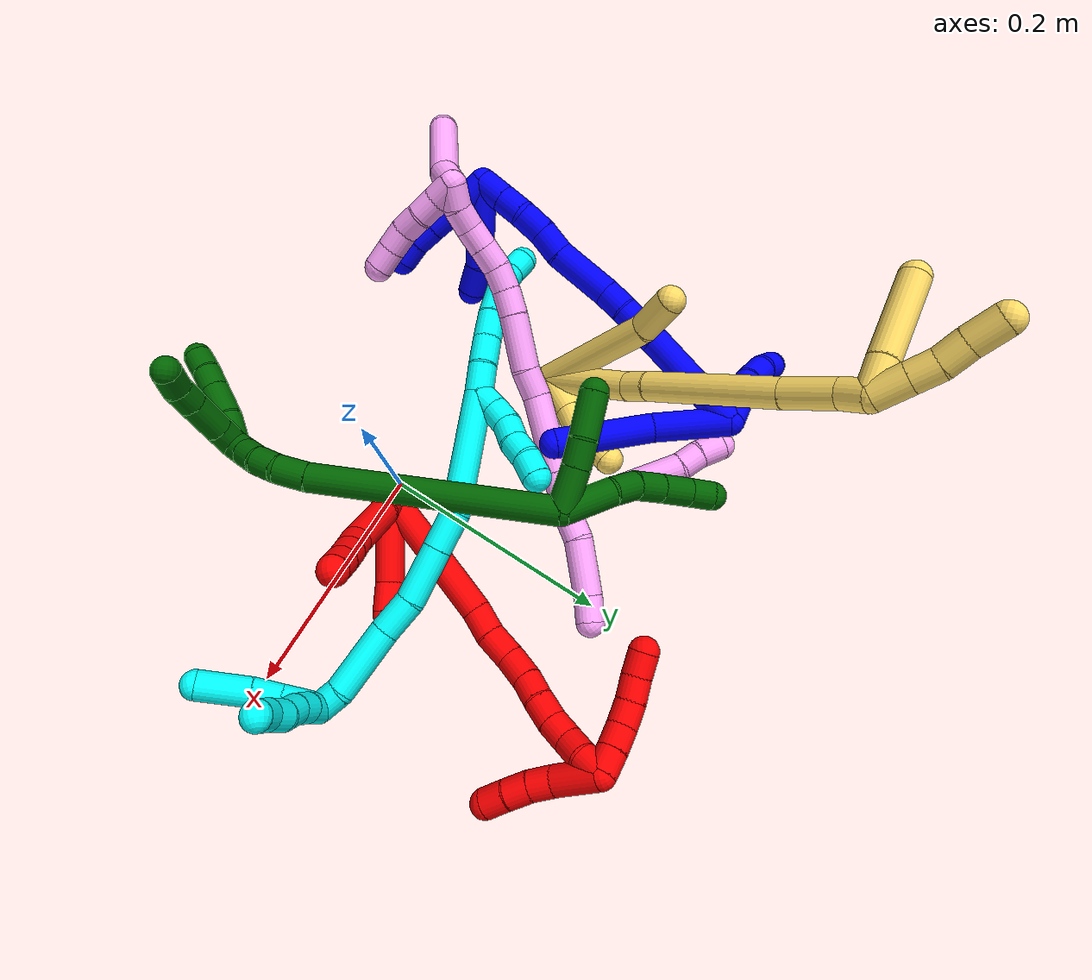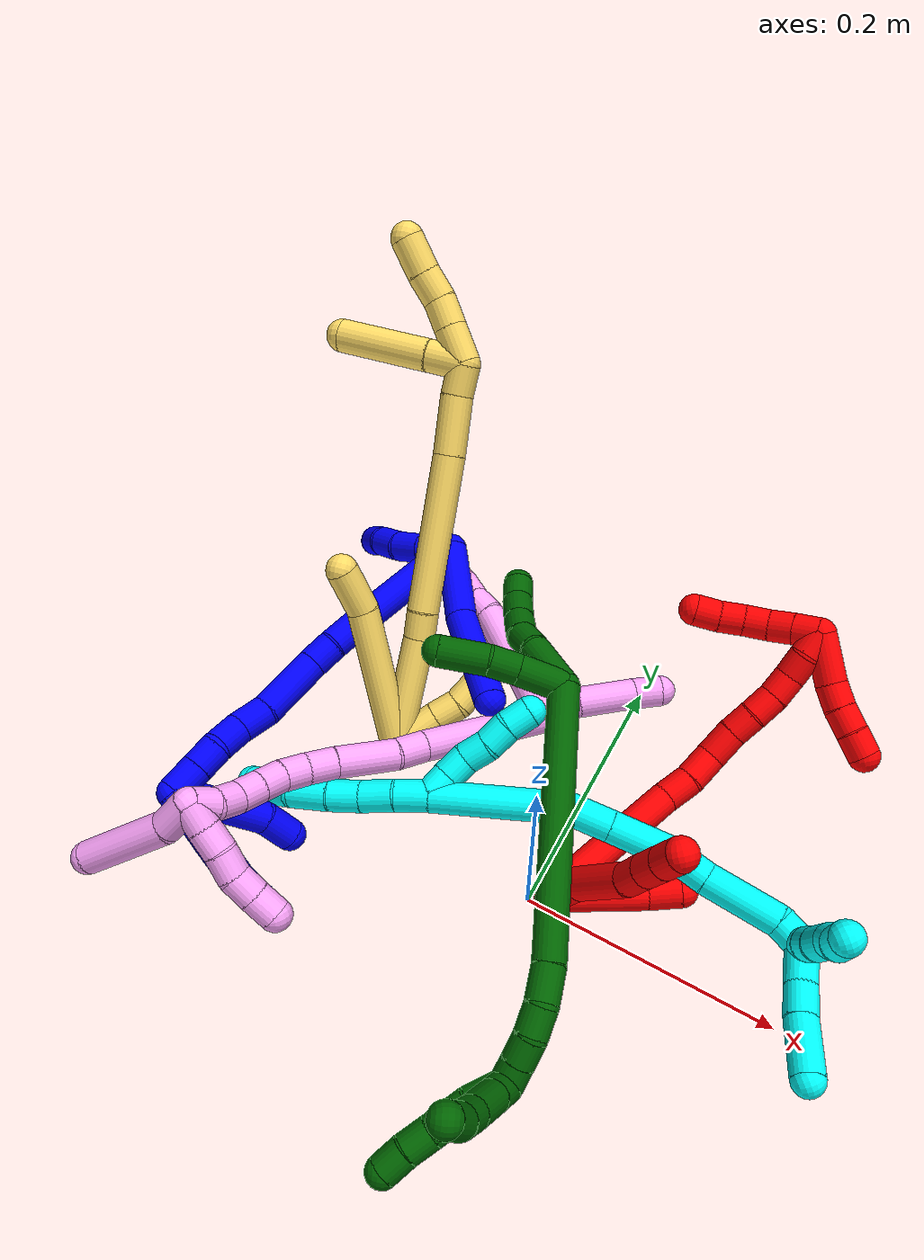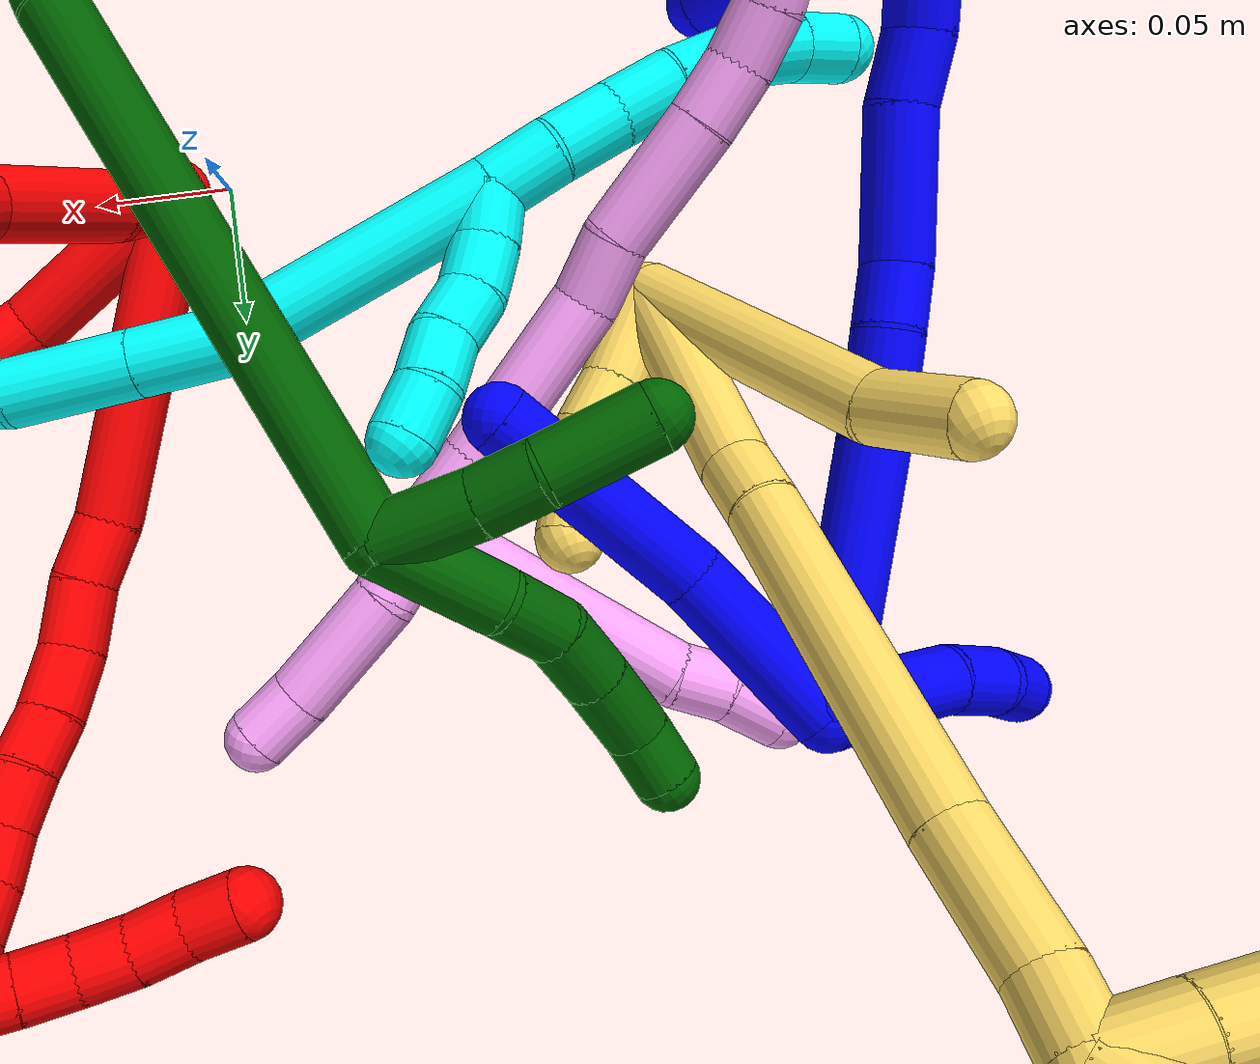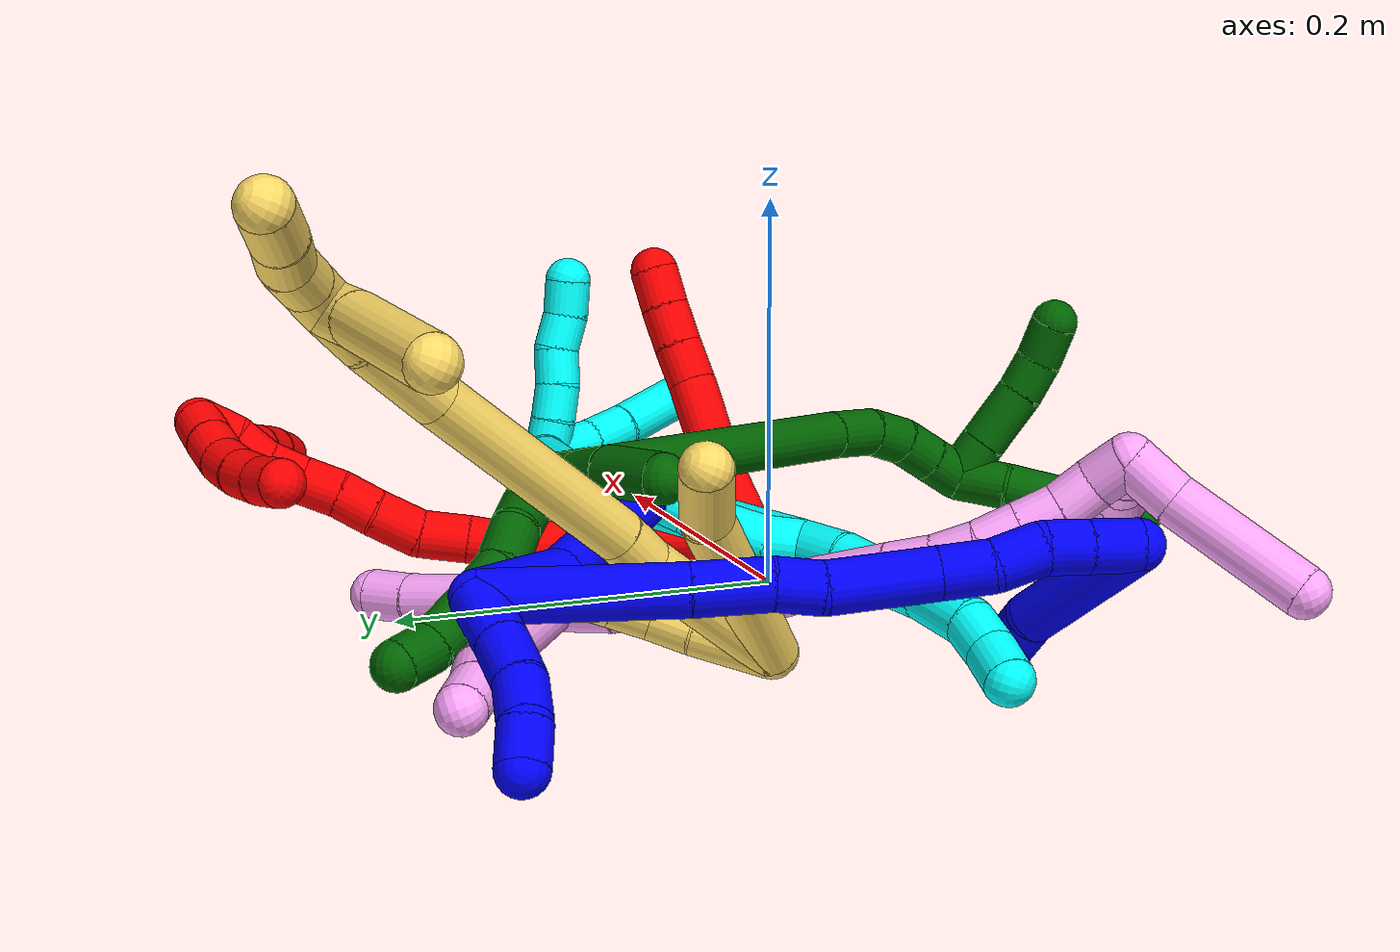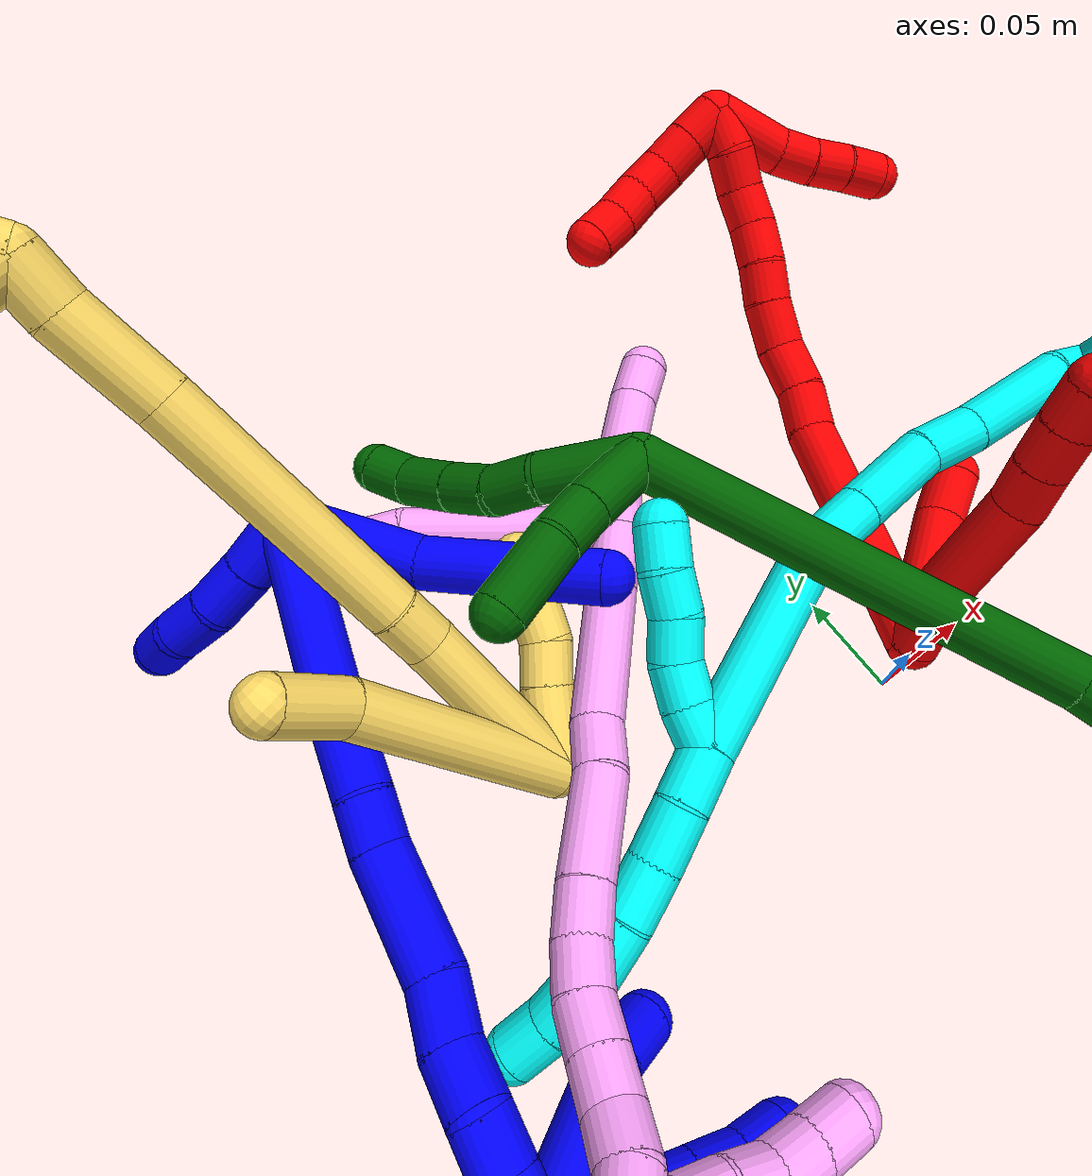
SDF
<sdf version="1.7">
 <world name="default">
  <plugin name="TubeGeneratorPlugin" filename="libtube_generator_plugin.so"/>
  <model name="photoneo_s_sensor">
   <static>1</static>
   <pose>0 0 2 1.57079 1.57079 3.14159</pose>
   <link name="link">
    <inertial><mass>0.1</mass></inertial>
    <sensor name="sensor" type="depth">
     <update_rate>30</update_rate>
     <camera>
      <horizontal_fov>1.22</horizontal_fov>
      <image><width>1920</width><height>1200</height><format>B8G8R8</format></image>
      <clip><near>0.1</near><far>4</far></clip>
      <depth_camera><output>points</output></depth_camera>
     </camera>
     <plugin name="camera_plugin" filename="libgazebo_ros_depth_camera.so">
      <baseline>0.2</baseline>
      <alwaysOn>1</alwaysOn>
      <updateRate>0.0</updateRate>
      <cameraName>camera_ir</cameraName>
      <imageTopicName>/camera/color/image_raw</imageTopicName>
      <cameraInfoTopicName>/camera/color/camera_info</cameraInfoTopicName>
      <depthImageTopicName>/camera/depth/image_raw</depthImageTopicName>
      <depthImageCameraInfoTopicName>/camera/depth/camera_info</depthImageCameraInfoTopicName>
      <pointCloudTopicName>/camera/depth/points</pointCloudTopicName>
      <frameName>fr_optical</frameName>
      <pointCloudCutoff>0.1</pointCloudCutoff>
      <pointCloudCutoffMax>2.0</pointCloudCutoffMax>
      <distortionK1>0</distortionK1>
      <distortionK2>0</distortionK2>
      <distortionK3>0</distortionK3>
      <distortionT1>0</distortionT1>
      <distortionT2>0</distortionT2>
      <CxPrime>0</CxPrime>
      <Cx>0</Cx>
      <Cy>0</Cy>
      <focalLength>0</focalLength>
      <hackBaseline>0</hackBaseline>
     </plugin>
    </sensor>
   </link>
  </model>
  <gravity>0 0 -9.8</gravity>
  <magnetic_field>6e-06 2.3e-05 -4.2e-05</magnetic_field>
  <atmosphere type="adiabatic"/>
  <physics name="default_physics" default="0" type="ode">
   <max_step_size>0.003</max_step_size>
   <real_time_factor>1</real_time_factor>
   <real_time_update_rate>1000</real_time_update_rate>
   <max_contacts>10000</max_contacts>
   <ode>
    <solver>
     <type>quick</type>
     <iters>100</iters>
     <sor>1.3</sor>
     <use_dynamic_moi_rescaling>0</use_dynamic_moi_rescaling>
    </solver>
    <constraints>
     <contact_max_correcting_vel>0</contact_max_correcting_vel>
     <contact_surface_layer>0.001</contact_surface_layer>
     <cfm>0</cfm>
     <erp>0.2</erp>
    </constraints>
   </ode>
  </physics>
  <scene><ambient>0.4 0.4 0.4 1</ambient><background>0.7 0.7 0.7 1</background><shadows>0</shadows></scene>
  <audio><device>default</device></audio>
  <spherical_coordinates>
   <surface_model>EARTH_WGS84</surface_model>
   <latitude_deg>0</latitude_deg>
   <longitude_deg>0</longitude_deg>
   <elevation>0</elevation>
   <heading_deg>0</heading_deg>
  </spherical_coordinates>
  <model name="bin">
   <static>1</static>
   <link name="bottom">
    <collision name="collision-bottom">
     <pose>0 0 -0.01 0 -0 0</pose>
     <geometry><box><size>0.8 0.6 0.02</size></box></geometry>
     <surface>
      <friction><ode><mu>100</mu><mu2>100</mu2></ode></friction>
      <contact><collide_bitmask>65535</collide_bitmask></contact>
     </surface>
    </collision>
   </link>
   <link name="west_wall">
    <collision name="collision-west_wall">
     <pose>-0.41 0 0.1 0 -0 0</pose>
     <geometry><box><size>0.02 0.6 0.2</size></box></geometry>
     <surface>
      <friction><ode><mu>100</mu><mu2>100</mu2></ode></friction>
      <contact><collide_bitmask>65535</collide_bitmask></contact>
     </surface>
    </collision>
   </link>
   <link name="east_wall">
    <collision name="collision-east_wall">
     <pose>0.41 0 0.1 0 -0 0</pose>
     <geometry><box><size>0.02 0.6 0.2</size></box></geometry>
     <surface>
      <friction><ode><mu>100</mu><mu2>100</mu2></ode></friction>
      <contact><collide_bitmask>65535</collide_bitmask></contact>
     </surface>
    </collision>
   </link>
   <link name="south_wall">
    <collision name="collision-south_wall">
     <pose>0 -0.31 0.1 0 -0 0</pose>
     <geometry><box><size>0.8 0.02 0.2</size></box></geometry>
     <surface>
      <friction><ode><mu>100</mu><mu2>100</mu2></ode></friction>
      <contact><collide_bitmask>65535</collide_bitmask></contact>
     </surface>
    </collision>
   </link>
   <link name="north_wall">
    <collision name="collision-north_wall">
     <pose>0 0.31 0.1 0 -0 0</pose>
     <geometry><box><size>0.8 0.02 0.2</size></box></geometry>
     <surface>
      <friction><ode><mu>100</mu><mu2>100</mu2></ode></friction>
      <contact><collide_bitmask>65535</collide_bitmask></contact>
     </surface>
    </collision>
   </link>
  </model>
  <model name="1">
   <static>0</static>
   <link name="1">
    <collision name="collision-cylinder-e_1_2_8">
     <pose>0.005035 -0.020529 -0.024422 2.44259 0.156525 0.423883</pose>
     <geometry><cylinder><radius>0.0125</radius><length>0.064598</length></cylinder></geometry>
     <surface>
      <friction><ode><mu>1.16</mu><mu2>1.16</mu2><slip1>0</slip1><slip2>0</slip2></ode></friction>
      <contact><ode><kp>1e+06</kp><kd>1</kd><max_vel>0</max_vel><min_depth>0.001</min_depth></ode></contact>
     </surface>
    </collision>
    <visual name="visual-cylinder-e_1_2_8">
     <pose>0.005035 -0.020529 -0.024422 2.44259 0.156525 0.423883</pose>
     <geometry><cylinder><radius>0.0125</radius><length>0.064598</length></cylinder></geometry>
     <material><ambient>0 0 1 1</ambient></material>
    </visual>
    <collision name="collision-cylinder-e_2_8_6">
     <pose>0.027833 -0.065414 -0.079087 2.46358 0.429019 1.10686</pose>
     <geometry><cylinder><radius>0.0125</radius><length>0.085402</length></cylinder></geometry>
     <surface>
      <friction><ode><mu>1.16</mu><mu2>1.16</mu2><slip1>0</slip1><slip2>0</slip2></ode></friction>
      <contact><ode><kp>1e+06</kp><kd>1</kd><max_vel>0</max_vel><min_depth>0.001</min_depth></ode></contact>
     </surface>
    </collision>
    <visual name="visual-cylinder-e_2_8_6">
     <pose>0.027833 -0.065414 -0.079087 2.46358 0.429019 1.10686</pose>
     <geometry><cylinder><radius>0.0125</radius><length>0.085402</length></cylinder></geometry>
     <material><ambient>0 0 1 1</ambient></material>
    </visual>
    <collision name="collision-cylinder-e_1_2_9">
     <pose>-0.012201 -0.002697 0.007627 0.33988 -0.98532 -0.183709</pose>
     <geometry><cylinder><radius>0.0125</radius><length>0.029278</length></cylinder></geometry>
     <surface>
      <friction><ode><mu>1.16</mu><mu2>1.16</mu2><slip1>0</slip1><slip2>0</slip2></ode></friction>
      <contact><ode><kp>1e+06</kp><kd>1</kd><max_vel>0</max_vel><min_depth>0.001</min_depth></ode></contact>
     </surface>
    </collision>
    <visual name="visual-cylinder-e_1_2_9">
     <pose>-0.012201 -0.002697 0.007627 0.33988 -0.98532 -0.183709</pose>
     <geometry><cylinder><radius>0.0125</radius><length>0.029278</length></cylinder></geometry>
     <material><ambient>0 0 1 1</ambient></material>
    </visual>
    <collision name="collision-cylinder-e_2_9_10">
     <pose>-0.034815 -0.00705 0.022614 0.221309 -0.943823 -0.113292</pose>
     <geometry><cylinder><radius>0.0125</radius><length>0.025718</length></cylinder></geometry>
     <surface>
      <friction><ode><mu>1.16</mu><mu2>1.16</mu2><slip1>0</slip1><slip2>0</slip2></ode></friction>
      <contact><ode><kp>1e+06</kp><kd>1</kd><max_vel>0</max_vel><min_depth>0.001</min_depth></ode></contact>
     </surface>
    </collision>
    <visual name="visual-cylinder-e_2_9_10">
     <pose>-0.034815 -0.00705 0.022614 0.221309 -0.943823 -0.113292</pose>
     <geometry><cylinder><radius>0.0125</radius><length>0.025718</length></cylinder></geometry>
     <material><ambient>0 0 1 1</ambient></material>
    </visual>
    <collision name="collision-cylinder-e_3_10_11">
     <pose>-0.055125 -0.007446 0.036558 -0.189076 -0.975412 0.10051</pose>
     <geometry><cylinder><radius>0.0125</radius><length>0.023905</length></cylinder></geometry>
     <surface>
      <friction><ode><mu>1.16</mu><mu2>1.16</mu2><slip1>0</slip1><slip2>0</slip2></ode></friction>
      <contact><ode><kp>1e+06</kp><kd>1</kd><max_vel>0</max_vel><min_depth>0.001</min_depth></ode></contact>
     </surface>
    </collision>
    <visual name="visual-cylinder-e_3_10_11">
     <pose>-0.055125 -0.007446 0.036558 -0.189076 -0.975412 0.10051</pose>
     <geometry><cylinder><radius>0.0125</radius><length>0.023905</length></cylinder></geometry>
     <material><ambient>0 0 1 1</ambient></material>
    </visual>
    <collision name="collision-cylinder-e_4_11_5">
     <pose>-0.074678 -0.003246 0.046203 -0.765155 -1.15675 0.513807</pose>
     <geometry><cylinder><radius>0.0125</radius><length>0.021098</length></cylinder></geometry>
     <surface>
      <friction><ode><mu>1.16</mu><mu2>1.16</mu2><slip1>0</slip1><slip2>0</slip2></ode></friction>
      <contact><ode><kp>1e+06</kp><kd>1</kd><max_vel>0</max_vel><min_depth>0.001</min_depth></ode></contact>
     </surface>
    </collision>
    <visual name="visual-cylinder-e_4_11_5">
     <pose>-0.074678 -0.003246 0.046203 -0.765155 -1.15675 0.513807</pose>
     <geometry><cylinder><radius>0.0125</radius><length>0.021098</length></cylinder></geometry>
     <material><ambient>0 0 1 1</ambient></material>
    </visual>
    <collision name="collision-cylinder-e_1_2_12">
     <pose>-0.009129 -0.045797 -0.000231 1.57585 -0.196749 -0.197738</pose>
     <geometry><cylinder><radius>0.0125</radius><length>0.093396</length></cylinder></geometry>
     <surface>
      <friction><ode><mu>1.16</mu><mu2>1.16</mu2><slip1>0</slip1><slip2>0</slip2></ode></friction>
      <contact><ode><kp>1e+06</kp><kd>1</kd><max_vel>0</max_vel><min_depth>0.001</min_depth></ode></contact>
     </surface>
    </collision>
    <visual name="visual-cylinder-e_1_2_12">
     <pose>-0.009129 -0.045797 -0.000231 1.57585 -0.196749 -0.197738</pose>
     <geometry><cylinder><radius>0.0125</radius><length>0.093396</length></cylinder></geometry>
     <material><ambient>0 0 1 1</ambient></material>
    </visual>
    <collision name="collision-cylinder-e_2_12_13">
     <pose>-0.021076 -0.109925 -0.001091 1.60505 -0.152502 -0.157796</pose>
     <geometry><cylinder><radius>0.0125</radius><length>0.037116</length></cylinder></geometry>
     <surface>
      <friction><ode><mu>1.16</mu><mu2>1.16</mu2><slip1>0</slip1><slip2>0</slip2></ode></friction>
      <contact><ode><kp>1e+06</kp><kd>1</kd><max_vel>0</max_vel><min_depth>0.001</min_depth></ode></contact>
     </surface>
    </collision>
    <visual name="visual-cylinder-e_2_12_13">
     <pose>-0.021076 -0.109925 -0.001091 1.60505 -0.152502 -0.157796</pose>
     <geometry><cylinder><radius>0.0125</radius><length>0.037116</length></cylinder></geometry>
     <material><ambient>0 0 1 1</ambient></material>
    </visual>
    <collision name="collision-cylinder-e_3_13_14">
     <pose>-0.027256 -0.138854 -0.002511 1.64544 -0.306241 -0.329585</pose>
     <geometry><cylinder><radius>0.0125</radius><length>0.022291</length></cylinder></geometry>
     <surface>
      <friction><ode><mu>1.16</mu><mu2>1.16</mu2><slip1>0</slip1><slip2>0</slip2></ode></friction>
      <contact><ode><kp>1e+06</kp><kd>1</kd><max_vel>0</max_vel><min_depth>0.001</min_depth></ode></contact>
     </surface>
    </collision>
    <visual name="visual-cylinder-e_3_13_14">
     <pose>-0.027256 -0.138854 -0.002511 1.64544 -0.306241 -0.329585</pose>
     <geometry><cylinder><radius>0.0125</radius><length>0.022291</length></cylinder></geometry>
     <material><ambient>0 0 1 1</ambient></material>
    </visual>
    <collision name="collision-cylinder-e_4_14_15">
     <pose>-0.032706 -0.17571 -0.006518 1.69259 -0.078862 -0.08909</pose>
     <geometry><cylinder><radius>0.0125</radius><length>0.053074</length></cylinder></geometry>
     <surface>
      <friction><ode><mu>1.16</mu><mu2>1.16</mu2><slip1>0</slip1><slip2>0</slip2></ode></friction>
      <contact><ode><kp>1e+06</kp><kd>1</kd><max_vel>0</max_vel><min_depth>0.001</min_depth></ode></contact>
     </surface>
    </collision>
    <visual name="visual-cylinder-e_4_14_15">
     <pose>-0.032706 -0.17571 -0.006518 1.69259 -0.078862 -0.08909</pose>
     <geometry><cylinder><radius>0.0125</radius><length>0.053074</length></cylinder></geometry>
     <material><ambient>0 0 1 1</ambient></material>
    </visual>
    <collision name="collision-cylinder-e_5_15_16">
     <pose>-0.036213 -0.214336 -0.008657 1.48412 -0.113587 -0.104163</pose>
     <geometry><cylinder><radius>0.0125</radius><length>0.024988</length></cylinder></geometry>
     <surface>
      <friction><ode><mu>1.16</mu><mu2>1.16</mu2><slip1>0</slip1><slip2>0</slip2></ode></friction>
      <contact><ode><kp>1e+06</kp><kd>1</kd><max_vel>0</max_vel><min_depth>0.001</min_depth></ode></contact>
     </surface>
    </collision>
    <visual name="visual-cylinder-e_5_15_16">
     <pose>-0.036213 -0.214336 -0.008657 1.48412 -0.113587 -0.104163</pose>
     <geometry><cylinder><radius>0.0125</radius><length>0.024988</length></cylinder></geometry>
     <material><ambient>0 0 1 1</ambient></material>
    </visual>
    <collision name="collision-cylinder-e_6_16_17">
     <pose>-0.036055 -0.238555 -0.00808 1.61277 0.131967 0.137609</pose>
     <geometry><cylinder><radius>0.0125</radius><length>0.023934</length></cylinder></geometry>
     <surface>
      <friction><ode><mu>1.16</mu><mu2>1.16</mu2><slip1>0</slip1><slip2>0</slip2></ode></friction>
      <contact><ode><kp>1e+06</kp><kd>1</kd><max_vel>0</max_vel><min_depth>0.001</min_depth></ode></contact>
     </surface>
    </collision>
    <visual name="visual-cylinder-e_6_16_17">
     <pose>-0.036055 -0.238555 -0.00808 1.61277 0.131967 0.137609</pose>
     <geometry><cylinder><radius>0.0125</radius><length>0.023934</length></cylinder></geometry>
     <material><ambient>0 0 1 1</ambient></material>
    </visual>
    <collision name="collision-cylinder-e_7_17_18">
     <pose>-0.036296 -0.260661 -0.010107 1.71884 -0.173457 -0.201069</pose>
     <geometry><cylinder><radius>0.0125</radius><length>0.021049</length></cylinder></geometry>
     <surface>
      <friction><ode><mu>1.16</mu><mu2>1.16</mu2><slip1>0</slip1><slip2>0</slip2></ode></friction>
      <contact><ode><kp>1e+06</kp><kd>1</kd><max_vel>0</max_vel><min_depth>0.001</min_depth></ode></contact>
     </surface>
    </collision>
    <visual name="visual-cylinder-e_7_17_18">
     <pose>-0.036296 -0.260661 -0.010107 1.71884 -0.173457 -0.201069</pose>
     <geometry><cylinder><radius>0.0125</radius><length>0.021049</length></cylinder></geometry>
     <material><ambient>0 0 1 1</ambient></material>
    </visual>
    <collision name="collision-cylinder-e_8_18_1">
     <pose>-0.040218 -0.282679 -0.013361 1.71638 -0.175263 -0.202658</pose>
     <geometry><cylinder><radius>0.0125</radius><length>0.024151</length></cylinder></geometry>
     <surface>
      <friction><ode><mu>1.16</mu><mu2>1.16</mu2><slip1>0</slip1><slip2>0</slip2></ode></friction>
      <contact><ode><kp>1e+06</kp><kd>1</kd><max_vel>0</max_vel><min_depth>0.001</min_depth></ode></contact>
     </surface>
    </collision>
    <visual name="visual-cylinder-e_8_18_1">
     <pose>-0.040218 -0.282679 -0.013361 1.71638 -0.175263 -0.202658</pose>
     <geometry><cylinder><radius>0.0125</radius><length>0.024151</length></cylinder></geometry>
     <material><ambient>0 0 1 1</ambient></material>
    </visual>
    <collision name="collision-cylinder-e_1_1_19">
     <pose>-0.041793 -0.294615 -0.02507 3.12449 0.053098 2.5184</pose>
     <geometry><cylinder><radius>0.0125</radius><length>0.02</length></cylinder></geometry>
     <surface>
      <friction><ode><mu>1.16</mu><mu2>1.16</mu2><slip1>0</slip1><slip2>0</slip2></ode></friction>
      <contact><ode><kp>1e+06</kp><kd>1</kd><max_vel>0</max_vel><min_depth>0.001</min_depth></ode></contact>
     </surface>
    </collision>
    <visual name="visual-cylinder-e_1_1_19">
     <pose>-0.041793 -0.294615 -0.02507 3.12449 0.053098 2.5184</pose>
     <geometry><cylinder><radius>0.0125</radius><length>0.02</length></cylinder></geometry>
     <material><ambient>0 0 1 1</ambient></material>
    </visual>
    <collision name="collision-cylinder-e_2_19_20">
     <pose>-0.040083 -0.296115 -0.044896 3.00735 0.118241 1.44386</pose>
     <geometry><cylinder><radius>0.0125</radius><length>0.02</length></cylinder></geometry>
     <surface>
      <friction><ode><mu>1.16</mu><mu2>1.16</mu2><slip1>0</slip1><slip2>0</slip2></ode></friction>
      <contact><ode><kp>1e+06</kp><kd>1</kd><max_vel>0</max_vel><min_depth>0.001</min_depth></ode></contact>
     </surface>
    </collision>
    <visual name="visual-cylinder-e_2_19_20">
     <pose>-0.040083 -0.296115 -0.044896 3.00735 0.118241 1.44386</pose>
     <geometry><cylinder><radius>0.0125</radius><length>0.02</length></cylinder></geometry>
     <material><ambient>0 0 1 1</ambient></material>
    </visual>
    <collision name="collision-cylinder-e_3_20_21">
     <pose>-0.037855 -0.298445 -0.064631 3.04079 0.105003 1.61165</pose>
     <geometry><cylinder><radius>0.0125</radius><length>0.02</length></cylinder></geometry>
     <surface>
      <friction><ode><mu>1.16</mu><mu2>1.16</mu2><slip1>0</slip1><slip2>0</slip2></ode></friction>
      <contact><ode><kp>1e+06</kp><kd>1</kd><max_vel>0</max_vel><min_depth>0.001</min_depth></ode></contact>
     </surface>
    </collision>
    <visual name="visual-cylinder-e_3_20_21">
     <pose>-0.037855 -0.298445 -0.064631 3.04079 0.105003 1.61165</pose>
     <geometry><cylinder><radius>0.0125</radius><length>0.02</length></cylinder></geometry>
     <material><ambient>0 0 1 1</ambient></material>
    </visual>
    <collision name="collision-cylinder-e_4_21_22">
     <pose>-0.035694 -0.300362 -0.084421 3.04923 0.111543 1.7587</pose>
     <geometry><cylinder><radius>0.0125</radius><length>0.02</length></cylinder></geometry>
     <surface>
      <friction><ode><mu>1.16</mu><mu2>1.16</mu2><slip1>0</slip1><slip2>0</slip2></ode></friction>
      <contact><ode><kp>1e+06</kp><kd>1</kd><max_vel>0</max_vel><min_depth>0.001</min_depth></ode></contact>
     </surface>
    </collision>
    <visual name="visual-cylinder-e_4_21_22">
     <pose>-0.035694 -0.300362 -0.084421 3.04923 0.111543 1.7587</pose>
     <geometry><cylinder><radius>0.0125</radius><length>0.02</length></cylinder></geometry>
     <material><ambient>0 0 1 1</ambient></material>
    </visual>
    <collision name="collision-cylinder-e_5_22_4">
     <pose>-0.034421 -0.300194 -0.104256 -3.03291 0.016013 -0.292292</pose>
     <geometry><cylinder><radius>0.0125</radius><length>0.02</length></cylinder></geometry>
     <surface>
      <friction><ode><mu>1.16</mu><mu2>1.16</mu2><slip1>0</slip1><slip2>0</slip2></ode></friction>
      <contact><ode><kp>1e+06</kp><kd>1</kd><max_vel>0</max_vel><min_depth>0.001</min_depth></ode></contact>
     </surface>
    </collision>
    <visual name="visual-cylinder-e_5_22_4">
     <pose>-0.034421 -0.300194 -0.104256 -3.03291 0.016013 -0.292292</pose>
     <geometry><cylinder><radius>0.0125</radius><length>0.02</length></cylinder></geometry>
     <material><ambient>0 0 1 1</ambient></material>
    </visual>
    <collision name="collision-cylinder-e_1_1_23">
     <pose>-0.048942 -0.271916 -0.043611 -2.47312 -0.180096 0.508752</pose>
     <geometry><cylinder><radius>0.0125</radius><length>0.073891</length></cylinder></geometry>
     <surface>
      <friction><ode><mu>1.16</mu><mu2>1.16</mu2><slip1>0</slip1><slip2>0</slip2></ode></friction>
      <contact><ode><kp>1e+06</kp><kd>1</kd><max_vel>0</max_vel><min_depth>0.001</min_depth></ode></contact>
     </surface>
    </collision>
    <visual name="visual-cylinder-e_1_1_23">
     <pose>-0.048942 -0.271916 -0.043611 -2.47312 -0.180096 0.508752</pose>
     <geometry><cylinder><radius>0.0125</radius><length>0.073891</length></cylinder></geometry>
     <material><ambient>0 0 1 1</ambient></material>
    </visual>
    <collision name="collision-cylinder-e_2_23_3">
     <pose>-0.059405 -0.244515 -0.08362 -2.74032 -0.299033 1.27505</pose>
     <geometry><cylinder><radius>0.0125</radius><length>0.026109</length></cylinder></geometry>
     <surface>
      <friction><ode><mu>1.16</mu><mu2>1.16</mu2><slip1>0</slip1><slip2>0</slip2></ode></friction>
      <contact><ode><kp>1e+06</kp><kd>1</kd><max_vel>0</max_vel><min_depth>0.001</min_depth></ode></contact>
     </surface>
    </collision>
    <visual name="visual-cylinder-e_2_23_3">
     <pose>-0.059405 -0.244515 -0.08362 -2.74032 -0.299033 1.27505</pose>
     <geometry><cylinder><radius>0.0125</radius><length>0.026109</length></cylinder></geometry>
     <material><ambient>0 0 1 1</ambient></material>
    </visual>
    <collision name="collision-sphere-3">
     <pose>-0.063251 -0.239642 -0.095104 0 -0 0</pose>
     <geometry><sphere><radius>0.0125</radius></sphere></geometry>
     <surface>
      <friction><ode><mu>1.16</mu><mu2>1.16</mu2><slip1>0</slip1><slip2>0</slip2></ode></friction>
      <contact><ode><kp>1e+06</kp><kd>1</kd><max_vel>0</max_vel><min_depth>0.001</min_depth></ode></contact>
     </surface>
    </collision>
    <visual name="visual-sphere-3">
     <pose>-0.063251 -0.239642 -0.095104 0 -0 0</pose>
     <geometry><sphere><radius>0.0125</radius></sphere></geometry>
     <material><ambient>0 0 1 1</ambient></material>
    </visual>
    <collision name="collision-sphere-23">
     <pose>-0.05556 -0.249388 -0.072135 0 -0 0</pose>
     <geometry><sphere><radius>0.0125</radius></sphere></geometry>
     <surface>
      <friction><ode><mu>1.16</mu><mu2>1.16</mu2><slip1>0</slip1><slip2>0</slip2></ode></friction>
      <contact><ode><kp>1e+06</kp><kd>1</kd><max_vel>0</max_vel><min_depth>0.001</min_depth></ode></contact>
     </surface>
    </collision>
    <visual name="visual-sphere-23">
     <pose>-0.05556 -0.249388 -0.072135 0 -0 0</pose>
     <geometry><sphere><radius>0.0125</radius></sphere></geometry>
     <material><ambient>0 0 1 1</ambient></material>
    </visual>
    <collision name="collision-sphere-4">
     <pose>-0.034261 -0.29911 -0.114196 0 -0 0</pose>
     <geometry><sphere><radius>0.0125</radius></sphere></geometry>
     <surface>
      <friction><ode><mu>1.16</mu><mu2>1.16</mu2><slip1>0</slip1><slip2>0</slip2></ode></friction>
      <contact><ode><kp>1e+06</kp><kd>1</kd><max_vel>0</max_vel><min_depth>0.001</min_depth></ode></contact>
     </surface>
    </collision>
    <visual name="visual-sphere-4">
     <pose>-0.034261 -0.29911 -0.114196 0 -0 0</pose>
     <geometry><sphere><radius>0.0125</radius></sphere></geometry>
     <material><ambient>0 0 1 1</ambient></material>
    </visual>
    <collision name="collision-sphere-22">
     <pose>-0.034581 -0.301279 -0.094316 0 -0 0</pose>
     <geometry><sphere><radius>0.0125</radius></sphere></geometry>
     <surface>
      <friction><ode><mu>1.16</mu><mu2>1.16</mu2><slip1>0</slip1><slip2>0</slip2></ode></friction>
      <contact><ode><kp>1e+06</kp><kd>1</kd><max_vel>0</max_vel><min_depth>0.001</min_depth></ode></contact>
     </surface>
    </collision>
    <visual name="visual-sphere-22">
     <pose>-0.034581 -0.301279 -0.094316 0 -0 0</pose>
     <geometry><sphere><radius>0.0125</radius></sphere></geometry>
     <material><ambient>0 0 1 1</ambient></material>
    </visual>
    <collision name="collision-sphere-21">
     <pose>-0.036807 -0.299445 -0.074525 0 -0 0</pose>
     <geometry><sphere><radius>0.0125</radius></sphere></geometry>
     <surface>
      <friction><ode><mu>1.16</mu><mu2>1.16</mu2><slip1>0</slip1><slip2>0</slip2></ode></friction>
      <contact><ode><kp>1e+06</kp><kd>1</kd><max_vel>0</max_vel><min_depth>0.001</min_depth></ode></contact>
     </surface>
    </collision>
    <visual name="visual-sphere-21">
     <pose>-0.036807 -0.299445 -0.074525 0 -0 0</pose>
     <geometry><sphere><radius>0.0125</radius></sphere></geometry>
     <material><ambient>0 0 1 1</ambient></material>
    </visual>
    <collision name="collision-sphere-20">
     <pose>-0.038903 -0.297444 -0.054737 0 -0 0</pose>
     <geometry><sphere><radius>0.0125</radius></sphere></geometry>
     <surface>
      <friction><ode><mu>1.16</mu><mu2>1.16</mu2><slip1>0</slip1><slip2>0</slip2></ode></friction>
      <contact><ode><kp>1e+06</kp><kd>1</kd><max_vel>0</max_vel><min_depth>0.001</min_depth></ode></contact>
     </surface>
    </collision>
    <visual name="visual-sphere-20">
     <pose>-0.038903 -0.297444 -0.054737 0 -0 0</pose>
     <geometry><sphere><radius>0.0125</radius></sphere></geometry>
     <material><ambient>0 0 1 1</ambient></material>
    </visual>
    <collision name="collision-sphere-11">
     <pose>-0.065021 -0.006186 0.043142 0 -0 0</pose>
     <geometry><sphere><radius>0.0125</radius></sphere></geometry>
     <surface>
      <friction><ode><mu>1.16</mu><mu2>1.16</mu2><slip1>0</slip1><slip2>0</slip2></ode></friction>
      <contact><ode><kp>1e+06</kp><kd>1</kd><max_vel>0</max_vel><min_depth>0.001</min_depth></ode></contact>
     </surface>
    </collision>
    <visual name="visual-sphere-11">
     <pose>-0.065021 -0.006186 0.043142 0 -0 0</pose>
     <geometry><sphere><radius>0.0125</radius></sphere></geometry>
     <material><ambient>0 0 1 1</ambient></material>
    </visual>
    <collision name="collision-sphere-10">
     <pose>-0.045228 -0.008706 0.029974 0 -0 0</pose>
     <geometry><sphere><radius>0.0125</radius></sphere></geometry>
     <surface>
      <friction><ode><mu>1.16</mu><mu2>1.16</mu2><slip1>0</slip1><slip2>0</slip2></ode></friction>
      <contact><ode><kp>1e+06</kp><kd>1</kd><max_vel>0</max_vel><min_depth>0.001</min_depth></ode></contact>
     </surface>
    </collision>
    <visual name="visual-sphere-10">
     <pose>-0.045228 -0.008706 0.029974 0 -0 0</pose>
     <geometry><sphere><radius>0.0125</radius></sphere></geometry>
     <material><ambient>0 0 1 1</ambient></material>
    </visual>
    <collision name="collision-sphere-6">
     <pose>0.045595 -0.089771 -0.109329 0 -0 0</pose>
     <geometry><sphere><radius>0.0125</radius></sphere></geometry>
     <surface>
      <friction><ode><mu>1.16</mu><mu2>1.16</mu2><slip1>0</slip1><slip2>0</slip2></ode></friction>
      <contact><ode><kp>1e+06</kp><kd>1</kd><max_vel>0</max_vel><min_depth>0.001</min_depth></ode></contact>
     </surface>
    </collision>
    <visual name="visual-sphere-6">
     <pose>0.045595 -0.089771 -0.109329 0 -0 0</pose>
     <geometry><sphere><radius>0.0125</radius></sphere></geometry>
     <material><ambient>0 0 1 1</ambient></material>
    </visual>
    <collision name="collision-sphere-9">
     <pose>-0.024402 -0.005394 0.015254 0 -0 0</pose>
     <geometry><sphere><radius>0.0125</radius></sphere></geometry>
     <surface>
      <friction><ode><mu>1.16</mu><mu2>1.16</mu2><slip1>0</slip1><slip2>0</slip2></ode></friction>
      <contact><ode><kp>1e+06</kp><kd>1</kd><max_vel>0</max_vel><min_depth>0.001</min_depth></ode></contact>
     </surface>
    </collision>
    <visual name="visual-sphere-9">
     <pose>-0.024402 -0.005394 0.015254 0 -0 0</pose>
     <geometry><sphere><radius>0.0125</radius></sphere></geometry>
     <material><ambient>0 0 1 1</ambient></material>
    </visual>
    <collision name="collision-sphere-2">
     <geometry><sphere><radius>0.0125</radius></sphere></geometry>
     <surface>
      <friction><ode><mu>1.16</mu><mu2>1.16</mu2><slip1>0</slip1><slip2>0</slip2></ode></friction>
      <contact><ode><kp>1e+06</kp><kd>1</kd><max_vel>0</max_vel><min_depth>0.001</min_depth></ode></contact>
     </surface>
    </collision>
    <visual name="visual-sphere-2">
     <geometry><sphere><radius>0.0125</radius></sphere></geometry>
     <material><ambient>0 0 1 1</ambient></material>
    </visual>
    <collision name="collision-sphere-19">
     <pose>-0.041263 -0.294786 -0.035055 0 -0 0</pose>
     <geometry><sphere><radius>0.0125</radius></sphere></geometry>
     <surface>
      <friction><ode><mu>1.16</mu><mu2>1.16</mu2><slip1>0</slip1><slip2>0</slip2></ode></friction>
      <contact><ode><kp>1e+06</kp><kd>1</kd><max_vel>0</max_vel><min_depth>0.001</min_depth></ode></contact>
     </surface>
    </collision>
    <visual name="visual-sphere-19">
     <pose>-0.041263 -0.294786 -0.035055 0 -0 0</pose>
     <geometry><sphere><radius>0.0125</radius></sphere></geometry>
     <material><ambient>0 0 1 1</ambient></material>
    </visual>
    <collision name="collision-sphere-8">
     <pose>0.01007 -0.041058 -0.048844 0 -0 0</pose>
     <geometry><sphere><radius>0.0125</radius></sphere></geometry>
     <surface>
      <friction><ode><mu>1.16</mu><mu2>1.16</mu2><slip1>0</slip1><slip2>0</slip2></ode></friction>
      <contact><ode><kp>1e+06</kp><kd>1</kd><max_vel>0</max_vel><min_depth>0.001</min_depth></ode></contact>
     </surface>
    </collision>
    <visual name="visual-sphere-8">
     <pose>0.01007 -0.041058 -0.048844 0 -0 0</pose>
     <geometry><sphere><radius>0.0125</radius></sphere></geometry>
     <material><ambient>0 0 1 1</ambient></material>
    </visual>
    <collision name="collision-sphere-5">
     <pose>-0.084336 -0.000307 0.049264 0 -0 0</pose>
     <geometry><sphere><radius>0.0125</radius></sphere></geometry>
     <surface>
      <friction><ode><mu>1.16</mu><mu2>1.16</mu2><slip1>0</slip1><slip2>0</slip2></ode></friction>
      <contact><ode><kp>1e+06</kp><kd>1</kd><max_vel>0</max_vel><min_depth>0.001</min_depth></ode></contact>
     </surface>
    </collision>
    <visual name="visual-sphere-5">
     <pose>-0.084336 -0.000307 0.049264 0 -0 0</pose>
     <geometry><sphere><radius>0.0125</radius></sphere></geometry>
     <material><ambient>0 0 1 1</ambient></material>
    </visual>
    <collision name="collision-sphere-12">
     <pose>-0.018257 -0.091593 -0.000462 0 -0 0</pose>
     <geometry><sphere><radius>0.0125</radius></sphere></geometry>
     <surface>
      <friction><ode><mu>1.16</mu><mu2>1.16</mu2><slip1>0</slip1><slip2>0</slip2></ode></friction>
      <contact><ode><kp>1e+06</kp><kd>1</kd><max_vel>0</max_vel><min_depth>0.001</min_depth></ode></contact>
     </surface>
    </collision>
    <visual name="visual-sphere-12">
     <pose>-0.018257 -0.091593 -0.000462 0 -0 0</pose>
     <geometry><sphere><radius>0.0125</radius></sphere></geometry>
     <material><ambient>0 0 1 1</ambient></material>
    </visual>
    <collision name="collision-sphere-13">
     <pose>-0.023896 -0.128257 -0.001719 0 -0 0</pose>
     <geometry><sphere><radius>0.0125</radius></sphere></geometry>
     <surface>
      <friction><ode><mu>1.16</mu><mu2>1.16</mu2><slip1>0</slip1><slip2>0</slip2></ode></friction>
      <contact><ode><kp>1e+06</kp><kd>1</kd><max_vel>0</max_vel><min_depth>0.001</min_depth></ode></contact>
     </surface>
    </collision>
    <visual name="visual-sphere-13">
     <pose>-0.023896 -0.128257 -0.001719 0 -0 0</pose>
     <geometry><sphere><radius>0.0125</radius></sphere></geometry>
     <material><ambient>0 0 1 1</ambient></material>
    </visual>
    <collision name="collision-sphere-14">
     <pose>-0.030616 -0.149451 -0.003304 0 -0 0</pose>
     <geometry><sphere><radius>0.0125</radius></sphere></geometry>
     <surface>
      <friction><ode><mu>1.16</mu><mu2>1.16</mu2><slip1>0</slip1><slip2>0</slip2></ode></friction>
      <contact><ode><kp>1e+06</kp><kd>1</kd><max_vel>0</max_vel><min_depth>0.001</min_depth></ode></contact>
     </surface>
    </collision>
    <visual name="visual-sphere-14">
     <pose>-0.030616 -0.149451 -0.003304 0 -0 0</pose>
     <geometry><sphere><radius>0.0125</radius></sphere></geometry>
     <material><ambient>0 0 1 1</ambient></material>
    </visual>
    <collision name="collision-sphere-15">
     <pose>-0.034797 -0.201969 -0.009732 0 -0 0</pose>
     <geometry><sphere><radius>0.0125</radius></sphere></geometry>
     <surface>
      <friction><ode><mu>1.16</mu><mu2>1.16</mu2><slip1>0</slip1><slip2>0</slip2></ode></friction>
      <contact><ode><kp>1e+06</kp><kd>1</kd><max_vel>0</max_vel><min_depth>0.001</min_depth></ode></contact>
     </surface>
    </collision>
    <visual name="visual-sphere-15">
     <pose>-0.034797 -0.201969 -0.009732 0 -0 0</pose>
     <geometry><sphere><radius>0.0125</radius></sphere></geometry>
     <material><ambient>0 0 1 1</ambient></material>
    </visual>
    <collision name="collision-sphere-16">
     <pose>-0.037629 -0.226703 -0.007582 0 -0 0</pose>
     <geometry><sphere><radius>0.0125</radius></sphere></geometry>
     <surface>
      <friction><ode><mu>1.16</mu><mu2>1.16</mu2><slip1>0</slip1><slip2>0</slip2></ode></friction>
      <contact><ode><kp>1e+06</kp><kd>1</kd><max_vel>0</max_vel><min_depth>0.001</min_depth></ode></contact>
     </surface>
    </collision>
    <visual name="visual-sphere-16">
     <pose>-0.037629 -0.226703 -0.007582 0 -0 0</pose>
     <geometry><sphere><radius>0.0125</radius></sphere></geometry>
     <material><ambient>0 0 1 1</ambient></material>
    </visual>
    <collision name="collision-sphere-17">
     <pose>-0.03448 -0.250408 -0.008578 0 -0 0</pose>
     <geometry><sphere><radius>0.0125</radius></sphere></geometry>
     <surface>
      <friction><ode><mu>1.16</mu><mu2>1.16</mu2><slip1>0</slip1><slip2>0</slip2></ode></friction>
      <contact><ode><kp>1e+06</kp><kd>1</kd><max_vel>0</max_vel><min_depth>0.001</min_depth></ode></contact>
     </surface>
    </collision>
    <visual name="visual-sphere-17">
     <pose>-0.03448 -0.250408 -0.008578 0 -0 0</pose>
     <geometry><sphere><radius>0.0125</radius></sphere></geometry>
     <material><ambient>0 0 1 1</ambient></material>
    </visual>
    <collision name="collision-sphere-18">
     <pose>-0.038113 -0.270914 -0.011636 0 -0 0</pose>
     <geometry><sphere><radius>0.0125</radius></sphere></geometry>
     <surface>
      <friction><ode><mu>1.16</mu><mu2>1.16</mu2><slip1>0</slip1><slip2>0</slip2></ode></friction>
      <contact><ode><kp>1e+06</kp><kd>1</kd><max_vel>0</max_vel><min_depth>0.001</min_depth></ode></contact>
     </surface>
    </collision>
    <visual name="visual-sphere-18">
     <pose>-0.038113 -0.270914 -0.011636 0 -0 0</pose>
     <geometry><sphere><radius>0.0125</radius></sphere></geometry>
     <material><ambient>0 0 1 1</ambient></material>
    </visual>
    <collision name="collision-sphere-1">
     <pose>-0.042324 -0.294444 -0.015086 0 -0 0</pose>
     <geometry><sphere><radius>0.0125</radius></sphere></geometry>
     <surface>
      <friction><ode><mu>1.16</mu><mu2>1.16</mu2><slip1>0</slip1><slip2>0</slip2></ode></friction>
      <contact><ode><kp>1e+06</kp><kd>1</kd><max_vel>0</max_vel><min_depth>0.001</min_depth></ode></contact>
     </surface>
    </collision>
    <visual name="visual-sphere-1">
     <pose>-0.042324 -0.294444 -0.015086 0 -0 0</pose>
     <geometry><sphere><radius>0.0125</radius></sphere></geometry>
     <material><ambient>0 0 1 1</ambient></material>
    </visual>
    <inertial>
     <pose>-0.023853 -0.143797 -0.025278 0 -0 0</pose>
     <mass>0.75</mass>
     <inertia><ixx>0.000235</ixx><ixy>0</ixy><ixz>0</ixz><iyy>-0</iyy><iyz>0</iyz><izz>0.00011</izz></inertia>
    </inertial>
   </link>
   <pose>-0.186376 0.215515 0.063844 -0.40377 -1.0722 0.150823</pose>
  </model>
  <model name="2">
   <static>0</static>
   <link name="2">
    <collision name="collision-cylinder-e_1_2_8">
     <pose>0.015584 -0.003752 0.003926 0.762656 1.23549 0.555059</pose>
     <geometry><cylinder><radius>0.0125</radius><length>0.033007</length></cylinder></geometry>
     <surface>
      <friction><ode><mu>1.16</mu><mu2>1.16</mu2><slip1>0</slip1><slip2>0</slip2></ode></friction>
      <contact><ode><kp>1e+06</kp><kd>1</kd><max_vel>0</max_vel><min_depth>0.001</min_depth></ode></contact>
     </surface>
    </collision>
    <visual name="visual-cylinder-e_1_2_8">
     <pose>0.015584 -0.003752 0.003926 0.762656 1.23549 0.555059</pose>
     <geometry><cylinder><radius>0.0125</radius><length>0.033007</length></cylinder></geometry>
     <material><ambient>1 0 0 1</ambient></material>
    </visual>
    <collision name="collision-cylinder-e_2_8_9">
     <pose>0.056687 -0.015438 0.009037 1.42266 1.2662 1.12793</pose>
     <geometry><cylinder><radius>0.0125</radius><length>0.053498</length></cylinder></geometry>
     <surface>
      <friction><ode><mu>1.16</mu><mu2>1.16</mu2><slip1>0</slip1><slip2>0</slip2></ode></friction>
      <contact><ode><kp>1e+06</kp><kd>1</kd><max_vel>0</max_vel><min_depth>0.001</min_depth></ode></contact>
     </surface>
    </collision>
    <visual name="visual-cylinder-e_2_8_9">
     <pose>0.056687 -0.015438 0.009037 1.42266 1.2662 1.12793</pose>
     <geometry><cylinder><radius>0.0125</radius><length>0.053498</length></cylinder></geometry>
     <material><ambient>1 0 0 1</ambient></material>
    </visual>
    <collision name="collision-cylinder-e_3_9_10">
     <pose>0.092004 -0.026745 0.013142 0.85709 1.14353 0.571838</pose>
     <geometry><cylinder><radius>0.0125</radius><length>0.021535</length></cylinder></geometry>
     <surface>
      <friction><ode><mu>1.16</mu><mu2>1.16</mu2><slip1>0</slip1><slip2>0</slip2></ode></friction>
      <contact><ode><kp>1e+06</kp><kd>1</kd><max_vel>0</max_vel><min_depth>0.001</min_depth></ode></contact>
     </surface>
    </collision>
    <visual name="visual-cylinder-e_3_9_10">
     <pose>0.092004 -0.026745 0.013142 0.85709 1.14353 0.571838</pose>
     <geometry><cylinder><radius>0.0125</radius><length>0.021535</length></cylinder></geometry>
     <material><ambient>1 0 0 1</ambient></material>
    </visual>
    <collision name="collision-cylinder-e_4_10_11">
     <pose>0.111547 -0.033746 0.018742 0.934698 1.13727 0.623912</pose>
     <geometry><cylinder><radius>0.0125</radius><length>0.021474</length></cylinder></geometry>
     <surface>
      <friction><ode><mu>1.16</mu><mu2>1.16</mu2><slip1>0</slip1><slip2>0</slip2></ode></friction>
      <contact><ode><kp>1e+06</kp><kd>1</kd><max_vel>0</max_vel><min_depth>0.001</min_depth></ode></contact>
     </surface>
    </collision>
    <visual name="visual-cylinder-e_4_10_11">
     <pose>0.111547 -0.033746 0.018742 0.934698 1.13727 0.623912</pose>
     <geometry><cylinder><radius>0.0125</radius><length>0.021474</length></cylinder></geometry>
     <material><ambient>1 0 0 1</ambient></material>
    </visual>
    <collision name="collision-cylinder-e_5_11_6">
     <pose>0.130441 -0.041231 0.023935 0.993327 1.10466 0.644755</pose>
     <geometry><cylinder><radius>0.0125</radius><length>0.020487</length></cylinder></geometry>
     <surface>
      <friction><ode><mu>1.16</mu><mu2>1.16</mu2><slip1>0</slip1><slip2>0</slip2></ode></friction>
      <contact><ode><kp>1e+06</kp><kd>1</kd><max_vel>0</max_vel><min_depth>0.001</min_depth></ode></contact>
     </surface>
    </collision>
    <visual name="visual-cylinder-e_5_11_6">
     <pose>0.130441 -0.041231 0.023935 0.993327 1.10466 0.644755</pose>
     <geometry><cylinder><radius>0.0125</radius><length>0.020487</length></cylinder></geometry>
     <material><ambient>1 0 0 1</ambient></material>
    </visual>
    <collision name="collision-cylinder-e_1_2_12">
     <pose>0.024536 0.026343 -0.008136 -1.87036 0.727218 -0.952405</pose>
     <geometry><cylinder><radius>0.0125</radius><length>0.073814</length></cylinder></geometry>
     <surface>
      <friction><ode><mu>1.16</mu><mu2>1.16</mu2><slip1>0</slip1><slip2>0</slip2></ode></friction>
      <contact><ode><kp>1e+06</kp><kd>1</kd><max_vel>0</max_vel><min_depth>0.001</min_depth></ode></contact>
     </surface>
    </collision>
    <visual name="visual-cylinder-e_1_2_12">
     <pose>0.024536 0.026343 -0.008136 -1.87036 0.727218 -0.952405</pose>
     <geometry><cylinder><radius>0.0125</radius><length>0.073814</length></cylinder></geometry>
     <material><ambient>1 0 0 1</ambient></material>
    </visual>
    <collision name="collision-cylinder-e_2_12_5">
     <pose>0.060218 0.059363 -0.017883 -1.80753 1.01854 -1.23367</pose>
     <geometry><cylinder><radius>0.0125</radius><length>0.026186</length></cylinder></geometry>
     <surface>
      <friction><ode><mu>1.16</mu><mu2>1.16</mu2><slip1>0</slip1><slip2>0</slip2></ode></friction>
      <contact><ode><kp>1e+06</kp><kd>1</kd><max_vel>0</max_vel><min_depth>0.001</min_depth></ode></contact>
     </surface>
    </collision>
    <visual name="visual-cylinder-e_2_12_5">
     <pose>0.060218 0.059363 -0.017883 -1.80753 1.01854 -1.23367</pose>
     <geometry><cylinder><radius>0.0125</radius><length>0.026186</length></cylinder></geometry>
     <material><ambient>1 0 0 1</ambient></material>
    </visual>
    <collision name="collision-cylinder-e_1_2_13">
     <pose>0.02856 0.048319 0.023989 -1.10997 0.486909 -0.305586</pose>
     <geometry><cylinder><radius>0.0125</radius><length>0.12208</length></cylinder></geometry>
     <surface>
      <friction><ode><mu>1.16</mu><mu2>1.16</mu2><slip1>0</slip1><slip2>0</slip2></ode></friction>
      <contact><ode><kp>1e+06</kp><kd>1</kd><max_vel>0</max_vel><min_depth>0.001</min_depth></ode></contact>
     </surface>
    </collision>
    <visual name="visual-cylinder-e_1_2_13">
     <pose>0.02856 0.048319 0.023989 -1.10997 0.486909 -0.305586</pose>
     <geometry><cylinder><radius>0.0125</radius><length>0.12208</length></cylinder></geometry>
     <material><ambient>1 0 0 1</ambient></material>
    </visual>
    <collision name="collision-cylinder-e_2_13_14">
     <pose>0.065179 0.104404 0.052659 -1.02835 0.726512 -0.423008</pose>
     <geometry><cylinder><radius>0.0125</radius><length>0.024262</length></cylinder></geometry>
     <surface>
      <friction><ode><mu>1.16</mu><mu2>1.16</mu2><slip1>0</slip1><slip2>0</slip2></ode></friction>
      <contact><ode><kp>1e+06</kp><kd>1</kd><max_vel>0</max_vel><min_depth>0.001</min_depth></ode></contact>
     </surface>
    </collision>
    <visual name="visual-cylinder-e_2_13_14">
     <pose>0.065179 0.104404 0.052659 -1.02835 0.726512 -0.423008</pose>
     <geometry><cylinder><radius>0.0125</radius><length>0.024262</length></cylinder></geometry>
     <material><ambient>1 0 0 1</ambient></material>
    </visual>
    <collision name="collision-cylinder-e_3_14_15">
     <pose>0.080153 0.120449 0.064315 -0.870698 0.568472 -0.270107</pose>
     <geometry><cylinder><radius>0.0125</radius><length>0.025692</length></cylinder></geometry>
     <surface>
      <friction><ode><mu>1.16</mu><mu2>1.16</mu2><slip1>0</slip1><slip2>0</slip2></ode></friction>
      <contact><ode><kp>1e+06</kp><kd>1</kd><max_vel>0</max_vel><min_depth>0.001</min_depth></ode></contact>
     </surface>
    </collision>
    <visual name="visual-cylinder-e_3_14_15">
     <pose>0.080153 0.120449 0.064315 -0.870698 0.568472 -0.270107</pose>
     <geometry><cylinder><radius>0.0125</radius><length>0.025692</length></cylinder></geometry>
     <material><ambient>1 0 0 1</ambient></material>
    </visual>
    <collision name="collision-cylinder-e_4_15_16">
     <pose>0.096132 0.133488 0.078695 -0.571235 0.800054 -0.247058</pose>
     <geometry><cylinder><radius>0.0125</radius><length>0.025269</length></cylinder></geometry>
     <surface>
      <friction><ode><mu>1.16</mu><mu2>1.16</mu2><slip1>0</slip1><slip2>0</slip2></ode></friction>
      <contact><ode><kp>1e+06</kp><kd>1</kd><max_vel>0</max_vel><min_depth>0.001</min_depth></ode></contact>
     </surface>
    </collision>
    <visual name="visual-cylinder-e_4_15_16">
     <pose>0.096132 0.133488 0.078695 -0.571235 0.800054 -0.247058</pose>
     <geometry><cylinder><radius>0.0125</radius><length>0.025269</length></cylinder></geometry>
     <material><ambient>1 0 0 1</ambient></material>
    </visual>
    <collision name="collision-cylinder-e_5_16_17">
     <pose>0.113362 0.141924 0.091047 -0.639122 0.924117 -0.326653</pose>
     <geometry><cylinder><radius>0.0125</radius><length>0.020462</length></cylinder></geometry>
     <surface>
      <friction><ode><mu>1.16</mu><mu2>1.16</mu2><slip1>0</slip1><slip2>0</slip2></ode></friction>
      <contact><ode><kp>1e+06</kp><kd>1</kd><max_vel>0</max_vel><min_depth>0.001</min_depth></ode></contact>
     </surface>
    </collision>
    <visual name="visual-cylinder-e_5_16_17">
     <pose>0.113362 0.141924 0.091047 -0.639122 0.924117 -0.326653</pose>
     <geometry><cylinder><radius>0.0125</radius><length>0.020462</length></cylinder></geometry>
     <material><ambient>1 0 0 1</ambient></material>
    </visual>
    <collision name="collision-cylinder-e_6_17_18">
     <pose>0.129289 0.150735 0.101288 -0.770176 0.811073 -0.344589</pose>
     <geometry><cylinder><radius>0.0125</radius><length>0.021412</length></cylinder></geometry>
     <surface>
      <friction><ode><mu>1.16</mu><mu2>1.16</mu2><slip1>0</slip1><slip2>0</slip2></ode></friction>
      <contact><ode><kp>1e+06</kp><kd>1</kd><max_vel>0</max_vel><min_depth>0.001</min_depth></ode></contact>
     </surface>
    </collision>
    <visual name="visual-cylinder-e_6_17_18">
     <pose>0.129289 0.150735 0.101288 -0.770176 0.811073 -0.344589</pose>
     <geometry><cylinder><radius>0.0125</radius><length>0.021412</length></cylinder></geometry>
     <material><ambient>1 0 0 1</ambient></material>
    </visual>
    <collision name="collision-cylinder-e_7_18_19">
     <pose>0.143994 0.159784 0.113052 -0.544136 0.742591 -0.2164</pose>
     <geometry><cylinder><radius>0.0125</radius><length>0.020534</length></cylinder></geometry>
     <surface>
      <friction><ode><mu>1.16</mu><mu2>1.16</mu2><slip1>0</slip1><slip2>0</slip2></ode></friction>
      <contact><ode><kp>1e+06</kp><kd>1</kd><max_vel>0</max_vel><min_depth>0.001</min_depth></ode></contact>
     </surface>
    </collision>
    <visual name="visual-cylinder-e_7_18_19">
     <pose>0.143994 0.159784 0.113052 -0.544136 0.742591 -0.2164</pose>
     <geometry><cylinder><radius>0.0125</radius><length>0.020534</length></cylinder></geometry>
     <material><ambient>1 0 0 1</ambient></material>
    </visual>
    <collision name="collision-cylinder-e_8_19_20">
     <pose>0.158404 0.16486 0.126188 -0.172357 0.834716 -0.076577</pose>
     <geometry><cylinder><radius>0.0125</radius><length>0.020152</length></cylinder></geometry>
     <surface>
      <friction><ode><mu>1.16</mu><mu2>1.16</mu2><slip1>0</slip1><slip2>0</slip2></ode></friction>
      <contact><ode><kp>1e+06</kp><kd>1</kd><max_vel>0</max_vel><min_depth>0.001</min_depth></ode></contact>
     </surface>
    </collision>
    <visual name="visual-cylinder-e_8_19_20">
     <pose>0.158404 0.16486 0.126188 -0.172357 0.834716 -0.076577</pose>
     <geometry><cylinder><radius>0.0125</radius><length>0.020152</length></cylinder></geometry>
     <material><ambient>1 0 0 1</ambient></material>
    </visual>
    <collision name="collision-cylinder-e_9_20_1">
     <pose>0.172318 0.169351 0.139832 -0.445268 0.694975 -0.163621</pose>
     <geometry><cylinder><radius>0.0125</radius><length>0.020137</length></cylinder></geometry>
     <surface>
      <friction><ode><mu>1.16</mu><mu2>1.16</mu2><slip1>0</slip1><slip2>0</slip2></ode></friction>
      <contact><ode><kp>1e+06</kp><kd>1</kd><max_vel>0</max_vel><min_depth>0.001</min_depth></ode></contact>
     </surface>
    </collision>
    <visual name="visual-cylinder-e_9_20_1">
     <pose>0.172318 0.169351 0.139832 -0.445268 0.694975 -0.163621</pose>
     <geometry><cylinder><radius>0.0125</radius><length>0.020137</length></cylinder></geometry>
     <material><ambient>1 0 0 1</ambient></material>
    </visual>
    <collision name="collision-cylinder-e_1_1_21">
     <pose>0.169653 0.171551 0.15077 0.278192 -1.1464 -0.180249</pose>
     <geometry><cylinder><radius>0.0125</radius><length>0.02</length></cylinder></geometry>
     <surface>
      <friction><ode><mu>1.16</mu><mu2>1.16</mu2><slip1>0</slip1><slip2>0</slip2></ode></friction>
      <contact><ode><kp>1e+06</kp><kd>1</kd><max_vel>0</max_vel><min_depth>0.001</min_depth></ode></contact>
     </surface>
    </collision>
    <visual name="visual-cylinder-e_1_1_21">
     <pose>0.169653 0.171551 0.15077 0.278192 -1.1464 -0.180249</pose>
     <geometry><cylinder><radius>0.0125</radius><length>0.02</length></cylinder></geometry>
     <material><ambient>1 0 0 1</ambient></material>
    </visual>
    <collision name="collision-cylinder-e_2_21_22">
     <pose>0.151298 0.169039 0.158289 0.370269 -1.17905 -0.249231</pose>
     <geometry><cylinder><radius>0.0125</radius><length>0.02</length></cylinder></geometry>
     <surface>
      <friction><ode><mu>1.16</mu><mu2>1.16</mu2><slip1>0</slip1><slip2>0</slip2></ode></friction>
      <contact><ode><kp>1e+06</kp><kd>1</kd><max_vel>0</max_vel><min_depth>0.001</min_depth></ode></contact>
     </surface>
    </collision>
    <visual name="visual-cylinder-e_2_21_22">
     <pose>0.151298 0.169039 0.158289 0.370269 -1.17905 -0.249231</pose>
     <geometry><cylinder><radius>0.0125</radius><length>0.02</length></cylinder></geometry>
     <material><ambient>1 0 0 1</ambient></material>
    </visual>
    <collision name="collision-cylinder-e_3_22_23">
     <pose>0.133612 0.164284 0.166012 0.680867 -1.00521 -0.384613</pose>
     <geometry><cylinder><radius>0.0125</radius><length>0.02</length></cylinder></geometry>
     <surface>
      <friction><ode><mu>1.16</mu><mu2>1.16</mu2><slip1>0</slip1><slip2>0</slip2></ode></friction>
      <contact><ode><kp>1e+06</kp><kd>1</kd><max_vel>0</max_vel><min_depth>0.001</min_depth></ode></contact>
     </surface>
    </collision>
    <visual name="visual-cylinder-e_3_22_23">
     <pose>0.133612 0.164284 0.166012 0.680867 -1.00521 -0.384613</pose>
     <geometry><cylinder><radius>0.0125</radius><length>0.02</length></cylinder></geometry>
     <material><ambient>1 0 0 1</ambient></material>
    </visual>
    <collision name="collision-cylinder-e_4_23_24">
     <pose>0.117158 0.156198 0.173864 0.906786 -0.929323 -0.479103</pose>
     <geometry><cylinder><radius>0.0125</radius><length>0.02</length></cylinder></geometry>
     <surface>
      <friction><ode><mu>1.16</mu><mu2>1.16</mu2><slip1>0</slip1><slip2>0</slip2></ode></friction>
      <contact><ode><kp>1e+06</kp><kd>1</kd><max_vel>0</max_vel><min_depth>0.001</min_depth></ode></contact>
     </surface>
    </collision>
    <visual name="visual-cylinder-e_4_23_24">
     <pose>0.117158 0.156198 0.173864 0.906786 -0.929323 -0.479103</pose>
     <geometry><cylinder><radius>0.0125</radius><length>0.02</length></cylinder></geometry>
     <material><ambient>1 0 0 1</ambient></material>
    </visual>
    <collision name="collision-cylinder-e_5_24_4">
     <pose>0.102095 0.146129 0.182198 0.85628 -0.782524 -0.372178</pose>
     <geometry><cylinder><radius>0.0125</radius><length>0.02</length></cylinder></geometry>
     <surface>
      <friction><ode><mu>1.16</mu><mu2>1.16</mu2><slip1>0</slip1><slip2>0</slip2></ode></friction>
      <contact><ode><kp>1e+06</kp><kd>1</kd><max_vel>0</max_vel><min_depth>0.001</min_depth></ode></contact>
     </surface>
    </collision>
    <visual name="visual-cylinder-e_5_24_4">
     <pose>0.102095 0.146129 0.182198 0.85628 -0.782524 -0.372178</pose>
     <geometry><cylinder><radius>0.0125</radius><length>0.02</length></cylinder></geometry>
     <material><ambient>1 0 0 1</ambient></material>
    </visual>
    <collision name="collision-cylinder-e_1_1_25">
     <pose>0.178279 0.173563 0.126888 -3.0974 -0.024382 1.00815</pose>
     <geometry><cylinder><radius>0.0125</radius><length>0.039897</length></cylinder></geometry>
     <surface>
      <friction><ode><mu>1.16</mu><mu2>1.16</mu2><slip1>0</slip1><slip2>0</slip2></ode></friction>
      <contact><ode><kp>1e+06</kp><kd>1</kd><max_vel>0</max_vel><min_depth>0.001</min_depth></ode></contact>
     </surface>
    </collision>
    <visual name="visual-cylinder-e_1_1_25">
     <pose>0.178279 0.173563 0.126888 -3.0974 -0.024382 1.00815</pose>
     <geometry><cylinder><radius>0.0125</radius><length>0.039897</length></cylinder></geometry>
     <material><ambient>1 0 0 1</ambient></material>
    </visual>
    <collision name="collision-cylinder-e_2_25_26">
     <pose>0.179333 0.173613 0.097118 3.05735 0.154577 2.14485</pose>
     <geometry><cylinder><radius>0.0125</radius><length>0.020001</length></cylinder></geometry>
     <surface>
      <friction><ode><mu>1.16</mu><mu2>1.16</mu2><slip1>0</slip1><slip2>0</slip2></ode></friction>
      <contact><ode><kp>1e+06</kp><kd>1</kd><max_vel>0</max_vel><min_depth>0.001</min_depth></ode></contact>
     </surface>
    </collision>
    <visual name="visual-cylinder-e_2_25_26">
     <pose>0.179333 0.173613 0.097118 3.05735 0.154577 2.14485</pose>
     <geometry><cylinder><radius>0.0125</radius><length>0.020001</length></cylinder></geometry>
     <material><ambient>1 0 0 1</ambient></material>
    </visual>
    <collision name="collision-cylinder-e_3_26_27">
     <pose>0.183525 0.172689 0.077585 3.13209 0.267283 3.07093</pose>
     <geometry><cylinder><radius>0.0125</radius><length>0.020087</length></cylinder></geometry>
     <surface>
      <friction><ode><mu>1.16</mu><mu2>1.16</mu2><slip1>0</slip1><slip2>0</slip2></ode></friction>
      <contact><ode><kp>1e+06</kp><kd>1</kd><max_vel>0</max_vel><min_depth>0.001</min_depth></ode></contact>
     </surface>
    </collision>
    <visual name="visual-cylinder-e_3_26_27">
     <pose>0.183525 0.172689 0.077585 3.13209 0.267283 3.07093</pose>
     <geometry><cylinder><radius>0.0125</radius><length>0.020087</length></cylinder></geometry>
     <material><ambient>1 0 0 1</ambient></material>
    </visual>
    <collision name="collision-cylinder-e_4_27_3">
     <pose>0.188303 0.173534 0.058165 -3.04566 0.213977 -2.30092</pose>
     <geometry><cylinder><radius>0.0125</radius><length>0.020015</length></cylinder></geometry>
     <surface>
      <friction><ode><mu>1.16</mu><mu2>1.16</mu2><slip1>0</slip1><slip2>0</slip2></ode></friction>
      <contact><ode><kp>1e+06</kp><kd>1</kd><max_vel>0</max_vel><min_depth>0.001</min_depth></ode></contact>
     </surface>
    </collision>
    <visual name="visual-cylinder-e_4_27_3">
     <pose>0.188303 0.173534 0.058165 -3.04566 0.213977 -2.30092</pose>
     <geometry><cylinder><radius>0.0125</radius><length>0.020015</length></cylinder></geometry>
     <material><ambient>1 0 0 1</ambient></material>
    </visual>
    <collision name="collision-sphere-3">
     <pose>0.190428 0.174471 0.048431 0 -0 0</pose>
     <geometry><sphere><radius>0.0125</radius></sphere></geometry>
     <surface>
      <friction><ode><mu>1.16</mu><mu2>1.16</mu2><slip1>0</slip1><slip2>0</slip2></ode></friction>
      <contact><ode><kp>1e+06</kp><kd>1</kd><max_vel>0</max_vel><min_depth>0.001</min_depth></ode></contact>
     </surface>
    </collision>
    <visual name="visual-sphere-3">
     <pose>0.190428 0.174471 0.048431 0 -0 0</pose>
     <geometry><sphere><radius>0.0125</radius></sphere></geometry>
     <material><ambient>1 0 0 1</ambient></material>
    </visual>
    <collision name="collision-sphere-27">
     <pose>0.186178 0.172597 0.067899 0 -0 0</pose>
     <geometry><sphere><radius>0.0125</radius></sphere></geometry>
     <surface>
      <friction><ode><mu>1.16</mu><mu2>1.16</mu2><slip1>0</slip1><slip2>0</slip2></ode></friction>
      <contact><ode><kp>1e+06</kp><kd>1</kd><max_vel>0</max_vel><min_depth>0.001</min_depth></ode></contact>
     </surface>
    </collision>
    <visual name="visual-sphere-27">
     <pose>0.186178 0.172597 0.067899 0 -0 0</pose>
     <geometry><sphere><radius>0.0125</radius></sphere></geometry>
     <material><ambient>1 0 0 1</ambient></material>
    </visual>
    <collision name="collision-sphere-26">
     <pose>0.180873 0.172781 0.087272 0 -0 0</pose>
     <geometry><sphere><radius>0.0125</radius></sphere></geometry>
     <surface>
      <friction><ode><mu>1.16</mu><mu2>1.16</mu2><slip1>0</slip1><slip2>0</slip2></ode></friction>
      <contact><ode><kp>1e+06</kp><kd>1</kd><max_vel>0</max_vel><min_depth>0.001</min_depth></ode></contact>
     </surface>
    </collision>
    <visual name="visual-sphere-26">
     <pose>0.180873 0.172781 0.087272 0 -0 0</pose>
     <geometry><sphere><radius>0.0125</radius></sphere></geometry>
     <material><ambient>1 0 0 1</ambient></material>
    </visual>
    <collision name="collision-sphere-25">
     <pose>0.177793 0.174444 0.106964 0 -0 0</pose>
     <geometry><sphere><radius>0.0125</radius></sphere></geometry>
     <surface>
      <friction><ode><mu>1.16</mu><mu2>1.16</mu2><slip1>0</slip1><slip2>0</slip2></ode></friction>
      <contact><ode><kp>1e+06</kp><kd>1</kd><max_vel>0</max_vel><min_depth>0.001</min_depth></ode></contact>
     </surface>
    </collision>
    <visual name="visual-sphere-25">
     <pose>0.177793 0.174444 0.106964 0 -0 0</pose>
     <geometry><sphere><radius>0.0125</radius></sphere></geometry>
     <material><ambient>1 0 0 1</ambient></material>
    </visual>
    <collision name="collision-sphere-4">
     <pose>0.095044 0.140772 0.186845 0 -0 0</pose>
     <geometry><sphere><radius>0.0125</radius></sphere></geometry>
     <surface>
      <friction><ode><mu>1.16</mu><mu2>1.16</mu2><slip1>0</slip1><slip2>0</slip2></ode></friction>
      <contact><ode><kp>1e+06</kp><kd>1</kd><max_vel>0</max_vel><min_depth>0.001</min_depth></ode></contact>
     </surface>
    </collision>
    <visual name="visual-sphere-4">
     <pose>0.095044 0.140772 0.186845 0 -0 0</pose>
     <geometry><sphere><radius>0.0125</radius></sphere></geometry>
     <material><ambient>1 0 0 1</ambient></material>
    </visual>
    <collision name="collision-sphere-24">
     <pose>0.109145 0.151486 0.177552 0 -0 0</pose>
     <geometry><sphere><radius>0.0125</radius></sphere></geometry>
     <surface>
      <friction><ode><mu>1.16</mu><mu2>1.16</mu2><slip1>0</slip1><slip2>0</slip2></ode></friction>
      <contact><ode><kp>1e+06</kp><kd>1</kd><max_vel>0</max_vel><min_depth>0.001</min_depth></ode></contact>
     </surface>
    </collision>
    <visual name="visual-sphere-24">
     <pose>0.109145 0.151486 0.177552 0 -0 0</pose>
     <geometry><sphere><radius>0.0125</radius></sphere></geometry>
     <material><ambient>1 0 0 1</ambient></material>
    </visual>
    <collision name="collision-sphere-23">
     <pose>0.12517 0.16091 0.170176 0 -0 0</pose>
     <geometry><sphere><radius>0.0125</radius></sphere></geometry>
     <surface>
      <friction><ode><mu>1.16</mu><mu2>1.16</mu2><slip1>0</slip1><slip2>0</slip2></ode></friction>
      <contact><ode><kp>1e+06</kp><kd>1</kd><max_vel>0</max_vel><min_depth>0.001</min_depth></ode></contact>
     </surface>
    </collision>
    <visual name="visual-sphere-23">
     <pose>0.12517 0.16091 0.170176 0 -0 0</pose>
     <geometry><sphere><radius>0.0125</radius></sphere></geometry>
     <material><ambient>1 0 0 1</ambient></material>
    </visual>
    <collision name="collision-sphere-22">
     <pose>0.142055 0.167657 0.161848 0 -0 0</pose>
     <geometry><sphere><radius>0.0125</radius></sphere></geometry>
     <surface>
      <friction><ode><mu>1.16</mu><mu2>1.16</mu2><slip1>0</slip1><slip2>0</slip2></ode></friction>
      <contact><ode><kp>1e+06</kp><kd>1</kd><max_vel>0</max_vel><min_depth>0.001</min_depth></ode></contact>
     </surface>
    </collision>
    <visual name="visual-sphere-22">
     <pose>0.142055 0.167657 0.161848 0 -0 0</pose>
     <geometry><sphere><radius>0.0125</radius></sphere></geometry>
     <material><ambient>1 0 0 1</ambient></material>
    </visual>
    <collision name="collision-sphere-21">
     <pose>0.16054 0.17042 0.154729 0 -0 0</pose>
     <geometry><sphere><radius>0.0125</radius></sphere></geometry>
     <surface>
      <friction><ode><mu>1.16</mu><mu2>1.16</mu2><slip1>0</slip1><slip2>0</slip2></ode></friction>
      <contact><ode><kp>1e+06</kp><kd>1</kd><max_vel>0</max_vel><min_depth>0.001</min_depth></ode></contact>
     </surface>
    </collision>
    <visual name="visual-sphere-21">
     <pose>0.16054 0.17042 0.154729 0 -0 0</pose>
     <geometry><sphere><radius>0.0125</radius></sphere></geometry>
     <material><ambient>1 0 0 1</ambient></material>
    </visual>
    <collision name="collision-sphere-1">
     <pose>0.178766 0.172682 0.146811 0 -0 0</pose>
     <geometry><sphere><radius>0.0125</radius></sphere></geometry>
     <surface>
      <friction><ode><mu>1.16</mu><mu2>1.16</mu2><slip1>0</slip1><slip2>0</slip2></ode></friction>
      <contact><ode><kp>1e+06</kp><kd>1</kd><max_vel>0</max_vel><min_depth>0.001</min_depth></ode></contact>
     </surface>
    </collision>
    <visual name="visual-sphere-1">
     <pose>0.178766 0.172682 0.146811 0 -0 0</pose>
     <geometry><sphere><radius>0.0125</radius></sphere></geometry>
     <material><ambient>1 0 0 1</ambient></material>
    </visual>
    <collision name="collision-sphere-6">
     <pose>0.139591 -0.045088 0.026448 0 -0 0</pose>
     <geometry><sphere><radius>0.0125</radius></sphere></geometry>
     <surface>
      <friction><ode><mu>1.16</mu><mu2>1.16</mu2><slip1>0</slip1><slip2>0</slip2></ode></friction>
      <contact><ode><kp>1e+06</kp><kd>1</kd><max_vel>0</max_vel><min_depth>0.001</min_depth></ode></contact>
     </surface>
    </collision>
    <visual name="visual-sphere-6">
     <pose>0.139591 -0.045088 0.026448 0 -0 0</pose>
     <geometry><sphere><radius>0.0125</radius></sphere></geometry>
     <material><ambient>1 0 0 1</ambient></material>
    </visual>
    <collision name="collision-sphere-11">
     <pose>0.12129 -0.037374 0.021421 0 -0 0</pose>
     <geometry><sphere><radius>0.0125</radius></sphere></geometry>
     <surface>
      <friction><ode><mu>1.16</mu><mu2>1.16</mu2><slip1>0</slip1><slip2>0</slip2></ode></friction>
      <contact><ode><kp>1e+06</kp><kd>1</kd><max_vel>0</max_vel><min_depth>0.001</min_depth></ode></contact>
     </surface>
    </collision>
    <visual name="visual-sphere-11">
     <pose>0.12129 -0.037374 0.021421 0 -0 0</pose>
     <geometry><sphere><radius>0.0125</radius></sphere></geometry>
     <material><ambient>1 0 0 1</ambient></material>
    </visual>
    <collision name="collision-sphere-10">
     <pose>0.101803 -0.030118 0.016063 0 -0 0</pose>
     <geometry><sphere><radius>0.0125</radius></sphere></geometry>
     <surface>
      <friction><ode><mu>1.16</mu><mu2>1.16</mu2><slip1>0</slip1><slip2>0</slip2></ode></friction>
      <contact><ode><kp>1e+06</kp><kd>1</kd><max_vel>0</max_vel><min_depth>0.001</min_depth></ode></contact>
     </surface>
    </collision>
    <visual name="visual-sphere-10">
     <pose>0.101803 -0.030118 0.016063 0 -0 0</pose>
     <geometry><sphere><radius>0.0125</radius></sphere></geometry>
     <material><ambient>1 0 0 1</ambient></material>
    </visual>
    <collision name="collision-sphere-9">
     <pose>0.082204 -0.023372 0.010221 0 -0 0</pose>
     <geometry><sphere><radius>0.0125</radius></sphere></geometry>
     <surface>
      <friction><ode><mu>1.16</mu><mu2>1.16</mu2><slip1>0</slip1><slip2>0</slip2></ode></friction>
      <contact><ode><kp>1e+06</kp><kd>1</kd><max_vel>0</max_vel><min_depth>0.001</min_depth></ode></contact>
     </surface>
    </collision>
    <visual name="visual-sphere-9">
     <pose>0.082204 -0.023372 0.010221 0 -0 0</pose>
     <geometry><sphere><radius>0.0125</radius></sphere></geometry>
     <material><ambient>1 0 0 1</ambient></material>
    </visual>
    <collision name="collision-sphere-2">
     <geometry><sphere><radius>0.0125</radius></sphere></geometry>
     <surface>
      <friction><ode><mu>1.16</mu><mu2>1.16</mu2><slip1>0</slip1><slip2>0</slip2></ode></friction>
      <contact><ode><kp>1e+06</kp><kd>1</kd><max_vel>0</max_vel><min_depth>0.001</min_depth></ode></contact>
     </surface>
    </collision>
    <visual name="visual-sphere-2">
     <geometry><sphere><radius>0.0125</radius></sphere></geometry>
     <material><ambient>1 0 0 1</ambient></material>
    </visual>
    <collision name="collision-sphere-19">
     <pose>0.150937 0.1637 0.119523 0 -0 0</pose>
     <geometry><sphere><radius>0.0125</radius></sphere></geometry>
     <surface>
      <friction><ode><mu>1.16</mu><mu2>1.16</mu2><slip1>0</slip1><slip2>0</slip2></ode></friction>
      <contact><ode><kp>1e+06</kp><kd>1</kd><max_vel>0</max_vel><min_depth>0.001</min_depth></ode></contact>
     </surface>
    </collision>
    <visual name="visual-sphere-19">
     <pose>0.150937 0.1637 0.119523 0 -0 0</pose>
     <geometry><sphere><radius>0.0125</radius></sphere></geometry>
     <material><ambient>1 0 0 1</ambient></material>
    </visual>
    <collision name="collision-sphere-8">
     <pose>0.031169 -0.007503 0.007853 0 -0 0</pose>
     <geometry><sphere><radius>0.0125</radius></sphere></geometry>
     <surface>
      <friction><ode><mu>1.16</mu><mu2>1.16</mu2><slip1>0</slip1><slip2>0</slip2></ode></friction>
      <contact><ode><kp>1e+06</kp><kd>1</kd><max_vel>0</max_vel><min_depth>0.001</min_depth></ode></contact>
     </surface>
    </collision>
    <visual name="visual-sphere-8">
     <pose>0.031169 -0.007503 0.007853 0 -0 0</pose>
     <geometry><sphere><radius>0.0125</radius></sphere></geometry>
     <material><ambient>1 0 0 1</ambient></material>
    </visual>
    <collision name="collision-sphere-12">
     <pose>0.049071 0.052686 -0.016272 0 -0 0</pose>
     <geometry><sphere><radius>0.0125</radius></sphere></geometry>
     <surface>
      <friction><ode><mu>1.16</mu><mu2>1.16</mu2><slip1>0</slip1><slip2>0</slip2></ode></friction>
      <contact><ode><kp>1e+06</kp><kd>1</kd><max_vel>0</max_vel><min_depth>0.001</min_depth></ode></contact>
     </surface>
    </collision>
    <visual name="visual-sphere-12">
     <pose>0.049071 0.052686 -0.016272 0 -0 0</pose>
     <geometry><sphere><radius>0.0125</radius></sphere></geometry>
     <material><ambient>1 0 0 1</ambient></material>
    </visual>
    <collision name="collision-sphere-5">
     <pose>0.071364 0.06604 -0.019494 0 -0 0</pose>
     <geometry><sphere><radius>0.0125</radius></sphere></geometry>
     <surface>
      <friction><ode><mu>1.16</mu><mu2>1.16</mu2><slip1>0</slip1><slip2>0</slip2></ode></friction>
      <contact><ode><kp>1e+06</kp><kd>1</kd><max_vel>0</max_vel><min_depth>0.001</min_depth></ode></contact>
     </surface>
    </collision>
    <visual name="visual-sphere-5">
     <pose>0.071364 0.06604 -0.019494 0 -0 0</pose>
     <geometry><sphere><radius>0.0125</radius></sphere></geometry>
     <material><ambient>1 0 0 1</ambient></material>
    </visual>
    <collision name="collision-sphere-13">
     <pose>0.057121 0.096638 0.047978 0 -0 0</pose>
     <geometry><sphere><radius>0.0125</radius></sphere></geometry>
     <surface>
      <friction><ode><mu>1.16</mu><mu2>1.16</mu2><slip1>0</slip1><slip2>0</slip2></ode></friction>
      <contact><ode><kp>1e+06</kp><kd>1</kd><max_vel>0</max_vel><min_depth>0.001</min_depth></ode></contact>
     </surface>
    </collision>
    <visual name="visual-sphere-13">
     <pose>0.057121 0.096638 0.047978 0 -0 0</pose>
     <geometry><sphere><radius>0.0125</radius></sphere></geometry>
     <material><ambient>1 0 0 1</ambient></material>
    </visual>
    <collision name="collision-sphere-14">
     <pose>0.073237 0.11217 0.05734 0 -0 0</pose>
     <geometry><sphere><radius>0.0125</radius></sphere></geometry>
     <surface>
      <friction><ode><mu>1.16</mu><mu2>1.16</mu2><slip1>0</slip1><slip2>0</slip2></ode></friction>
      <contact><ode><kp>1e+06</kp><kd>1</kd><max_vel>0</max_vel><min_depth>0.001</min_depth></ode></contact>
     </surface>
    </collision>
    <visual name="visual-sphere-14">
     <pose>0.073237 0.11217 0.05734 0 -0 0</pose>
     <geometry><sphere><radius>0.0125</radius></sphere></geometry>
     <material><ambient>1 0 0 1</ambient></material>
    </visual>
    <collision name="collision-sphere-15">
     <pose>0.087068 0.128729 0.07129 0 -0 0</pose>
     <geometry><sphere><radius>0.0125</radius></sphere></geometry>
     <surface>
      <friction><ode><mu>1.16</mu><mu2>1.16</mu2><slip1>0</slip1><slip2>0</slip2></ode></friction>
      <contact><ode><kp>1e+06</kp><kd>1</kd><max_vel>0</max_vel><min_depth>0.001</min_depth></ode></contact>
     </surface>
    </collision>
    <visual name="visual-sphere-15">
     <pose>0.087068 0.128729 0.07129 0 -0 0</pose>
     <geometry><sphere><radius>0.0125</radius></sphere></geometry>
     <material><ambient>1 0 0 1</ambient></material>
    </visual>
    <collision name="collision-sphere-16">
     <pose>0.105196 0.138247 0.086099 0 -0 0</pose>
     <geometry><sphere><radius>0.0125</radius></sphere></geometry>
     <surface>
      <friction><ode><mu>1.16</mu><mu2>1.16</mu2><slip1>0</slip1><slip2>0</slip2></ode></friction>
      <contact><ode><kp>1e+06</kp><kd>1</kd><max_vel>0</max_vel><min_depth>0.001</min_depth></ode></contact>
     </surface>
    </collision>
    <visual name="visual-sphere-16">
     <pose>0.105196 0.138247 0.086099 0 -0 0</pose>
     <geometry><sphere><radius>0.0125</radius></sphere></geometry>
     <material><ambient>1 0 0 1</ambient></material>
    </visual>
    <collision name="collision-sphere-17">
     <pose>0.121527 0.145601 0.095995 0 -0 0</pose>
     <geometry><sphere><radius>0.0125</radius></sphere></geometry>
     <surface>
      <friction><ode><mu>1.16</mu><mu2>1.16</mu2><slip1>0</slip1><slip2>0</slip2></ode></friction>
      <contact><ode><kp>1e+06</kp><kd>1</kd><max_vel>0</max_vel><min_depth>0.001</min_depth></ode></contact>
     </surface>
    </collision>
    <visual name="visual-sphere-17">
     <pose>0.121527 0.145601 0.095995 0 -0 0</pose>
     <geometry><sphere><radius>0.0125</radius></sphere></geometry>
     <material><ambient>1 0 0 1</ambient></material>
    </visual>
    <collision name="collision-sphere-18">
     <pose>0.137051 0.155869 0.10658 0 -0 0</pose>
     <geometry><sphere><radius>0.0125</radius></sphere></geometry>
     <surface>
      <friction><ode><mu>1.16</mu><mu2>1.16</mu2><slip1>0</slip1><slip2>0</slip2></ode></friction>
      <contact><ode><kp>1e+06</kp><kd>1</kd><max_vel>0</max_vel><min_depth>0.001</min_depth></ode></contact>
     </surface>
    </collision>
    <visual name="visual-sphere-18">
     <pose>0.137051 0.155869 0.10658 0 -0 0</pose>
     <geometry><sphere><radius>0.0125</radius></sphere></geometry>
     <material><ambient>1 0 0 1</ambient></material>
    </visual>
    <collision name="collision-sphere-20">
     <pose>0.165871 0.166021 0.132852 0 -0 0</pose>
     <geometry><sphere><radius>0.0125</radius></sphere></geometry>
     <surface>
      <friction><ode><mu>1.16</mu><mu2>1.16</mu2><slip1>0</slip1><slip2>0</slip2></ode></friction>
      <contact><ode><kp>1e+06</kp><kd>1</kd><max_vel>0</max_vel><min_depth>0.001</min_depth></ode></contact>
     </surface>
    </collision>
    <visual name="visual-sphere-20">
     <pose>0.165871 0.166021 0.132852 0 -0 0</pose>
     <geometry><sphere><radius>0.0125</radius></sphere></geometry>
     <material><ambient>1 0 0 1</ambient></material>
    </visual>
    <inertial>
     <pose>0.093171 0.086576 0.062172 0 -0 0</pose>
     <mass>0.75</mass>
     <inertia>
      <ixx>0.000135</ixx>
      <ixy>0</ixy>
      <ixz>0</ixz>
      <iyy>9.7e-05</iyy>
      <iyz>0</iyz>
      <izz>-0.000268</izz>
     </inertia>
    </inertial>
   </link>
   <pose>0.016185 0.004421 0.023733 -0.97494 -0.654601 0.348767</pose>
  </model>
  <model name="3">
   <static>0</static>
   <link name="3">
    <collision name="collision-cylinder-e_1_2_8">
     <pose>-0.004621 0.001472 -0.012019 -3.01969 -0.364564 2.50214</pose>
     <geometry><cylinder><radius>0.0125</radius><length>0.02592</length></cylinder></geometry>
     <surface>
      <friction><ode><mu>1.16</mu><mu2>1.16</mu2><slip1>0</slip1><slip2>0</slip2></ode></friction>
      <contact><ode><kp>1e+06</kp><kd>1</kd><max_vel>0</max_vel><min_depth>0.001</min_depth></ode></contact>
     </surface>
    </collision>
    <visual name="visual-cylinder-e_1_2_8">
     <pose>-0.004621 0.001472 -0.012019 -3.01969 -0.364564 2.50214</pose>
     <geometry><cylinder><radius>0.0125</radius><length>0.02592</length></cylinder></geometry>
     <material><ambient>0.003922 1 0.996078 1</ambient></material>
    </visual>
    <collision name="collision-cylinder-e_2_8_9">
     <pose>-0.012437 0.005878 -0.036354 -2.9078 -0.24717 1.62695</pose>
     <geometry><cylinder><radius>0.0125</radius><length>0.026118</length></cylinder></geometry>
     <surface>
      <friction><ode><mu>1.16</mu><mu2>1.16</mu2><slip1>0</slip1><slip2>0</slip2></ode></friction>
      <contact><ode><kp>1e+06</kp><kd>1</kd><max_vel>0</max_vel><min_depth>0.001</min_depth></ode></contact>
     </surface>
    </collision>
    <visual name="visual-cylinder-e_2_8_9">
     <pose>-0.012437 0.005878 -0.036354 -2.9078 -0.24717 1.62695</pose>
     <geometry><cylinder><radius>0.0125</radius><length>0.026118</length></cylinder></geometry>
     <material><ambient>0.003922 1 0.996078 1</ambient></material>
    </visual>
    <collision name="collision-cylinder-e_3_9_10">
     <pose>-0.019756 0.011293 -0.060261 -2.93068 -0.334893 2.02264</pose>
     <geometry><cylinder><radius>0.0125</radius><length>0.025099</length></cylinder></geometry>
     <surface>
      <friction><ode><mu>1.16</mu><mu2>1.16</mu2><slip1>0</slip1><slip2>0</slip2></ode></friction>
      <contact><ode><kp>1e+06</kp><kd>1</kd><max_vel>0</max_vel><min_depth>0.001</min_depth></ode></contact>
     </surface>
    </collision>
    <visual name="visual-cylinder-e_3_9_10">
     <pose>-0.019756 0.011293 -0.060261 -2.93068 -0.334893 2.02264</pose>
     <geometry><cylinder><radius>0.0125</radius><length>0.025099</length></cylinder></geometry>
     <material><ambient>0.003922 1 0.996078 1</ambient></material>
    </visual>
    <collision name="collision-cylinder-e_4_10_11">
     <pose>-0.028992 0.018709 -0.085848 -2.80265 -0.331661 1.54868</pose>
     <geometry><cylinder><radius>0.0125</radius><length>0.031395</length></cylinder></geometry>
     <surface>
      <friction><ode><mu>1.16</mu><mu2>1.16</mu2><slip1>0</slip1><slip2>0</slip2></ode></friction>
      <contact><ode><kp>1e+06</kp><kd>1</kd><max_vel>0</max_vel><min_depth>0.001</min_depth></ode></contact>
     </surface>
    </collision>
    <visual name="visual-cylinder-e_4_10_11">
     <pose>-0.028992 0.018709 -0.085848 -2.80265 -0.331661 1.54868</pose>
     <geometry><cylinder><radius>0.0125</radius><length>0.031395</length></cylinder></geometry>
     <material><ambient>0.003922 1 0.996078 1</ambient></material>
    </visual>
    <collision name="collision-cylinder-e_5_11_12">
     <pose>-0.035892 0.029492 -0.107972 -2.51778 -0.176807 0.536534</pose>
     <geometry><cylinder><radius>0.0125</radius><length>0.020342</length></cylinder></geometry>
     <surface>
      <friction><ode><mu>1.16</mu><mu2>1.16</mu2><slip1>0</slip1><slip2>0</slip2></ode></friction>
      <contact><ode><kp>1e+06</kp><kd>1</kd><max_vel>0</max_vel><min_depth>0.001</min_depth></ode></contact>
     </surface>
    </collision>
    <visual name="visual-cylinder-e_5_11_12">
     <pose>-0.035892 0.029492 -0.107972 -2.51778 -0.176807 0.536534</pose>
     <geometry><cylinder><radius>0.0125</radius><length>0.020342</length></cylinder></geometry>
     <material><ambient>0.003922 1 0.996078 1</ambient></material>
    </visual>
    <collision name="collision-cylinder-e_6_12_6">
     <pose>-0.040844 0.042069 -0.123603 -2.41065 -0.304066 0.761694</pose>
     <geometry><cylinder><radius>0.0125</radius><length>0.021127</length></cylinder></geometry>
     <surface>
      <friction><ode><mu>1.16</mu><mu2>1.16</mu2><slip1>0</slip1><slip2>0</slip2></ode></friction>
      <contact><ode><kp>1e+06</kp><kd>1</kd><max_vel>0</max_vel><min_depth>0.001</min_depth></ode></contact>
     </surface>
    </collision>
    <visual name="visual-cylinder-e_6_12_6">
     <pose>-0.040844 0.042069 -0.123603 -2.41065 -0.304066 0.761694</pose>
     <geometry><cylinder><radius>0.0125</radius><length>0.021127</length></cylinder></geometry>
     <material><ambient>0.003922 1 0.996078 1</ambient></material>
    </visual>
    <collision name="collision-cylinder-e_1_2_13">
     <pose>-0.003102 0.004168 0.008544 -0.453892 -0.31541 0.073413</pose>
     <geometry><cylinder><radius>0.0125</radius><length>0.02</length></cylinder></geometry>
     <surface>
      <friction><ode><mu>1.16</mu><mu2>1.16</mu2><slip1>0</slip1><slip2>0</slip2></ode></friction>
      <contact><ode><kp>1e+06</kp><kd>1</kd><max_vel>0</max_vel><min_depth>0.001</min_depth></ode></contact>
     </surface>
    </collision>
    <visual name="visual-cylinder-e_1_2_13">
     <pose>-0.003102 0.004168 0.008544 -0.453892 -0.31541 0.073413</pose>
     <geometry><cylinder><radius>0.0125</radius><length>0.02</length></cylinder></geometry>
     <material><ambient>0.003922 1 0.996078 1</ambient></material>
    </visual>
    <collision name="collision-cylinder-e_2_13_14">
     <pose>-0.009479 0.010527 0.026279 -0.233956 -0.333662 0.039573</pose>
     <geometry><cylinder><radius>0.0125</radius><length>0.02</length></cylinder></geometry>
     <surface>
      <friction><ode><mu>1.16</mu><mu2>1.16</mu2><slip1>0</slip1><slip2>0</slip2></ode></friction>
      <contact><ode><kp>1e+06</kp><kd>1</kd><max_vel>0</max_vel><min_depth>0.001</min_depth></ode></contact>
     </surface>
    </collision>
    <visual name="visual-cylinder-e_2_13_14">
     <pose>-0.009479 0.010527 0.026279 -0.233956 -0.333662 0.039573</pose>
     <geometry><cylinder><radius>0.0125</radius><length>0.02</length></cylinder></geometry>
     <material><ambient>0.003922 1 0.996078 1</ambient></material>
    </visual>
    <collision name="collision-cylinder-e_3_14_15">
     <pose>-0.014735 0.012267 0.045262 0.045938 -0.199367 -0.004595</pose>
     <geometry><cylinder><radius>0.0125</radius><length>0.02</length></cylinder></geometry>
     <surface>
      <friction><ode><mu>1.16</mu><mu2>1.16</mu2><slip1>0</slip1><slip2>0</slip2></ode></friction>
      <contact><ode><kp>1e+06</kp><kd>1</kd><max_vel>0</max_vel><min_depth>0.001</min_depth></ode></contact>
     </surface>
    </collision>
    <visual name="visual-cylinder-e_3_14_15">
     <pose>-0.014735 0.012267 0.045262 0.045938 -0.199367 -0.004595</pose>
     <geometry><cylinder><radius>0.0125</radius><length>0.02</length></cylinder></geometry>
     <material><ambient>0.003922 1 0.996078 1</ambient></material>
    </visual>
    <collision name="collision-cylinder-e_4_15_16">
     <pose>-0.020498 0.012954 0.06424 -0.123106 -0.387941 0.024212</pose>
     <geometry><cylinder><radius>0.0125</radius><length>0.02</length></cylinder></geometry>
     <surface>
      <friction><ode><mu>1.16</mu><mu2>1.16</mu2><slip1>0</slip1><slip2>0</slip2></ode></friction>
      <contact><ode><kp>1e+06</kp><kd>1</kd><max_vel>0</max_vel><min_depth>0.001</min_depth></ode></contact>
     </surface>
    </collision>
    <visual name="visual-cylinder-e_4_15_16">
     <pose>-0.020498 0.012954 0.06424 -0.123106 -0.387941 0.024212</pose>
     <geometry><cylinder><radius>0.0125</radius><length>0.02</length></cylinder></geometry>
     <material><ambient>0.003922 1 0.996078 1</ambient></material>
    </visual>
    <collision name="collision-cylinder-e_5_16_5">
     <pose>-0.025942 0.015524 0.083184 -0.145832 -0.166892 0.012219</pose>
     <geometry><cylinder><radius>0.0125</radius><length>0.02</length></cylinder></geometry>
     <surface>
      <friction><ode><mu>1.16</mu><mu2>1.16</mu2><slip1>0</slip1><slip2>0</slip2></ode></friction>
      <contact><ode><kp>1e+06</kp><kd>1</kd><max_vel>0</max_vel><min_depth>0.001</min_depth></ode></contact>
     </surface>
    </collision>
    <visual name="visual-cylinder-e_5_16_5">
     <pose>-0.025942 0.015524 0.083184 -0.145832 -0.166892 0.012219</pose>
     <geometry><cylinder><radius>0.0125</radius><length>0.02</length></cylinder></geometry>
     <material><ambient>0.003922 1 0.996078 1</ambient></material>
    </visual>
    <collision name="collision-cylinder-e_1_2_17">
     <pose>0.021703 -0.006695 0.047066 0.141309 0.42826 0.030778</pose>
     <geometry><cylinder><radius>0.0125</radius><length>0.104518</length></cylinder></geometry>
     <surface>
      <friction><ode><mu>1.16</mu><mu2>1.16</mu2><slip1>0</slip1><slip2>0</slip2></ode></friction>
      <contact><ode><kp>1e+06</kp><kd>1</kd><max_vel>0</max_vel><min_depth>0.001</min_depth></ode></contact>
     </surface>
    </collision>
    <visual name="visual-cylinder-e_1_2_17">
     <pose>0.021703 -0.006695 0.047066 0.141309 0.42826 0.030778</pose>
     <geometry><cylinder><radius>0.0125</radius><length>0.104518</length></cylinder></geometry>
     <material><ambient>0.003922 1 0.996078 1</ambient></material>
    </visual>
    <collision name="collision-cylinder-e_2_17_18">
     <pose>0.054396 -0.017763 0.10639 0.342624 0.701289 0.12639</pose>
     <geometry><cylinder><radius>0.0125</radius><length>0.034069</length></cylinder></geometry>
     <surface>
      <friction><ode><mu>1.16</mu><mu2>1.16</mu2><slip1>0</slip1><slip2>0</slip2></ode></friction>
      <contact><ode><kp>1e+06</kp><kd>1</kd><max_vel>0</max_vel><min_depth>0.001</min_depth></ode></contact>
     </surface>
    </collision>
    <visual name="visual-cylinder-e_2_17_18">
     <pose>0.054396 -0.017763 0.10639 0.342624 0.701289 0.12639</pose>
     <geometry><cylinder><radius>0.0125</radius><length>0.034069</length></cylinder></geometry>
     <material><ambient>0.003922 1 0.996078 1</ambient></material>
    </visual>
    <collision name="collision-cylinder-e_3_18_19">
     <pose>0.080913 -0.028348 0.135778 0.347889 0.705679 0.129238</pose>
     <geometry><cylinder><radius>0.0125</radius><length>0.047878</length></cylinder></geometry>
     <surface>
      <friction><ode><mu>1.16</mu><mu2>1.16</mu2><slip1>0</slip1><slip2>0</slip2></ode></friction>
      <contact><ode><kp>1e+06</kp><kd>1</kd><max_vel>0</max_vel><min_depth>0.001</min_depth></ode></contact>
     </surface>
    </collision>
    <visual name="visual-cylinder-e_3_18_19">
     <pose>0.080913 -0.028348 0.135778 0.347889 0.705679 0.129238</pose>
     <geometry><cylinder><radius>0.0125</radius><length>0.047878</length></cylinder></geometry>
     <material><ambient>0.003922 1 0.996078 1</ambient></material>
    </visual>
    <collision name="collision-cylinder-e_4_19_20">
     <pose>0.108057 -0.041039 0.161668 0.636857 0.817502 0.283653</pose>
     <geometry><cylinder><radius>0.0125</radius><length>0.031857</length></cylinder></geometry>
     <surface>
      <friction><ode><mu>1.16</mu><mu2>1.16</mu2><slip1>0</slip1><slip2>0</slip2></ode></friction>
      <contact><ode><kp>1e+06</kp><kd>1</kd><max_vel>0</max_vel><min_depth>0.001</min_depth></ode></contact>
     </surface>
    </collision>
    <visual name="visual-cylinder-e_4_19_20">
     <pose>0.108057 -0.041039 0.161668 0.636857 0.817502 0.283653</pose>
     <geometry><cylinder><radius>0.0125</radius><length>0.031857</length></cylinder></geometry>
     <material><ambient>0.003922 1 0.996078 1</ambient></material>
    </visual>
    <collision name="collision-cylinder-e_5_20_21">
     <pose>0.139246 -0.059574 0.189225 0.570268 0.719615 0.219647</pose>
     <geometry><cylinder><radius>0.0125</radius><length>0.059385</length></cylinder></geometry>
     <surface>
      <friction><ode><mu>1.16</mu><mu2>1.16</mu2><slip1>0</slip1><slip2>0</slip2></ode></friction>
      <contact><ode><kp>1e+06</kp><kd>1</kd><max_vel>0</max_vel><min_depth>0.001</min_depth></ode></contact>
     </surface>
    </collision>
    <visual name="visual-cylinder-e_5_20_21">
     <pose>0.139246 -0.059574 0.189225 0.570268 0.719615 0.219647</pose>
     <geometry><cylinder><radius>0.0125</radius><length>0.059385</length></cylinder></geometry>
     <material><ambient>0.003922 1 0.996078 1</ambient></material>
    </visual>
    <collision name="collision-cylinder-e_6_21_1">
     <pose>0.167723 -0.076821 0.212258 0.88647 0.925814 0.46528</pose>
     <geometry><cylinder><radius>0.0125</radius><length>0.022293</length></cylinder></geometry>
     <surface>
      <friction><ode><mu>1.16</mu><mu2>1.16</mu2><slip1>0</slip1><slip2>0</slip2></ode></friction>
      <contact><ode><kp>1e+06</kp><kd>1</kd><max_vel>0</max_vel><min_depth>0.001</min_depth></ode></contact>
     </surface>
    </collision>
    <visual name="visual-cylinder-e_6_21_1">
     <pose>0.167723 -0.076821 0.212258 0.88647 0.925814 0.46528</pose>
     <geometry><cylinder><radius>0.0125</radius><length>0.022293</length></cylinder></geometry>
     <material><ambient>0.003922 1 0.996078 1</ambient></material>
    </visual>
    <collision name="collision-cylinder-e_1_1_22">
     <pose>0.184034 -0.094503 0.210223 2.0361 0.487183 0.765957</pose>
     <geometry><cylinder><radius>0.0125</radius><length>0.031629</length></cylinder></geometry>
     <surface>
      <friction><ode><mu>1.16</mu><mu2>1.16</mu2><slip1>0</slip1><slip2>0</slip2></ode></friction>
      <contact><ode><kp>1e+06</kp><kd>1</kd><max_vel>0</max_vel><min_depth>0.001</min_depth></ode></contact>
     </surface>
    </collision>
    <visual name="visual-cylinder-e_1_1_22">
     <pose>0.184034 -0.094503 0.210223 2.0361 0.487183 0.765957</pose>
     <geometry><cylinder><radius>0.0125</radius><length>0.031629</length></cylinder></geometry>
     <material><ambient>0.003922 1 0.996078 1</ambient></material>
    </visual>
    <collision name="collision-cylinder-e_2_22_23">
     <pose>0.196154 -0.117596 0.199395 1.97673 0.38792 0.579664</pose>
     <geometry><cylinder><radius>0.0125</radius><length>0.024937</length></cylinder></geometry>
     <surface>
      <friction><ode><mu>1.16</mu><mu2>1.16</mu2><slip1>0</slip1><slip2>0</slip2></ode></friction>
      <contact><ode><kp>1e+06</kp><kd>1</kd><max_vel>0</max_vel><min_depth>0.001</min_depth></ode></contact>
     </surface>
    </collision>
    <visual name="visual-cylinder-e_2_22_23">
     <pose>0.196154 -0.117596 0.199395 1.97673 0.38792 0.579664</pose>
     <geometry><cylinder><radius>0.0125</radius><length>0.024937</length></cylinder></geometry>
     <material><ambient>0.003922 1 0.996078 1</ambient></material>
    </visual>
    <collision name="collision-cylinder-e_3_23_4">
     <pose>0.209698 -0.147149 0.188955 1.87181 0.418629 0.561511</pose>
     <geometry><cylinder><radius>0.0125</radius><length>0.043434</length></cylinder></geometry>
     <surface>
      <friction><ode><mu>1.16</mu><mu2>1.16</mu2><slip1>0</slip1><slip2>0</slip2></ode></friction>
      <contact><ode><kp>1e+06</kp><kd>1</kd><max_vel>0</max_vel><min_depth>0.001</min_depth></ode></contact>
     </surface>
    </collision>
    <visual name="visual-cylinder-e_3_23_4">
     <pose>0.209698 -0.147149 0.188955 1.87181 0.418629 0.561511</pose>
     <geometry><cylinder><radius>0.0125</radius><length>0.043434</length></cylinder></geometry>
     <material><ambient>0.003922 1 0.996078 1</ambient></material>
    </visual>
    <collision name="collision-cylinder-e_1_1_24">
     <pose>0.17131 -0.09039 0.217732 1.42397 -0.560964 -0.487334</pose>
     <geometry><cylinder><radius>0.0125</radius><length>0.02</length></cylinder></geometry>
     <surface>
      <friction><ode><mu>1.16</mu><mu2>1.16</mu2><slip1>0</slip1><slip2>0</slip2></ode></friction>
      <contact><ode><kp>1e+06</kp><kd>1</kd><max_vel>0</max_vel><min_depth>0.001</min_depth></ode></contact>
     </surface>
    </collision>
    <visual name="visual-cylinder-e_1_1_24">
     <pose>0.17131 -0.09039 0.217732 1.42397 -0.560964 -0.487334</pose>
     <geometry><cylinder><radius>0.0125</radius><length>0.02</length></cylinder></geometry>
     <material><ambient>0.003922 1 0.996078 1</ambient></material>
    </visual>
    <collision name="collision-cylinder-e_2_24_25">
     <pose>0.161112 -0.107227 0.221119 1.32225 -0.509618 -0.399832</pose>
     <geometry><cylinder><radius>0.0125</radius><length>0.02</length></cylinder></geometry>
     <surface>
      <friction><ode><mu>1.16</mu><mu2>1.16</mu2><slip1>0</slip1><slip2>0</slip2></ode></friction>
      <contact><ode><kp>1e+06</kp><kd>1</kd><max_vel>0</max_vel><min_depth>0.001</min_depth></ode></contact>
     </surface>
    </collision>
    <visual name="visual-cylinder-e_2_24_25">
     <pose>0.161112 -0.107227 0.221119 1.32225 -0.509618 -0.399832</pose>
     <geometry><cylinder><radius>0.0125</radius><length>0.02</length></cylinder></geometry>
     <material><ambient>0.003922 1 0.996078 1</ambient></material>
    </visual>
    <collision name="collision-cylinder-e_3_25_26">
     <pose>0.151318 -0.123509 0.227096 1.11535 -0.513846 -0.324851</pose>
     <geometry><cylinder><radius>0.0125</radius><length>0.02</length></cylinder></geometry>
     <surface>
      <friction><ode><mu>1.16</mu><mu2>1.16</mu2><slip1>0</slip1><slip2>0</slip2></ode></friction>
      <contact><ode><kp>1e+06</kp><kd>1</kd><max_vel>0</max_vel><min_depth>0.001</min_depth></ode></contact>
     </surface>
    </collision>
    <visual name="visual-cylinder-e_3_25_26">
     <pose>0.151318 -0.123509 0.227096 1.11535 -0.513846 -0.324851</pose>
     <geometry><cylinder><radius>0.0125</radius><length>0.02</length></cylinder></geometry>
     <material><ambient>0.003922 1 0.996078 1</ambient></material>
    </visual>
    <collision name="collision-cylinder-e_4_26_27">
     <pose>0.14193 -0.140224 0.231868 1.46535 -0.463766 -0.418689</pose>
     <geometry><cylinder><radius>0.0125</radius><length>0.02</length></cylinder></geometry>
     <surface>
      <friction><ode><mu>1.16</mu><mu2>1.16</mu2><slip1>0</slip1><slip2>0</slip2></ode></friction>
      <contact><ode><kp>1e+06</kp><kd>1</kd><max_vel>0</max_vel><min_depth>0.001</min_depth></ode></contact>
     </surface>
    </collision>
    <visual name="visual-cylinder-e_4_26_27">
     <pose>0.14193 -0.140224 0.231868 1.46535 -0.463766 -0.418689</pose>
     <geometry><cylinder><radius>0.0125</radius><length>0.02</length></cylinder></geometry>
     <material><ambient>0.003922 1 0.996078 1</ambient></material>
    </visual>
    <collision name="collision-cylinder-e_5_27_3">
     <pose>0.131303 -0.156684 0.235022 1.28633 -0.662826 -0.504794</pose>
     <geometry><cylinder><radius>0.0125</radius><length>0.02</length></cylinder></geometry>
     <surface>
      <friction><ode><mu>1.16</mu><mu2>1.16</mu2><slip1>0</slip1><slip2>0</slip2></ode></friction>
      <contact><ode><kp>1e+06</kp><kd>1</kd><max_vel>0</max_vel><min_depth>0.001</min_depth></ode></contact>
     </surface>
    </collision>
    <visual name="visual-cylinder-e_5_27_3">
     <pose>0.131303 -0.156684 0.235022 1.28633 -0.662826 -0.504794</pose>
     <geometry><cylinder><radius>0.0125</radius><length>0.02</length></cylinder></geometry>
     <material><ambient>0.003922 1 0.996078 1</ambient></material>
    </visual>
    <collision name="collision-sphere-3">
     <pose>0.12515 -0.16425 0.237234 0 -0 0</pose>
     <geometry><sphere><radius>0.0125</radius></sphere></geometry>
     <surface>
      <friction><ode><mu>1.16</mu><mu2>1.16</mu2><slip1>0</slip1><slip2>0</slip2></ode></friction>
      <contact><ode><kp>1e+06</kp><kd>1</kd><max_vel>0</max_vel><min_depth>0.001</min_depth></ode></contact>
     </surface>
    </collision>
    <visual name="visual-sphere-3">
     <pose>0.12515 -0.16425 0.237234 0 -0 0</pose>
     <geometry><sphere><radius>0.0125</radius></sphere></geometry>
     <material><ambient>0.003922 1 0.996078 1</ambient></material>
    </visual>
    <collision name="collision-sphere-27">
     <pose>0.137456 -0.149118 0.23281 0 -0 0</pose>
     <geometry><sphere><radius>0.0125</radius></sphere></geometry>
     <surface>
      <friction><ode><mu>1.16</mu><mu2>1.16</mu2><slip1>0</slip1><slip2>0</slip2></ode></friction>
      <contact><ode><kp>1e+06</kp><kd>1</kd><max_vel>0</max_vel><min_depth>0.001</min_depth></ode></contact>
     </surface>
    </collision>
    <visual name="visual-sphere-27">
     <pose>0.137456 -0.149118 0.23281 0 -0 0</pose>
     <geometry><sphere><radius>0.0125</radius></sphere></geometry>
     <material><ambient>0.003922 1 0.996078 1</ambient></material>
    </visual>
    <collision name="collision-sphere-26">
     <pose>0.146403 -0.13133 0.230927 0 -0 0</pose>
     <geometry><sphere><radius>0.0125</radius></sphere></geometry>
     <surface>
      <friction><ode><mu>1.16</mu><mu2>1.16</mu2><slip1>0</slip1><slip2>0</slip2></ode></friction>
      <contact><ode><kp>1e+06</kp><kd>1</kd><max_vel>0</max_vel><min_depth>0.001</min_depth></ode></contact>
     </surface>
    </collision>
    <visual name="visual-sphere-26">
     <pose>0.146403 -0.13133 0.230927 0 -0 0</pose>
     <geometry><sphere><radius>0.0125</radius></sphere></geometry>
     <material><ambient>0.003922 1 0.996078 1</ambient></material>
    </visual>
    <collision name="collision-sphere-25">
     <pose>0.156233 -0.115688 0.223266 0 -0 0</pose>
     <geometry><sphere><radius>0.0125</radius></sphere></geometry>
     <surface>
      <friction><ode><mu>1.16</mu><mu2>1.16</mu2><slip1>0</slip1><slip2>0</slip2></ode></friction>
      <contact><ode><kp>1e+06</kp><kd>1</kd><max_vel>0</max_vel><min_depth>0.001</min_depth></ode></contact>
     </surface>
    </collision>
    <visual name="visual-sphere-25">
     <pose>0.156233 -0.115688 0.223266 0 -0 0</pose>
     <geometry><sphere><radius>0.0125</radius></sphere></geometry>
     <material><ambient>0.003922 1 0.996078 1</ambient></material>
    </visual>
    <collision name="collision-sphere-24">
     <pose>0.16599 -0.098766 0.218971 0 -0 0</pose>
     <geometry><sphere><radius>0.0125</radius></sphere></geometry>
     <surface>
      <friction><ode><mu>1.16</mu><mu2>1.16</mu2><slip1>0</slip1><slip2>0</slip2></ode></friction>
      <contact><ode><kp>1e+06</kp><kd>1</kd><max_vel>0</max_vel><min_depth>0.001</min_depth></ode></contact>
     </surface>
    </collision>
    <visual name="visual-sphere-24">
     <pose>0.16599 -0.098766 0.218971 0 -0 0</pose>
     <geometry><sphere><radius>0.0125</radius></sphere></geometry>
     <material><ambient>0.003922 1 0.996078 1</ambient></material>
    </visual>
    <collision name="collision-sphere-4">
     <pose>0.218526 -0.166099 0.183072 0 -0 0</pose>
     <geometry><sphere><radius>0.0125</radius></sphere></geometry>
     <surface>
      <friction><ode><mu>1.16</mu><mu2>1.16</mu2><slip1>0</slip1><slip2>0</slip2></ode></friction>
      <contact><ode><kp>1e+06</kp><kd>1</kd><max_vel>0</max_vel><min_depth>0.001</min_depth></ode></contact>
     </surface>
    </collision>
    <visual name="visual-sphere-4">
     <pose>0.218526 -0.166099 0.183072 0 -0 0</pose>
     <geometry><sphere><radius>0.0125</radius></sphere></geometry>
     <material><ambient>0.003922 1 0.996078 1</ambient></material>
    </visual>
    <collision name="collision-sphere-23">
     <pose>0.20087 -0.1282 0.194838 0 -0 0</pose>
     <geometry><sphere><radius>0.0125</radius></sphere></geometry>
     <surface>
      <friction><ode><mu>1.16</mu><mu2>1.16</mu2><slip1>0</slip1><slip2>0</slip2></ode></friction>
      <contact><ode><kp>1e+06</kp><kd>1</kd><max_vel>0</max_vel><min_depth>0.001</min_depth></ode></contact>
     </surface>
    </collision>
    <visual name="visual-sphere-23">
     <pose>0.20087 -0.1282 0.194838 0 -0 0</pose>
     <geometry><sphere><radius>0.0125</radius></sphere></geometry>
     <material><ambient>0.003922 1 0.996078 1</ambient></material>
    </visual>
    <collision name="collision-sphere-22">
     <pose>0.191437 -0.106992 0.203953 0 -0 0</pose>
     <geometry><sphere><radius>0.0125</radius></sphere></geometry>
     <surface>
      <friction><ode><mu>1.16</mu><mu2>1.16</mu2><slip1>0</slip1><slip2>0</slip2></ode></friction>
      <contact><ode><kp>1e+06</kp><kd>1</kd><max_vel>0</max_vel><min_depth>0.001</min_depth></ode></contact>
     </surface>
    </collision>
    <visual name="visual-sphere-22">
     <pose>0.191437 -0.106992 0.203953 0 -0 0</pose>
     <geometry><sphere><radius>0.0125</radius></sphere></geometry>
     <material><ambient>0.003922 1 0.996078 1</ambient></material>
    </visual>
    <collision name="collision-sphere-1">
     <pose>0.17663 -0.082014 0.216494 0 -0 0</pose>
     <geometry><sphere><radius>0.0125</radius></sphere></geometry>
     <surface>
      <friction><ode><mu>1.16</mu><mu2>1.16</mu2><slip1>0</slip1><slip2>0</slip2></ode></friction>
      <contact><ode><kp>1e+06</kp><kd>1</kd><max_vel>0</max_vel><min_depth>0.001</min_depth></ode></contact>
     </surface>
    </collision>
    <visual name="visual-sphere-1">
     <pose>0.17663 -0.082014 0.216494 0 -0 0</pose>
     <geometry><sphere><radius>0.0125</radius></sphere></geometry>
     <material><ambient>0.003922 1 0.996078 1</ambient></material>
    </visual>
    <collision name="collision-sphere-21">
     <pose>0.158816 -0.071629 0.208022 0 -0 0</pose>
     <geometry><sphere><radius>0.0125</radius></sphere></geometry>
     <surface>
      <friction><ode><mu>1.16</mu><mu2>1.16</mu2><slip1>0</slip1><slip2>0</slip2></ode></friction>
      <contact><ode><kp>1e+06</kp><kd>1</kd><max_vel>0</max_vel><min_depth>0.001</min_depth></ode></contact>
     </surface>
    </collision>
    <visual name="visual-sphere-21">
     <pose>0.158816 -0.071629 0.208022 0 -0 0</pose>
     <geometry><sphere><radius>0.0125</radius></sphere></geometry>
     <material><ambient>0.003922 1 0.996078 1</ambient></material>
    </visual>
    <collision name="collision-sphere-12">
     <pose>-0.037681 0.035341 -0.116099 0 -0 0</pose>
     <geometry><sphere><radius>0.0125</radius></sphere></geometry>
     <surface>
      <friction><ode><mu>1.16</mu><mu2>1.16</mu2><slip1>0</slip1><slip2>0</slip2></ode></friction>
      <contact><ode><kp>1e+06</kp><kd>1</kd><max_vel>0</max_vel><min_depth>0.001</min_depth></ode></contact>
     </surface>
    </collision>
    <visual name="visual-sphere-12">
     <pose>-0.037681 0.035341 -0.116099 0 -0 0</pose>
     <geometry><sphere><radius>0.0125</radius></sphere></geometry>
     <material><ambient>0.003922 1 0.996078 1</ambient></material>
    </visual>
    <collision name="collision-sphere-11">
     <pose>-0.034103 0.023644 -0.099846 0 -0 0</pose>
     <geometry><sphere><radius>0.0125</radius></sphere></geometry>
     <surface>
      <friction><ode><mu>1.16</mu><mu2>1.16</mu2><slip1>0</slip1><slip2>0</slip2></ode></friction>
      <contact><ode><kp>1e+06</kp><kd>1</kd><max_vel>0</max_vel><min_depth>0.001</min_depth></ode></contact>
     </surface>
    </collision>
    <visual name="visual-sphere-11">
     <pose>-0.034103 0.023644 -0.099846 0 -0 0</pose>
     <geometry><sphere><radius>0.0125</radius></sphere></geometry>
     <material><ambient>0.003922 1 0.996078 1</ambient></material>
    </visual>
    <collision name="collision-sphere-10">
     <pose>-0.023881 0.013774 -0.071851 0 -0 0</pose>
     <geometry><sphere><radius>0.0125</radius></sphere></geometry>
     <surface>
      <friction><ode><mu>1.16</mu><mu2>1.16</mu2><slip1>0</slip1><slip2>0</slip2></ode></friction>
      <contact><ode><kp>1e+06</kp><kd>1</kd><max_vel>0</max_vel><min_depth>0.001</min_depth></ode></contact>
     </surface>
    </collision>
    <visual name="visual-sphere-10">
     <pose>-0.023881 0.013774 -0.071851 0 -0 0</pose>
     <geometry><sphere><radius>0.0125</radius></sphere></geometry>
     <material><ambient>0.003922 1 0.996078 1</ambient></material>
    </visual>
    <collision name="collision-sphere-9">
     <pose>-0.015632 0.008812 -0.048672 0 -0 0</pose>
     <geometry><sphere><radius>0.0125</radius></sphere></geometry>
     <surface>
      <friction><ode><mu>1.16</mu><mu2>1.16</mu2><slip1>0</slip1><slip2>0</slip2></ode></friction>
      <contact><ode><kp>1e+06</kp><kd>1</kd><max_vel>0</max_vel><min_depth>0.001</min_depth></ode></contact>
     </surface>
    </collision>
    <visual name="visual-sphere-9">
     <pose>-0.015632 0.008812 -0.048672 0 -0 0</pose>
     <geometry><sphere><radius>0.0125</radius></sphere></geometry>
     <material><ambient>0.003922 1 0.996078 1</ambient></material>
    </visual>
    <collision name="collision-sphere-2">
     <geometry><sphere><radius>0.0125</radius></sphere></geometry>
     <surface>
      <friction><ode><mu>1.16</mu><mu2>1.16</mu2><slip1>0</slip1><slip2>0</slip2></ode></friction>
      <contact><ode><kp>1e+06</kp><kd>1</kd><max_vel>0</max_vel><min_depth>0.001</min_depth></ode></contact>
     </surface>
    </collision>
    <visual name="visual-sphere-2">
     <geometry><sphere><radius>0.0125</radius></sphere></geometry>
     <material><ambient>0.003922 1 0.996078 1</ambient></material>
    </visual>
    <collision name="collision-sphere-19">
     <pose>0.096438 -0.03456 0.152908 0 -0 0</pose>
     <geometry><sphere><radius>0.0125</radius></sphere></geometry>
     <surface>
      <friction><ode><mu>1.16</mu><mu2>1.16</mu2><slip1>0</slip1><slip2>0</slip2></ode></friction>
      <contact><ode><kp>1e+06</kp><kd>1</kd><max_vel>0</max_vel><min_depth>0.001</min_depth></ode></contact>
     </surface>
    </collision>
    <visual name="visual-sphere-19">
     <pose>0.096438 -0.03456 0.152908 0 -0 0</pose>
     <geometry><sphere><radius>0.0125</radius></sphere></geometry>
     <material><ambient>0.003922 1 0.996078 1</ambient></material>
    </visual>
    <collision name="collision-sphere-8">
     <pose>-0.009242 0.002945 -0.024037 0 -0 0</pose>
     <geometry><sphere><radius>0.0125</radius></sphere></geometry>
     <surface>
      <friction><ode><mu>1.16</mu><mu2>1.16</mu2><slip1>0</slip1><slip2>0</slip2></ode></friction>
      <contact><ode><kp>1e+06</kp><kd>1</kd><max_vel>0</max_vel><min_depth>0.001</min_depth></ode></contact>
     </surface>
    </collision>
    <visual name="visual-sphere-8">
     <pose>-0.009242 0.002945 -0.024037 0 -0 0</pose>
     <geometry><sphere><radius>0.0125</radius></sphere></geometry>
     <material><ambient>0.003922 1 0.996078 1</ambient></material>
    </visual>
    <collision name="collision-sphere-6">
     <pose>-0.044007 0.048798 -0.131108 0 -0 0</pose>
     <geometry><sphere><radius>0.0125</radius></sphere></geometry>
     <surface>
      <friction><ode><mu>1.16</mu><mu2>1.16</mu2><slip1>0</slip1><slip2>0</slip2></ode></friction>
      <contact><ode><kp>1e+06</kp><kd>1</kd><max_vel>0</max_vel><min_depth>0.001</min_depth></ode></contact>
     </surface>
    </collision>
    <visual name="visual-sphere-6">
     <pose>-0.044007 0.048798 -0.131108 0 -0 0</pose>
     <geometry><sphere><radius>0.0125</radius></sphere></geometry>
     <material><ambient>0.003922 1 0.996078 1</ambient></material>
    </visual>
    <collision name="collision-sphere-13">
     <pose>-0.006204 0.008337 0.017088 0 -0 0</pose>
     <geometry><sphere><radius>0.0125</radius></sphere></geometry>
     <surface>
      <friction><ode><mu>1.16</mu><mu2>1.16</mu2><slip1>0</slip1><slip2>0</slip2></ode></friction>
      <contact><ode><kp>1e+06</kp><kd>1</kd><max_vel>0</max_vel><min_depth>0.001</min_depth></ode></contact>
     </surface>
    </collision>
    <visual name="visual-sphere-13">
     <pose>-0.006204 0.008337 0.017088 0 -0 0</pose>
     <geometry><sphere><radius>0.0125</radius></sphere></geometry>
     <material><ambient>0.003922 1 0.996078 1</ambient></material>
    </visual>
    <collision name="collision-sphere-14">
     <pose>-0.012754 0.012718 0.03547 0 -0 0</pose>
     <geometry><sphere><radius>0.0125</radius></sphere></geometry>
     <surface>
      <friction><ode><mu>1.16</mu><mu2>1.16</mu2><slip1>0</slip1><slip2>0</slip2></ode></friction>
      <contact><ode><kp>1e+06</kp><kd>1</kd><max_vel>0</max_vel><min_depth>0.001</min_depth></ode></contact>
     </surface>
    </collision>
    <visual name="visual-sphere-14">
     <pose>-0.012754 0.012718 0.03547 0 -0 0</pose>
     <geometry><sphere><radius>0.0125</radius></sphere></geometry>
     <material><ambient>0.003922 1 0.996078 1</ambient></material>
    </visual>
    <collision name="collision-sphere-15">
     <pose>-0.016715 0.011817 0.055054 0 -0 0</pose>
     <geometry><sphere><radius>0.0125</radius></sphere></geometry>
     <surface>
      <friction><ode><mu>1.16</mu><mu2>1.16</mu2><slip1>0</slip1><slip2>0</slip2></ode></friction>
      <contact><ode><kp>1e+06</kp><kd>1</kd><max_vel>0</max_vel><min_depth>0.001</min_depth></ode></contact>
     </surface>
    </collision>
    <visual name="visual-sphere-15">
     <pose>-0.016715 0.011817 0.055054 0 -0 0</pose>
     <geometry><sphere><radius>0.0125</radius></sphere></geometry>
     <material><ambient>0.003922 1 0.996078 1</ambient></material>
    </visual>
    <collision name="collision-sphere-16">
     <pose>-0.024281 0.014091 0.073427 0 -0 0</pose>
     <geometry><sphere><radius>0.0125</radius></sphere></geometry>
     <surface>
      <friction><ode><mu>1.16</mu><mu2>1.16</mu2><slip1>0</slip1><slip2>0</slip2></ode></friction>
      <contact><ode><kp>1e+06</kp><kd>1</kd><max_vel>0</max_vel><min_depth>0.001</min_depth></ode></contact>
     </surface>
    </collision>
    <visual name="visual-sphere-16">
     <pose>-0.024281 0.014091 0.073427 0 -0 0</pose>
     <geometry><sphere><radius>0.0125</radius></sphere></geometry>
     <material><ambient>0.003922 1 0.996078 1</ambient></material>
    </visual>
    <collision name="collision-sphere-5">
     <pose>-0.027603 0.016957 0.09294 0 -0 0</pose>
     <geometry><sphere><radius>0.0125</radius></sphere></geometry>
     <surface>
      <friction><ode><mu>1.16</mu><mu2>1.16</mu2><slip1>0</slip1><slip2>0</slip2></ode></friction>
      <contact><ode><kp>1e+06</kp><kd>1</kd><max_vel>0</max_vel><min_depth>0.001</min_depth></ode></contact>
     </surface>
    </collision>
    <visual name="visual-sphere-5">
     <pose>-0.027603 0.016957 0.09294 0 -0 0</pose>
     <geometry><sphere><radius>0.0125</radius></sphere></geometry>
     <material><ambient>0.003922 1 0.996078 1</ambient></material>
    </visual>
    <collision name="collision-sphere-17">
     <pose>0.043405 -0.013391 0.094132 0 -0 0</pose>
     <geometry><sphere><radius>0.0125</radius></sphere></geometry>
     <surface>
      <friction><ode><mu>1.16</mu><mu2>1.16</mu2><slip1>0</slip1><slip2>0</slip2></ode></friction>
      <contact><ode><kp>1e+06</kp><kd>1</kd><max_vel>0</max_vel><min_depth>0.001</min_depth></ode></contact>
     </surface>
    </collision>
    <visual name="visual-sphere-17">
     <pose>0.043405 -0.013391 0.094132 0 -0 0</pose>
     <geometry><sphere><radius>0.0125</radius></sphere></geometry>
     <material><ambient>0.003922 1 0.996078 1</ambient></material>
    </visual>
    <collision name="collision-sphere-18">
     <pose>0.065387 -0.022136 0.118648 0 -0 0</pose>
     <geometry><sphere><radius>0.0125</radius></sphere></geometry>
     <surface>
      <friction><ode><mu>1.16</mu><mu2>1.16</mu2><slip1>0</slip1><slip2>0</slip2></ode></friction>
      <contact><ode><kp>1e+06</kp><kd>1</kd><max_vel>0</max_vel><min_depth>0.001</min_depth></ode></contact>
     </surface>
    </collision>
    <visual name="visual-sphere-18">
     <pose>0.065387 -0.022136 0.118648 0 -0 0</pose>
     <geometry><sphere><radius>0.0125</radius></sphere></geometry>
     <material><ambient>0.003922 1 0.996078 1</ambient></material>
    </visual>
    <collision name="collision-sphere-20">
     <pose>0.119676 -0.047519 0.170428 0 -0 0</pose>
     <geometry><sphere><radius>0.0125</radius></sphere></geometry>
     <surface>
      <friction><ode><mu>1.16</mu><mu2>1.16</mu2><slip1>0</slip1><slip2>0</slip2></ode></friction>
      <contact><ode><kp>1e+06</kp><kd>1</kd><max_vel>0</max_vel><min_depth>0.001</min_depth></ode></contact>
     </surface>
    </collision>
    <visual name="visual-sphere-20">
     <pose>0.119676 -0.047519 0.170428 0 -0 0</pose>
     <geometry><sphere><radius>0.0125</radius></sphere></geometry>
     <material><ambient>0.003922 1 0.996078 1</ambient></material>
    </visual>
    <inertial>
     <pose>0.071316 -0.040311 0.09723 0 -0 0</pose>
     <mass>0.75</mass>
     <inertia>
      <ixx>0.000176</ixx>
      <ixy>0</ixy>
      <ixz>0</ixz>
      <iyy>0.000159</iyy>
      <iyz>0</iyz>
      <izz>-1.2e-05</izz>
     </inertia>
    </inertial>
   </link>
   <pose>-0.096682 0.022259 0.046251 -1.21548 0.779456 -0.526471</pose>
  </model>
  <model name="4">
   <static>0</static>
   <link name="4">
    <collision name="collision-cylinder-e_1_2_8">
     <pose>0.036772 -0.035987 0.015452 1.16523 0.753901 0.510332</pose>
     <geometry><cylinder><radius>0.0125</radius><length>0.107443</length></cylinder></geometry>
     <surface>
      <friction><ode><mu>1.16</mu><mu2>1.16</mu2><slip1>0</slip1><slip2>0</slip2></ode></friction>
      <contact><ode><kp>1e+06</kp><kd>1</kd><max_vel>0</max_vel><min_depth>0.001</min_depth></ode></contact>
     </surface>
    </collision>
    <visual name="visual-cylinder-e_1_2_8">
     <pose>0.036772 -0.035987 0.015452 1.16523 0.753901 0.510332</pose>
     <geometry><cylinder><radius>0.0125</radius><length>0.107443</length></cylinder></geometry>
     <material><ambient>1 0.65098 0.996078 1</ambient></material>
    </visual>
    <collision name="collision-cylinder-e_2_8_9">
     <pose>0.079487 -0.080102 0.031838 1.45625 0.628302 0.563911</pose>
     <geometry><cylinder><radius>0.0125</radius><length>0.020224</length></cylinder></geometry>
     <surface>
      <friction><ode><mu>1.16</mu><mu2>1.16</mu2><slip1>0</slip1><slip2>0</slip2></ode></friction>
      <contact><ode><kp>1e+06</kp><kd>1</kd><max_vel>0</max_vel><min_depth>0.001</min_depth></ode></contact>
     </surface>
    </collision>
    <visual name="visual-cylinder-e_2_8_9">
     <pose>0.079487 -0.080102 0.031838 1.45625 0.628302 0.563911</pose>
     <geometry><cylinder><radius>0.0125</radius><length>0.020224</length></cylinder></geometry>
     <material><ambient>1 0.65098 0.996078 1</ambient></material>
    </visual>
    <collision name="collision-cylinder-e_3_9_6">
     <pose>0.091705 -0.096861 0.036063 1.20672 0.596699 0.417645</pose>
     <geometry><cylinder><radius>0.0125</radius><length>0.022333</length></cylinder></geometry>
     <surface>
      <friction><ode><mu>1.16</mu><mu2>1.16</mu2><slip1>0</slip1><slip2>0</slip2></ode></friction>
      <contact><ode><kp>1e+06</kp><kd>1</kd><max_vel>0</max_vel><min_depth>0.001</min_depth></ode></contact>
     </surface>
    </collision>
    <visual name="visual-cylinder-e_3_9_6">
     <pose>0.091705 -0.096861 0.036063 1.20672 0.596699 0.417645</pose>
     <geometry><cylinder><radius>0.0125</radius><length>0.022333</length></cylinder></geometry>
     <material><ambient>1 0.65098 0.996078 1</ambient></material>
    </visual>
    <collision name="collision-cylinder-e_1_2_10">
     <pose>0.001768 0.006601 0.012688 -0.479701 0.12299 -0.030114</pose>
     <geometry><cylinder><radius>0.0125</radius><length>0.028822</length></cylinder></geometry>
     <surface>
      <friction><ode><mu>1.16</mu><mu2>1.16</mu2><slip1>0</slip1><slip2>0</slip2></ode></friction>
      <contact><ode><kp>1e+06</kp><kd>1</kd><max_vel>0</max_vel><min_depth>0.001</min_depth></ode></contact>
     </surface>
    </collision>
    <visual name="visual-cylinder-e_1_2_10">
     <pose>0.001768 0.006601 0.012688 -0.479701 0.12299 -0.030114</pose>
     <geometry><cylinder><radius>0.0125</radius><length>0.028822</length></cylinder></geometry>
     <material><ambient>1 0.65098 0.996078 1</ambient></material>
    </visual>
    <collision name="collision-cylinder-e_2_10_11">
     <pose>7e-06 0.025356 0.04614 -0.529604 -0.145631 0.039555</pose>
     <geometry><cylinder><radius>0.0125</radius><length>0.048635</length></cylinder></geometry>
     <surface>
      <friction><ode><mu>1.16</mu><mu2>1.16</mu2><slip1>0</slip1><slip2>0</slip2></ode></friction>
      <contact><ode><kp>1e+06</kp><kd>1</kd><max_vel>0</max_vel><min_depth>0.001</min_depth></ode></contact>
     </surface>
    </collision>
    <visual name="visual-cylinder-e_2_10_11">
     <pose>7e-06 0.025356 0.04614 -0.529604 -0.145631 0.039555</pose>
     <geometry><cylinder><radius>0.0125</radius><length>0.048635</length></cylinder></geometry>
     <material><ambient>1 0.65098 0.996078 1</ambient></material>
    </visual>
    <collision name="collision-cylinder-e_3_11_5">
     <pose>-0.005205 0.044184 0.075831 -0.641876 -0.149842 0.049895</pose>
     <geometry><cylinder><radius>0.0125</radius><length>0.022543</length></cylinder></geometry>
     <surface>
      <friction><ode><mu>1.16</mu><mu2>1.16</mu2><slip1>0</slip1><slip2>0</slip2></ode></friction>
      <contact><ode><kp>1e+06</kp><kd>1</kd><max_vel>0</max_vel><min_depth>0.001</min_depth></ode></contact>
     </surface>
    </collision>
    <visual name="visual-cylinder-e_3_11_5">
     <pose>-0.005205 0.044184 0.075831 -0.641876 -0.149842 0.049895</pose>
     <geometry><cylinder><radius>0.0125</radius><length>0.022543</length></cylinder></geometry>
     <material><ambient>1 0.65098 0.996078 1</ambient></material>
    </visual>
    <collision name="collision-cylinder-e_1_2_12">
     <pose>0.001191 -0.007728 -0.014082 2.63971 0.073997 0.286808</pose>
     <geometry><cylinder><radius>0.0125</radius><length>0.032215</length></cylinder></geometry>
     <surface>
      <friction><ode><mu>1.16</mu><mu2>1.16</mu2><slip1>0</slip1><slip2>0</slip2></ode></friction>
      <contact><ode><kp>1e+06</kp><kd>1</kd><max_vel>0</max_vel><min_depth>0.001</min_depth></ode></contact>
     </surface>
    </collision>
    <visual name="visual-cylinder-e_1_2_12">
     <pose>0.001191 -0.007728 -0.014082 2.63971 0.073997 0.286808</pose>
     <geometry><cylinder><radius>0.0125</radius><length>0.032215</length></cylinder></geometry>
     <material><ambient>1 0.65098 0.996078 1</ambient></material>
    </visual>
    <collision name="collision-cylinder-e_2_12_13">
     <pose>0.005713 -0.030483 -0.059303 2.69197 0.096045 0.414292</pose>
     <geometry><cylinder><radius>0.0125</radius><length>0.06947</length></cylinder></geometry>
     <surface>
      <friction><ode><mu>1.16</mu><mu2>1.16</mu2><slip1>0</slip1><slip2>0</slip2></ode></friction>
      <contact><ode><kp>1e+06</kp><kd>1</kd><max_vel>0</max_vel><min_depth>0.001</min_depth></ode></contact>
     </surface>
    </collision>
    <visual name="visual-cylinder-e_2_12_13">
     <pose>0.005713 -0.030483 -0.059303 2.69197 0.096045 0.414292</pose>
     <geometry><cylinder><radius>0.0125</radius><length>0.06947</length></cylinder></geometry>
     <material><ambient>1 0.65098 0.996078 1</ambient></material>
    </visual>
    <collision name="collision-cylinder-e_3_13_14">
     <pose>0.010849 -0.047564 -0.102762 2.97639 0.14354 1.43014</pose>
     <geometry><cylinder><radius>0.0125</radius><length>0.025241</length></cylinder></geometry>
     <surface>
      <friction><ode><mu>1.16</mu><mu2>1.16</mu2><slip1>0</slip1><slip2>0</slip2></ode></friction>
      <contact><ode><kp>1e+06</kp><kd>1</kd><max_vel>0</max_vel><min_depth>0.001</min_depth></ode></contact>
     </surface>
    </collision>
    <visual name="visual-cylinder-e_3_13_14">
     <pose>0.010849 -0.047564 -0.102762 2.97639 0.14354 1.43014</pose>
     <geometry><cylinder><radius>0.0125</radius><length>0.025241</length></cylinder></geometry>
     <material><ambient>1 0.65098 0.996078 1</ambient></material>
    </visual>
    <collision name="collision-cylinder-e_4_14_15">
     <pose>0.018045 -0.05809 -0.137132 2.77476 0.224371 1.09156</pose>
     <geometry><cylinder><radius>0.0125</radius><length>0.048457</length></cylinder></geometry>
     <surface>
      <friction><ode><mu>1.16</mu><mu2>1.16</mu2><slip1>0</slip1><slip2>0</slip2></ode></friction>
      <contact><ode><kp>1e+06</kp><kd>1</kd><max_vel>0</max_vel><min_depth>0.001</min_depth></ode></contact>
     </surface>
    </collision>
    <visual name="visual-cylinder-e_4_14_15">
     <pose>0.018045 -0.05809 -0.137132 2.77476 0.224371 1.09156</pose>
     <geometry><cylinder><radius>0.0125</radius><length>0.048457</length></cylinder></geometry>
     <material><ambient>1 0.65098 0.996078 1</ambient></material>
    </visual>
    <collision name="collision-cylinder-e_5_15_16">
     <pose>0.025153 -0.070319 -0.169763 2.80043 0.151739 0.831175</pose>
     <geometry><cylinder><radius>0.0125</radius><length>0.022717</length></cylinder></geometry>
     <surface>
      <friction><ode><mu>1.16</mu><mu2>1.16</mu2><slip1>0</slip1><slip2>0</slip2></ode></friction>
      <contact><ode><kp>1e+06</kp><kd>1</kd><max_vel>0</max_vel><min_depth>0.001</min_depth></ode></contact>
     </surface>
    </collision>
    <visual name="visual-cylinder-e_5_15_16">
     <pose>0.025153 -0.070319 -0.169763 2.80043 0.151739 0.831175</pose>
     <geometry><cylinder><radius>0.0125</radius><length>0.022717</length></cylinder></geometry>
     <material><ambient>1 0.65098 0.996078 1</ambient></material>
    </visual>
    <collision name="collision-cylinder-e_6_16_17">
     <pose>0.028512 -0.075769 -0.19066 2.97892 0.155797 1.52747</pose>
     <geometry><cylinder><radius>0.0125</radius><length>0.021166</length></cylinder></geometry>
     <surface>
      <friction><ode><mu>1.16</mu><mu2>1.16</mu2><slip1>0</slip1><slip2>0</slip2></ode></friction>
      <contact><ode><kp>1e+06</kp><kd>1</kd><max_vel>0</max_vel><min_depth>0.001</min_depth></ode></contact>
     </surface>
    </collision>
    <visual name="visual-cylinder-e_6_16_17">
     <pose>0.028512 -0.075769 -0.19066 2.97892 0.155797 1.52747</pose>
     <geometry><cylinder><radius>0.0125</radius><length>0.021166</length></cylinder></geometry>
     <material><ambient>1 0.65098 0.996078 1</ambient></material>
    </visual>
    <collision name="collision-cylinder-e_7_17_18">
     <pose>0.030757 -0.077 -0.211249 -3.09664 0.058607 -1.83305</pose>
     <geometry><cylinder><radius>0.0125</radius><length>0.0206</length></cylinder></geometry>
     <surface>
      <friction><ode><mu>1.16</mu><mu2>1.16</mu2><slip1>0</slip1><slip2>0</slip2></ode></friction>
      <contact><ode><kp>1e+06</kp><kd>1</kd><max_vel>0</max_vel><min_depth>0.001</min_depth></ode></contact>
     </surface>
    </collision>
    <visual name="visual-cylinder-e_7_17_18">
     <pose>0.030757 -0.077 -0.211249 -3.09664 0.058607 -1.83305</pose>
     <geometry><cylinder><radius>0.0125</radius><length>0.0206</length></cylinder></geometry>
     <material><ambient>1 0.65098 0.996078 1</ambient></material>
    </visual>
    <collision name="collision-cylinder-e_8_18_19">
     <pose>0.031943 -0.076072 -0.231539 -3.0951 0.05805 -1.79112</pose>
     <geometry><cylinder><radius>0.0125</radius><length>0.020093</length></cylinder></geometry>
     <surface>
      <friction><ode><mu>1.16</mu><mu2>1.16</mu2><slip1>0</slip1><slip2>0</slip2></ode></friction>
      <contact><ode><kp>1e+06</kp><kd>1</kd><max_vel>0</max_vel><min_depth>0.001</min_depth></ode></contact>
     </surface>
    </collision>
    <visual name="visual-cylinder-e_8_18_19">
     <pose>0.031943 -0.076072 -0.231539 -3.0951 0.05805 -1.79112</pose>
     <geometry><cylinder><radius>0.0125</radius><length>0.020093</length></cylinder></geometry>
     <material><ambient>1 0.65098 0.996078 1</ambient></material>
    </visual>
    <collision name="collision-cylinder-e_9_19_20">
     <pose>0.034799 -0.073798 -0.251136 -2.95509 0.229135 -1.77669</pose>
     <geometry><cylinder><radius>0.0125</radius><length>0.020018</length></cylinder></geometry>
     <surface>
      <friction><ode><mu>1.16</mu><mu2>1.16</mu2><slip1>0</slip1><slip2>0</slip2></ode></friction>
      <contact><ode><kp>1e+06</kp><kd>1</kd><max_vel>0</max_vel><min_depth>0.001</min_depth></ode></contact>
     </surface>
    </collision>
    <visual name="visual-cylinder-e_9_19_20">
     <pose>0.034799 -0.073798 -0.251136 -2.95509 0.229135 -1.77669</pose>
     <geometry><cylinder><radius>0.0125</radius><length>0.020018</length></cylinder></geometry>
     <material><ambient>1 0.65098 0.996078 1</ambient></material>
    </visual>
    <collision name="collision-cylinder-e_10_20_1">
     <pose>0.041632 -0.072495 -0.269614 3.08499 0.472814 2.90765</pose>
     <geometry><cylinder><radius>0.0125</radius><length>0.020024</length></cylinder></geometry>
     <surface>
      <friction><ode><mu>1.16</mu><mu2>1.16</mu2><slip1>0</slip1><slip2>0</slip2></ode></friction>
      <contact><ode><kp>1e+06</kp><kd>1</kd><max_vel>0</max_vel><min_depth>0.001</min_depth></ode></contact>
     </surface>
    </collision>
    <visual name="visual-cylinder-e_10_20_1">
     <pose>0.041632 -0.072495 -0.269614 3.08499 0.472814 2.90765</pose>
     <geometry><cylinder><radius>0.0125</radius><length>0.020024</length></cylinder></geometry>
     <material><ambient>1 0.65098 0.996078 1</ambient></material>
    </visual>
    <collision name="collision-cylinder-e_1_1_21">
     <pose>0.036666 -0.070186 -0.277357 -1.18097 -1.26171 0.910541</pose>
     <geometry><cylinder><radius>0.0125</radius><length>0.02</length></cylinder></geometry>
     <surface>
      <friction><ode><mu>1.16</mu><mu2>1.16</mu2><slip1>0</slip1><slip2>0</slip2></ode></friction>
      <contact><ode><kp>1e+06</kp><kd>1</kd><max_vel>0</max_vel><min_depth>0.001</min_depth></ode></contact>
     </surface>
    </collision>
    <visual name="visual-cylinder-e_1_1_21">
     <pose>0.036666 -0.070186 -0.277357 -1.18097 -1.26171 0.910541</pose>
     <geometry><cylinder><radius>0.0125</radius><length>0.02</length></cylinder></geometry>
     <material><ambient>1 0.65098 0.996078 1</ambient></material>
    </visual>
    <collision name="collision-cylinder-e_2_21_22">
     <pose>0.018091 -0.06326 -0.275097 -1.30831 -1.13099 0.905784</pose>
     <geometry><cylinder><radius>0.0125</radius><length>0.02</length></cylinder></geometry>
     <surface>
      <friction><ode><mu>1.16</mu><mu2>1.16</mu2><slip1>0</slip1><slip2>0</slip2></ode></friction>
      <contact><ode><kp>1e+06</kp><kd>1</kd><max_vel>0</max_vel><min_depth>0.001</min_depth></ode></contact>
     </surface>
    </collision>
    <visual name="visual-cylinder-e_2_21_22">
     <pose>0.018091 -0.06326 -0.275097 -1.30831 -1.13099 0.905784</pose>
     <geometry><cylinder><radius>0.0125</radius><length>0.02</length></cylinder></geometry>
     <material><ambient>1 0.65098 0.996078 1</ambient></material>
    </visual>
    <collision name="collision-cylinder-e_3_22_23">
     <pose>-0.000585 -0.056559 -0.273214 -1.27884 -1.29701 1.0264</pose>
     <geometry><cylinder><radius>0.0125</radius><length>0.02</length></cylinder></geometry>
     <surface>
      <friction><ode><mu>1.16</mu><mu2>1.16</mu2><slip1>0</slip1><slip2>0</slip2></ode></friction>
      <contact><ode><kp>1e+06</kp><kd>1</kd><max_vel>0</max_vel><min_depth>0.001</min_depth></ode></contact>
     </surface>
    </collision>
    <visual name="visual-cylinder-e_3_22_23">
     <pose>-0.000585 -0.056559 -0.273214 -1.27884 -1.29701 1.0264</pose>
     <geometry><cylinder><radius>0.0125</radius><length>0.02</length></cylinder></geometry>
     <material><ambient>1 0.65098 0.996078 1</ambient></material>
    </visual>
    <collision name="collision-cylinder-e_4_23_24">
     <pose>-0.018778 -0.049714 -0.269518 -0.969825 -1.0286 0.578678</pose>
     <geometry><cylinder><radius>0.0125</radius><length>0.02</length></cylinder></geometry>
     <surface>
      <friction><ode><mu>1.16</mu><mu2>1.16</mu2><slip1>0</slip1><slip2>0</slip2></ode></friction>
      <contact><ode><kp>1e+06</kp><kd>1</kd><max_vel>0</max_vel><min_depth>0.001</min_depth></ode></contact>
     </surface>
    </collision>
    <visual name="visual-cylinder-e_4_23_24">
     <pose>-0.018778 -0.049714 -0.269518 -0.969825 -1.0286 0.578678</pose>
     <geometry><cylinder><radius>0.0125</radius><length>0.02</length></cylinder></geometry>
     <material><ambient>1 0.65098 0.996078 1</ambient></material>
    </visual>
    <collision name="collision-cylinder-e_5_24_4">
     <pose>-0.035555 -0.040683 -0.263472 -0.990925 -0.963321 0.550638</pose>
     <geometry><cylinder><radius>0.0125</radius><length>0.02</length></cylinder></geometry>
     <surface>
      <friction><ode><mu>1.16</mu><mu2>1.16</mu2><slip1>0</slip1><slip2>0</slip2></ode></friction>
      <contact><ode><kp>1e+06</kp><kd>1</kd><max_vel>0</max_vel><min_depth>0.001</min_depth></ode></contact>
     </surface>
    </collision>
    <visual name="visual-cylinder-e_5_24_4">
     <pose>-0.035555 -0.040683 -0.263472 -0.990925 -0.963321 0.550638</pose>
     <geometry><cylinder><radius>0.0125</radius><length>0.02</length></cylinder></geometry>
     <material><ambient>1 0.65098 0.996078 1</ambient></material>
    </visual>
    <collision name="collision-cylinder-e_1_1_25">
     <pose>0.038596 -0.082571 -0.284779 2.15041 -0.586114 -1.0182</pose>
     <geometry><cylinder><radius>0.0125</radius><length>0.027465</length></cylinder></geometry>
     <surface>
      <friction><ode><mu>1.16</mu><mu2>1.16</mu2><slip1>0</slip1><slip2>0</slip2></ode></friction>
      <contact><ode><kp>1e+06</kp><kd>1</kd><max_vel>0</max_vel><min_depth>0.001</min_depth></ode></contact>
     </surface>
    </collision>
    <visual name="visual-cylinder-e_1_1_25">
     <pose>0.038596 -0.082571 -0.284779 2.15041 -0.586114 -1.0182</pose>
     <geometry><cylinder><radius>0.0125</radius><length>0.027465</length></cylinder></geometry>
     <material><ambient>1 0.65098 0.996078 1</ambient></material>
    </visual>
    <collision name="collision-cylinder-e_2_25_3">
     <pose>0.022189 -0.121997 -0.309659 2.1283 -0.245412 -0.437341</pose>
     <geometry><cylinder><radius>0.0125</radius><length>0.072535</length></cylinder></geometry>
     <surface>
      <friction><ode><mu>1.16</mu><mu2>1.16</mu2><slip1>0</slip1><slip2>0</slip2></ode></friction>
      <contact><ode><kp>1e+06</kp><kd>1</kd><max_vel>0</max_vel><min_depth>0.001</min_depth></ode></contact>
     </surface>
    </collision>
    <visual name="visual-cylinder-e_2_25_3">
     <pose>0.022189 -0.121997 -0.309659 2.1283 -0.245412 -0.437341</pose>
     <geometry><cylinder><radius>0.0125</radius><length>0.072535</length></cylinder></geometry>
     <material><ambient>1 0.65098 0.996078 1</ambient></material>
    </visual>
    <collision name="collision-sphere-3">
     <pose>0.013377 -0.151851 -0.328272 0 -0 0</pose>
     <geometry><sphere><radius>0.0125</radius></sphere></geometry>
     <surface>
      <friction><ode><mu>1.16</mu><mu2>1.16</mu2><slip1>0</slip1><slip2>0</slip2></ode></friction>
      <contact><ode><kp>1e+06</kp><kd>1</kd><max_vel>0</max_vel><min_depth>0.001</min_depth></ode></contact>
     </surface>
    </collision>
    <visual name="visual-sphere-3">
     <pose>0.013377 -0.151851 -0.328272 0 -0 0</pose>
     <geometry><sphere><radius>0.0125</radius></sphere></geometry>
     <material><ambient>1 0.65098 0.996078 1</ambient></material>
    </visual>
    <collision name="collision-sphere-25">
     <pose>0.031 -0.092144 -0.291045 0 -0 0</pose>
     <geometry><sphere><radius>0.0125</radius></sphere></geometry>
     <surface>
      <friction><ode><mu>1.16</mu><mu2>1.16</mu2><slip1>0</slip1><slip2>0</slip2></ode></friction>
      <contact><ode><kp>1e+06</kp><kd>1</kd><max_vel>0</max_vel><min_depth>0.001</min_depth></ode></contact>
     </surface>
    </collision>
    <visual name="visual-sphere-25">
     <pose>0.031 -0.092144 -0.291045 0 -0 0</pose>
     <geometry><sphere><radius>0.0125</radius></sphere></geometry>
     <material><ambient>1 0.65098 0.996078 1</ambient></material>
    </visual>
    <collision name="collision-sphere-4">
     <pose>-0.043766 -0.035908 -0.260345 0 -0 0</pose>
     <geometry><sphere><radius>0.0125</radius></sphere></geometry>
     <surface>
      <friction><ode><mu>1.16</mu><mu2>1.16</mu2><slip1>0</slip1><slip2>0</slip2></ode></friction>
      <contact><ode><kp>1e+06</kp><kd>1</kd><max_vel>0</max_vel><min_depth>0.001</min_depth></ode></contact>
     </surface>
    </collision>
    <visual name="visual-sphere-4">
     <pose>-0.043766 -0.035908 -0.260345 0 -0 0</pose>
     <geometry><sphere><radius>0.0125</radius></sphere></geometry>
     <material><ambient>1 0.65098 0.996078 1</ambient></material>
    </visual>
    <collision name="collision-sphere-24">
     <pose>-0.027344 -0.045458 -0.2666 0 -0 0</pose>
     <geometry><sphere><radius>0.0125</radius></sphere></geometry>
     <surface>
      <friction><ode><mu>1.16</mu><mu2>1.16</mu2><slip1>0</slip1><slip2>0</slip2></ode></friction>
      <contact><ode><kp>1e+06</kp><kd>1</kd><max_vel>0</max_vel><min_depth>0.001</min_depth></ode></contact>
     </surface>
    </collision>
    <visual name="visual-sphere-24">
     <pose>-0.027344 -0.045458 -0.2666 0 -0 0</pose>
     <geometry><sphere><radius>0.0125</radius></sphere></geometry>
     <material><ambient>1 0.65098 0.996078 1</ambient></material>
    </visual>
    <collision name="collision-sphere-23">
     <pose>-0.010212 -0.05397 -0.272435 0 -0 0</pose>
     <geometry><sphere><radius>0.0125</radius></sphere></geometry>
     <surface>
      <friction><ode><mu>1.16</mu><mu2>1.16</mu2><slip1>0</slip1><slip2>0</slip2></ode></friction>
      <contact><ode><kp>1e+06</kp><kd>1</kd><max_vel>0</max_vel><min_depth>0.001</min_depth></ode></contact>
     </surface>
    </collision>
    <visual name="visual-sphere-23">
     <pose>-0.010212 -0.05397 -0.272435 0 -0 0</pose>
     <geometry><sphere><radius>0.0125</radius></sphere></geometry>
     <material><ambient>1 0.65098 0.996078 1</ambient></material>
    </visual>
    <collision name="collision-sphere-22">
     <pose>0.009043 -0.059148 -0.273992 0 -0 0</pose>
     <geometry><sphere><radius>0.0125</radius></sphere></geometry>
     <surface>
      <friction><ode><mu>1.16</mu><mu2>1.16</mu2><slip1>0</slip1><slip2>0</slip2></ode></friction>
      <contact><ode><kp>1e+06</kp><kd>1</kd><max_vel>0</max_vel><min_depth>0.001</min_depth></ode></contact>
     </surface>
    </collision>
    <visual name="visual-sphere-22">
     <pose>0.009043 -0.059148 -0.273992 0 -0 0</pose>
     <geometry><sphere><radius>0.0125</radius></sphere></geometry>
     <material><ambient>1 0.65098 0.996078 1</ambient></material>
    </visual>
    <collision name="collision-sphere-21">
     <pose>0.02714 -0.067372 -0.276201 0 -0 0</pose>
     <geometry><sphere><radius>0.0125</radius></sphere></geometry>
     <surface>
      <friction><ode><mu>1.16</mu><mu2>1.16</mu2><slip1>0</slip1><slip2>0</slip2></ode></friction>
      <contact><ode><kp>1e+06</kp><kd>1</kd><max_vel>0</max_vel><min_depth>0.001</min_depth></ode></contact>
     </surface>
    </collision>
    <visual name="visual-sphere-21">
     <pose>0.02714 -0.067372 -0.276201 0 -0 0</pose>
     <geometry><sphere><radius>0.0125</radius></sphere></geometry>
     <material><ambient>1 0.65098 0.996078 1</ambient></material>
    </visual>
    <collision name="collision-sphere-1">
     <pose>0.046192 -0.072999 -0.278513 0 -0 0</pose>
     <geometry><sphere><radius>0.0125</radius></sphere></geometry>
     <surface>
      <friction><ode><mu>1.16</mu><mu2>1.16</mu2><slip1>0</slip1><slip2>0</slip2></ode></friction>
      <contact><ode><kp>1e+06</kp><kd>1</kd><max_vel>0</max_vel><min_depth>0.001</min_depth></ode></contact>
     </surface>
    </collision>
    <visual name="visual-sphere-1">
     <pose>0.046192 -0.072999 -0.278513 0 -0 0</pose>
     <geometry><sphere><radius>0.0125</radius></sphere></geometry>
     <material><ambient>1 0.65098 0.996078 1</ambient></material>
    </visual>
    <collision name="collision-sphere-11">
     <pose>-0.003522 0.037511 0.066904 0 -0 0</pose>
     <geometry><sphere><radius>0.0125</radius></sphere></geometry>
     <surface>
      <friction><ode><mu>1.16</mu><mu2>1.16</mu2><slip1>0</slip1><slip2>0</slip2></ode></friction>
      <contact><ode><kp>1e+06</kp><kd>1</kd><max_vel>0</max_vel><min_depth>0.001</min_depth></ode></contact>
     </surface>
    </collision>
    <visual name="visual-sphere-11">
     <pose>-0.003522 0.037511 0.066904 0 -0 0</pose>
     <geometry><sphere><radius>0.0125</radius></sphere></geometry>
     <material><ambient>1 0.65098 0.996078 1</ambient></material>
    </visual>
    <collision name="collision-sphere-10">
     <pose>0.003536 0.013201 0.025375 0 -0 0</pose>
     <geometry><sphere><radius>0.0125</radius></sphere></geometry>
     <surface>
      <friction><ode><mu>1.16</mu><mu2>1.16</mu2><slip1>0</slip1><slip2>0</slip2></ode></friction>
      <contact><ode><kp>1e+06</kp><kd>1</kd><max_vel>0</max_vel><min_depth>0.001</min_depth></ode></contact>
     </surface>
    </collision>
    <visual name="visual-sphere-10">
     <pose>0.003536 0.013201 0.025375 0 -0 0</pose>
     <geometry><sphere><radius>0.0125</radius></sphere></geometry>
     <material><ambient>1 0.65098 0.996078 1</ambient></material>
    </visual>
    <collision name="collision-sphere-6">
     <pose>0.09798 -0.105492 0.039352 0 -0 0</pose>
     <geometry><sphere><radius>0.0125</radius></sphere></geometry>
     <surface>
      <friction><ode><mu>1.16</mu><mu2>1.16</mu2><slip1>0</slip1><slip2>0</slip2></ode></friction>
      <contact><ode><kp>1e+06</kp><kd>1</kd><max_vel>0</max_vel><min_depth>0.001</min_depth></ode></contact>
     </surface>
    </collision>
    <visual name="visual-sphere-6">
     <pose>0.09798 -0.105492 0.039352 0 -0 0</pose>
     <geometry><sphere><radius>0.0125</radius></sphere></geometry>
     <material><ambient>1 0.65098 0.996078 1</ambient></material>
    </visual>
    <collision name="collision-sphere-9">
     <pose>0.08543 -0.088229 0.032774 0 -0 0</pose>
     <geometry><sphere><radius>0.0125</radius></sphere></geometry>
     <surface>
      <friction><ode><mu>1.16</mu><mu2>1.16</mu2><slip1>0</slip1><slip2>0</slip2></ode></friction>
      <contact><ode><kp>1e+06</kp><kd>1</kd><max_vel>0</max_vel><min_depth>0.001</min_depth></ode></contact>
     </surface>
    </collision>
    <visual name="visual-sphere-9">
     <pose>0.08543 -0.088229 0.032774 0 -0 0</pose>
     <geometry><sphere><radius>0.0125</radius></sphere></geometry>
     <material><ambient>1 0.65098 0.996078 1</ambient></material>
    </visual>
    <collision name="collision-sphere-2">
     <geometry><sphere><radius>0.0125</radius></sphere></geometry>
     <surface>
      <friction><ode><mu>1.16</mu><mu2>1.16</mu2><slip1>0</slip1><slip2>0</slip2></ode></friction>
      <contact><ode><kp>1e+06</kp><kd>1</kd><max_vel>0</max_vel><min_depth>0.001</min_depth></ode></contact>
     </surface>
    </collision>
    <visual name="visual-sphere-2">
     <geometry><sphere><radius>0.0125</radius></sphere></geometry>
     <material><ambient>1 0.65098 0.996078 1</ambient></material>
    </visual>
    <collision name="collision-sphere-19">
     <pose>0.032526 -0.075606 -0.241558 0 -0 0</pose>
     <geometry><sphere><radius>0.0125</radius></sphere></geometry>
     <surface>
      <friction><ode><mu>1.16</mu><mu2>1.16</mu2><slip1>0</slip1><slip2>0</slip2></ode></friction>
      <contact><ode><kp>1e+06</kp><kd>1</kd><max_vel>0</max_vel><min_depth>0.001</min_depth></ode></contact>
     </surface>
    </collision>
    <visual name="visual-sphere-19">
     <pose>0.032526 -0.075606 -0.241558 0 -0 0</pose>
     <geometry><sphere><radius>0.0125</radius></sphere></geometry>
     <material><ambient>1 0.65098 0.996078 1</ambient></material>
    </visual>
    <collision name="collision-sphere-8">
     <pose>0.073543 -0.071975 0.030903 0 -0 0</pose>
     <geometry><sphere><radius>0.0125</radius></sphere></geometry>
     <surface>
      <friction><ode><mu>1.16</mu><mu2>1.16</mu2><slip1>0</slip1><slip2>0</slip2></ode></friction>
      <contact><ode><kp>1e+06</kp><kd>1</kd><max_vel>0</max_vel><min_depth>0.001</min_depth></ode></contact>
     </surface>
    </collision>
    <visual name="visual-sphere-8">
     <pose>0.073543 -0.071975 0.030903 0 -0 0</pose>
     <geometry><sphere><radius>0.0125</radius></sphere></geometry>
     <material><ambient>1 0.65098 0.996078 1</ambient></material>
    </visual>
    <collision name="collision-sphere-5">
     <pose>-0.006887 0.050856 0.084758 0 -0 0</pose>
     <geometry><sphere><radius>0.0125</radius></sphere></geometry>
     <surface>
      <friction><ode><mu>1.16</mu><mu2>1.16</mu2><slip1>0</slip1><slip2>0</slip2></ode></friction>
      <contact><ode><kp>1e+06</kp><kd>1</kd><max_vel>0</max_vel><min_depth>0.001</min_depth></ode></contact>
     </surface>
    </collision>
    <visual name="visual-sphere-5">
     <pose>-0.006887 0.050856 0.084758 0 -0 0</pose>
     <geometry><sphere><radius>0.0125</radius></sphere></geometry>
     <material><ambient>1 0.65098 0.996078 1</ambient></material>
    </visual>
    <collision name="collision-sphere-12">
     <pose>0.002382 -0.015455 -0.028165 0 -0 0</pose>
     <geometry><sphere><radius>0.0125</radius></sphere></geometry>
     <surface>
      <friction><ode><mu>1.16</mu><mu2>1.16</mu2><slip1>0</slip1><slip2>0</slip2></ode></friction>
      <contact><ode><kp>1e+06</kp><kd>1</kd><max_vel>0</max_vel><min_depth>0.001</min_depth></ode></contact>
     </surface>
    </collision>
    <visual name="visual-sphere-12">
     <pose>0.002382 -0.015455 -0.028165 0 -0 0</pose>
     <geometry><sphere><radius>0.0125</radius></sphere></geometry>
     <material><ambient>1 0.65098 0.996078 1</ambient></material>
    </visual>
    <collision name="collision-sphere-13">
     <pose>0.009044 -0.04551 -0.090441 0 -0 0</pose>
     <geometry><sphere><radius>0.0125</radius></sphere></geometry>
     <surface>
      <friction><ode><mu>1.16</mu><mu2>1.16</mu2><slip1>0</slip1><slip2>0</slip2></ode></friction>
      <contact><ode><kp>1e+06</kp><kd>1</kd><max_vel>0</max_vel><min_depth>0.001</min_depth></ode></contact>
     </surface>
    </collision>
    <visual name="visual-sphere-13">
     <pose>0.009044 -0.04551 -0.090441 0 -0 0</pose>
     <geometry><sphere><radius>0.0125</radius></sphere></geometry>
     <material><ambient>1 0.65098 0.996078 1</ambient></material>
    </visual>
    <collision name="collision-sphere-14">
     <pose>0.012654 -0.049618 -0.115082 0 -0 0</pose>
     <geometry><sphere><radius>0.0125</radius></sphere></geometry>
     <surface>
      <friction><ode><mu>1.16</mu><mu2>1.16</mu2><slip1>0</slip1><slip2>0</slip2></ode></friction>
      <contact><ode><kp>1e+06</kp><kd>1</kd><max_vel>0</max_vel><min_depth>0.001</min_depth></ode></contact>
     </surface>
    </collision>
    <visual name="visual-sphere-14">
     <pose>0.012654 -0.049618 -0.115082 0 -0 0</pose>
     <geometry><sphere><radius>0.0125</radius></sphere></geometry>
     <material><ambient>1 0.65098 0.996078 1</ambient></material>
    </visual>
    <collision name="collision-sphere-15">
     <pose>0.023436 -0.066562 -0.159182 0 -0 0</pose>
     <geometry><sphere><radius>0.0125</radius></sphere></geometry>
     <surface>
      <friction><ode><mu>1.16</mu><mu2>1.16</mu2><slip1>0</slip1><slip2>0</slip2></ode></friction>
      <contact><ode><kp>1e+06</kp><kd>1</kd><max_vel>0</max_vel><min_depth>0.001</min_depth></ode></contact>
     </surface>
    </collision>
    <visual name="visual-sphere-15">
     <pose>0.023436 -0.066562 -0.159182 0 -0 0</pose>
     <geometry><sphere><radius>0.0125</radius></sphere></geometry>
     <material><ambient>1 0.65098 0.996078 1</ambient></material>
    </visual>
    <collision name="collision-sphere-16">
     <pose>0.026869 -0.074076 -0.180344 0 -0 0</pose>
     <geometry><sphere><radius>0.0125</radius></sphere></geometry>
     <surface>
      <friction><ode><mu>1.16</mu><mu2>1.16</mu2><slip1>0</slip1><slip2>0</slip2></ode></friction>
      <contact><ode><kp>1e+06</kp><kd>1</kd><max_vel>0</max_vel><min_depth>0.001</min_depth></ode></contact>
     </surface>
    </collision>
    <visual name="visual-sphere-16">
     <pose>0.026869 -0.074076 -0.180344 0 -0 0</pose>
     <geometry><sphere><radius>0.0125</radius></sphere></geometry>
     <material><ambient>1 0.65098 0.996078 1</ambient></material>
    </visual>
    <collision name="collision-sphere-17">
     <pose>0.030154 -0.077462 -0.200977 0 -0 0</pose>
     <geometry><sphere><radius>0.0125</radius></sphere></geometry>
     <surface>
      <friction><ode><mu>1.16</mu><mu2>1.16</mu2><slip1>0</slip1><slip2>0</slip2></ode></friction>
      <contact><ode><kp>1e+06</kp><kd>1</kd><max_vel>0</max_vel><min_depth>0.001</min_depth></ode></contact>
     </surface>
    </collision>
    <visual name="visual-sphere-17">
     <pose>0.030154 -0.077462 -0.200977 0 -0 0</pose>
     <geometry><sphere><radius>0.0125</radius></sphere></geometry>
     <material><ambient>1 0.65098 0.996078 1</ambient></material>
    </visual>
    <collision name="collision-sphere-18">
     <pose>0.03136 -0.076538 -0.221521 0 -0 0</pose>
     <geometry><sphere><radius>0.0125</radius></sphere></geometry>
     <surface>
      <friction><ode><mu>1.16</mu><mu2>1.16</mu2><slip1>0</slip1><slip2>0</slip2></ode></friction>
      <contact><ode><kp>1e+06</kp><kd>1</kd><max_vel>0</max_vel><min_depth>0.001</min_depth></ode></contact>
     </surface>
    </collision>
    <visual name="visual-sphere-18">
     <pose>0.03136 -0.076538 -0.221521 0 -0 0</pose>
     <geometry><sphere><radius>0.0125</radius></sphere></geometry>
     <material><ambient>1 0.65098 0.996078 1</ambient></material>
    </visual>
    <collision name="collision-sphere-20">
     <pose>0.037073 -0.071991 -0.260714 0 -0 0</pose>
     <geometry><sphere><radius>0.0125</radius></sphere></geometry>
     <surface>
      <friction><ode><mu>1.16</mu><mu2>1.16</mu2><slip1>0</slip1><slip2>0</slip2></ode></friction>
      <contact><ode><kp>1e+06</kp><kd>1</kd><max_vel>0</max_vel><min_depth>0.001</min_depth></ode></contact>
     </surface>
    </collision>
    <visual name="visual-sphere-20">
     <pose>0.037073 -0.071991 -0.260714 0 -0 0</pose>
     <geometry><sphere><radius>0.0125</radius></sphere></geometry>
     <material><ambient>1 0.65098 0.996078 1</ambient></material>
    </visual>
    <inertial>
     <pose>0.021028 -0.050109 -0.121548 0 -0 0</pose>
     <mass>0.75</mass>
     <inertia><ixx>0.000209</ixx><ixy>0</ixy><ixz>0</ixz><iyy>8.5e-05</iyy><iyz>0</iyz><izz>3.4e-05</izz></inertia>
    </inertial>
   </link>
   <pose>-0.057072 0.136508 0.017121 2.11944 -0.807337 2.39271</pose>
  </model>
  <model name="5">
   <static>0</static>
   <link name="5">
    <collision name="collision-cylinder-e_1_2_8">
     <pose>0.024714 -0.01775 0.048088 0.353595 0.44926 0.081599</pose>
     <geometry><cylinder><radius>0.0125</radius><length>0.113812</length></cylinder></geometry>
     <surface>
      <friction><ode><mu>1.16</mu><mu2>1.16</mu2><slip1>0</slip1><slip2>0</slip2></ode></friction>
      <contact><ode><kp>1e+06</kp><kd>1</kd><max_vel>0</max_vel><min_depth>0.001</min_depth></ode></contact>
     </surface>
    </collision>
    <visual name="visual-cylinder-e_1_2_8">
     <pose>0.024714 -0.01775 0.048088 0.353595 0.44926 0.081599</pose>
     <geometry><cylinder><radius>0.0125</radius><length>0.113812</length></cylinder></geometry>
     <material><ambient>1 0.858824 0.4 1</ambient></material>
    </visual>
    <collision name="collision-cylinder-e_2_8_6">
     <pose>0.060426 -0.043127 0.108352 0.559643 0.65331 0.1941</pose>
     <geometry><cylinder><radius>0.0125</radius><length>0.036188</length></cylinder></geometry>
     <surface>
      <friction><ode><mu>1.16</mu><mu2>1.16</mu2><slip1>0</slip1><slip2>0</slip2></ode></friction>
      <contact><ode><kp>1e+06</kp><kd>1</kd><max_vel>0</max_vel><min_depth>0.001</min_depth></ode></contact>
     </surface>
    </collision>
    <visual name="visual-cylinder-e_2_8_6">
     <pose>0.060426 -0.043127 0.108352 0.559643 0.65331 0.1941</pose>
     <geometry><cylinder><radius>0.0125</radius><length>0.036188</length></cylinder></geometry>
     <material><ambient>1 0.858824 0.4 1</ambient></material>
    </visual>
    <collision name="collision-cylinder-e_1_2_9">
     <pose>-0.003798 0.012079 0.01439 -0.698314 -0.199456 0.072826</pose>
     <geometry><cylinder><radius>0.0125</radius><length>0.038336</length></cylinder></geometry>
     <surface>
      <friction><ode><mu>1.16</mu><mu2>1.16</mu2><slip1>0</slip1><slip2>0</slip2></ode></friction>
      <contact><ode><kp>1e+06</kp><kd>1</kd><max_vel>0</max_vel><min_depth>0.001</min_depth></ode></contact>
     </surface>
    </collision>
    <visual name="visual-cylinder-e_1_2_9">
     <pose>-0.003798 0.012079 0.01439 -0.698314 -0.199456 0.072826</pose>
     <geometry><cylinder><radius>0.0125</radius><length>0.038336</length></cylinder></geometry>
     <material><ambient>1 0.858824 0.4 1</ambient></material>
    </visual>
    <collision name="collision-cylinder-e_2_9_10">
     <pose>-0.00915 0.031526 0.036027 -0.793674 -0.149311 0.062668</pose>
     <geometry><cylinder><radius>0.0125</radius><length>0.020901</length></cylinder></geometry>
     <surface>
      <friction><ode><mu>1.16</mu><mu2>1.16</mu2><slip1>0</slip1><slip2>0</slip2></ode></friction>
      <contact><ode><kp>1e+06</kp><kd>1</kd><max_vel>0</max_vel><min_depth>0.001</min_depth></ode></contact>
     </surface>
    </collision>
    <visual name="visual-cylinder-e_2_9_10">
     <pose>-0.00915 0.031526 0.036027 -0.793674 -0.149311 0.062668</pose>
     <geometry><cylinder><radius>0.0125</radius><length>0.020901</length></cylinder></geometry>
     <material><ambient>1 0.858824 0.4 1</ambient></material>
    </visual>
    <collision name="collision-cylinder-e_3_10_11">
     <pose>-0.01225 0.043427 0.052141 -0.472611 -0.153964 0.037144</pose>
     <geometry><cylinder><radius>0.0125</radius><length>0.020156</length></cylinder></geometry>
     <surface>
      <friction><ode><mu>1.16</mu><mu2>1.16</mu2><slip1>0</slip1><slip2>0</slip2></ode></friction>
      <contact><ode><kp>1e+06</kp><kd>1</kd><max_vel>0</max_vel><min_depth>0.001</min_depth></ode></contact>
     </surface>
    </collision>
    <visual name="visual-cylinder-e_3_10_11">
     <pose>-0.01225 0.043427 0.052141 -0.472611 -0.153964 0.037144</pose>
     <geometry><cylinder><radius>0.0125</radius><length>0.020156</length></cylinder></geometry>
     <material><ambient>1 0.858824 0.4 1</ambient></material>
    </visual>
    <collision name="collision-cylinder-e_4_11_5">
     <pose>-0.01545 0.052721 0.069995 -0.487095 -0.161215 0.04014</pose>
     <geometry><cylinder><radius>0.0125</radius><length>0.020607</length></cylinder></geometry>
     <surface>
      <friction><ode><mu>1.16</mu><mu2>1.16</mu2><slip1>0</slip1><slip2>0</slip2></ode></friction>
      <contact><ode><kp>1e+06</kp><kd>1</kd><max_vel>0</max_vel><min_depth>0.001</min_depth></ode></contact>
     </surface>
    </collision>
    <visual name="visual-cylinder-e_4_11_5">
     <pose>-0.01545 0.052721 0.069995 -0.487095 -0.161215 0.04014</pose>
     <geometry><cylinder><radius>0.0125</radius><length>0.020607</length></cylinder></geometry>
     <material><ambient>1 0.858824 0.4 1</ambient></material>
    </visual>
    <collision name="collision-cylinder-e_1_2_12">
     <pose>0.008132 0.001314 0.043333 -0.030307 0.185426 -0.002818</pose>
     <geometry><cylinder><radius>0.0125</radius><length>0.088218</length></cylinder></geometry>
     <surface>
      <friction><ode><mu>1.16</mu><mu2>1.16</mu2><slip1>0</slip1><slip2>0</slip2></ode></friction>
      <contact><ode><kp>1e+06</kp><kd>1</kd><max_vel>0</max_vel><min_depth>0.001</min_depth></ode></contact>
     </surface>
    </collision>
    <visual name="visual-cylinder-e_1_2_12">
     <pose>0.008132 0.001314 0.043333 -0.030307 0.185426 -0.002818</pose>
     <geometry><cylinder><radius>0.0125</radius><length>0.088218</length></cylinder></geometry>
     <material><ambient>1 0.858824 0.4 1</ambient></material>
    </visual>
    <collision name="collision-cylinder-e_2_12_13">
     <pose>0.019479 0.002541 0.097037 0.008362 0.300575 0.001266</pose>
     <geometry><cylinder><radius>0.0125</radius><length>0.021717</length></cylinder></geometry>
     <surface>
      <friction><ode><mu>1.16</mu><mu2>1.16</mu2><slip1>0</slip1><slip2>0</slip2></ode></friction>
      <contact><ode><kp>1e+06</kp><kd>1</kd><max_vel>0</max_vel><min_depth>0.001</min_depth></ode></contact>
     </surface>
    </collision>
    <visual name="visual-cylinder-e_2_12_13">
     <pose>0.019479 0.002541 0.097037 0.008362 0.300575 0.001266</pose>
     <geometry><cylinder><radius>0.0125</radius><length>0.021717</length></cylinder></geometry>
     <material><ambient>1 0.858824 0.4 1</ambient></material>
    </visual>
    <collision name="collision-cylinder-e_3_13_14">
     <pose>0.034777 0.001687 0.166834 0.012903 0.200587 0.001299</pose>
     <geometry><cylinder><radius>0.0125</radius><length>0.121291</length></cylinder></geometry>
     <surface>
      <friction><ode><mu>1.16</mu><mu2>1.16</mu2><slip1>0</slip1><slip2>0</slip2></ode></friction>
      <contact><ode><kp>1e+06</kp><kd>1</kd><max_vel>0</max_vel><min_depth>0.001</min_depth></ode></contact>
     </surface>
    </collision>
    <visual name="visual-cylinder-e_3_13_14">
     <pose>0.034777 0.001687 0.166834 0.012903 0.200587 0.001299</pose>
     <geometry><cylinder><radius>0.0125</radius><length>0.121291</length></cylinder></geometry>
     <material><ambient>1 0.858824 0.4 1</ambient></material>
    </visual>
    <collision name="collision-cylinder-e_4_14_15">
     <pose>0.051878 -0.000154 0.248304 0.048714 0.223534 0.005468</pose>
     <geometry><cylinder><radius>0.0125</radius><length>0.04527</length></cylinder></geometry>
     <surface>
      <friction><ode><mu>1.16</mu><mu2>1.16</mu2><slip1>0</slip1><slip2>0</slip2></ode></friction>
      <contact><ode><kp>1e+06</kp><kd>1</kd><max_vel>0</max_vel><min_depth>0.001</min_depth></ode></contact>
     </surface>
    </collision>
    <visual name="visual-cylinder-e_4_14_15">
     <pose>0.051878 -0.000154 0.248304 0.048714 0.223534 0.005468</pose>
     <geometry><cylinder><radius>0.0125</radius><length>0.04527</length></cylinder></geometry>
     <material><ambient>1 0.858824 0.4 1</ambient></material>
    </visual>
    <collision name="collision-cylinder-e_5_15_1">
     <pose>0.060314 -0.00015 0.281541 -0.096164 0.295113 -0.014304</pose>
     <geometry><cylinder><radius>0.0125</radius><length>0.023503</length></cylinder></geometry>
     <surface>
      <friction><ode><mu>1.16</mu><mu2>1.16</mu2><slip1>0</slip1><slip2>0</slip2></ode></friction>
      <contact><ode><kp>1e+06</kp><kd>1</kd><max_vel>0</max_vel><min_depth>0.001</min_depth></ode></contact>
     </surface>
    </collision>
    <visual name="visual-cylinder-e_5_15_1">
     <pose>0.060314 -0.00015 0.281541 -0.096164 0.295113 -0.014304</pose>
     <geometry><cylinder><radius>0.0125</radius><length>0.023503</length></cylinder></geometry>
     <material><ambient>1 0.858824 0.4 1</ambient></material>
    </visual>
    <collision name="collision-cylinder-e_1_1_16">
     <pose>0.067236 -0.006632 0.304262 0.580486 0.248841 0.074674</pose>
     <geometry><cylinder><radius>0.0125</radius><length>0.028452</length></cylinder></geometry>
     <surface>
      <friction><ode><mu>1.16</mu><mu2>1.16</mu2><slip1>0</slip1><slip2>0</slip2></ode></friction>
      <contact><ode><kp>1e+06</kp><kd>1</kd><max_vel>0</max_vel><min_depth>0.001</min_depth></ode></contact>
     </surface>
    </collision>
    <visual name="visual-cylinder-e_1_1_16">
     <pose>0.067236 -0.006632 0.304262 0.580486 0.248841 0.074674</pose>
     <geometry><cylinder><radius>0.0125</radius><length>0.028452</length></cylinder></geometry>
     <material><ambient>1 0.858824 0.4 1</ambient></material>
    </visual>
    <collision name="collision-cylinder-e_2_16_17">
     <pose>0.073464 -0.019984 0.32466 0.578425 0.251768 0.075277</pose>
     <geometry><cylinder><radius>0.0125</radius><length>0.021872</length></cylinder></geometry>
     <surface>
      <friction><ode><mu>1.16</mu><mu2>1.16</mu2><slip1>0</slip1><slip2>0</slip2></ode></friction>
      <contact><ode><kp>1e+06</kp><kd>1</kd><max_vel>0</max_vel><min_depth>0.001</min_depth></ode></contact>
     </surface>
    </collision>
    <visual name="visual-cylinder-e_2_16_17">
     <pose>0.073464 -0.019984 0.32466 0.578425 0.251768 0.075277</pose>
     <geometry><cylinder><radius>0.0125</radius><length>0.021872</length></cylinder></geometry>
     <material><ambient>1 0.858824 0.4 1</ambient></material>
    </visual>
    <collision name="collision-cylinder-e_3_17_18">
     <pose>0.080518 -0.032774 0.340949 0.756245 0.401468 0.161304</pose>
     <geometry><cylinder><radius>0.0125</radius><length>0.022164</length></cylinder></geometry>
     <surface>
      <friction><ode><mu>1.16</mu><mu2>1.16</mu2><slip1>0</slip1><slip2>0</slip2></ode></friction>
      <contact><ode><kp>1e+06</kp><kd>1</kd><max_vel>0</max_vel><min_depth>0.001</min_depth></ode></contact>
     </surface>
    </collision>
    <visual name="visual-cylinder-e_3_17_18">
     <pose>0.080518 -0.032774 0.340949 0.756245 0.401468 0.161304</pose>
     <geometry><cylinder><radius>0.0125</radius><length>0.022164</length></cylinder></geometry>
     <material><ambient>1 0.858824 0.4 1</ambient></material>
    </visual>
    <collision name="collision-cylinder-e_4_18_4">
     <pose>0.090261 -0.047308 0.358526 0.638233 0.4044 0.135262</pose>
     <geometry><cylinder><radius>0.0125</radius><length>0.027512</length></cylinder></geometry>
     <surface>
      <friction><ode><mu>1.16</mu><mu2>1.16</mu2><slip1>0</slip1><slip2>0</slip2></ode></friction>
      <contact><ode><kp>1e+06</kp><kd>1</kd><max_vel>0</max_vel><min_depth>0.001</min_depth></ode></contact>
     </surface>
    </collision>
    <visual name="visual-cylinder-e_4_18_4">
     <pose>0.090261 -0.047308 0.358526 0.638233 0.4044 0.135262</pose>
     <geometry><cylinder><radius>0.0125</radius><length>0.027512</length></cylinder></geometry>
     <material><ambient>1 0.858824 0.4 1</ambient></material>
    </visual>
    <collision name="collision-cylinder-e_1_1_19">
     <pose>0.065344 -0.013166 0.293214 1.53667 0.113778 0.109969</pose>
     <geometry><cylinder><radius>0.0125</radius><length>0.028391</length></cylinder></geometry>
     <surface>
      <friction><ode><mu>1.16</mu><mu2>1.16</mu2><slip1>0</slip1><slip2>0</slip2></ode></friction>
      <contact><ode><kp>1e+06</kp><kd>1</kd><max_vel>0</max_vel><min_depth>0.001</min_depth></ode></contact>
     </surface>
    </collision>
    <visual name="visual-cylinder-e_1_1_19">
     <pose>0.065344 -0.013166 0.293214 1.53667 0.113778 0.109969</pose>
     <geometry><cylinder><radius>0.0125</radius><length>0.028391</length></cylinder></geometry>
     <material><ambient>1 0.858824 0.4 1</ambient></material>
    </visual>
    <collision name="collision-cylinder-e_2_19_3">
     <pose>0.069022 -0.062977 0.295143 1.53029 0.057764 0.055472</pose>
     <geometry><cylinder><radius>0.0125</radius><length>0.071609</length></cylinder></geometry>
     <surface>
      <friction><ode><mu>1.16</mu><mu2>1.16</mu2><slip1>0</slip1><slip2>0</slip2></ode></friction>
      <contact><ode><kp>1e+06</kp><kd>1</kd><max_vel>0</max_vel><min_depth>0.001</min_depth></ode></contact>
     </surface>
    </collision>
    <visual name="visual-cylinder-e_2_19_3">
     <pose>0.069022 -0.062977 0.295143 1.53029 0.057764 0.055472</pose>
     <geometry><cylinder><radius>0.0125</radius><length>0.071609</length></cylinder></geometry>
     <material><ambient>1 0.858824 0.4 1</ambient></material>
    </visual>
    <collision name="collision-sphere-3">
     <pose>0.071089 -0.098692 0.29659 0 -0 0</pose>
     <geometry><sphere><radius>0.0125</radius></sphere></geometry>
     <surface>
      <friction><ode><mu>1.16</mu><mu2>1.16</mu2><slip1>0</slip1><slip2>0</slip2></ode></friction>
      <contact><ode><kp>1e+06</kp><kd>1</kd><max_vel>0</max_vel><min_depth>0.001</min_depth></ode></contact>
     </surface>
    </collision>
    <visual name="visual-sphere-3">
     <pose>0.071089 -0.098692 0.29659 0 -0 0</pose>
     <geometry><sphere><radius>0.0125</radius></sphere></geometry>
     <material><ambient>1 0.858824 0.4 1</ambient></material>
    </visual>
    <collision name="collision-sphere-19">
     <pose>0.066955 -0.027261 0.293695 0 -0 0</pose>
     <geometry><sphere><radius>0.0125</radius></sphere></geometry>
     <surface>
      <friction><ode><mu>1.16</mu><mu2>1.16</mu2><slip1>0</slip1><slip2>0</slip2></ode></friction>
      <contact><ode><kp>1e+06</kp><kd>1</kd><max_vel>0</max_vel><min_depth>0.001</min_depth></ode></contact>
     </surface>
    </collision>
    <visual name="visual-sphere-19">
     <pose>0.066955 -0.027261 0.293695 0 -0 0</pose>
     <geometry><sphere><radius>0.0125</radius></sphere></geometry>
     <material><ambient>1 0.858824 0.4 1</ambient></material>
    </visual>
    <collision name="collision-sphere-11">
     <pose>-0.013796 0.047961 0.061008 0 -0 0</pose>
     <geometry><sphere><radius>0.0125</radius></sphere></geometry>
     <surface>
      <friction><ode><mu>1.16</mu><mu2>1.16</mu2><slip1>0</slip1><slip2>0</slip2></ode></friction>
      <contact><ode><kp>1e+06</kp><kd>1</kd><max_vel>0</max_vel><min_depth>0.001</min_depth></ode></contact>
     </surface>
    </collision>
    <visual name="visual-sphere-11">
     <pose>-0.013796 0.047961 0.061008 0 -0 0</pose>
     <geometry><sphere><radius>0.0125</radius></sphere></geometry>
     <material><ambient>1 0.858824 0.4 1</ambient></material>
    </visual>
    <collision name="collision-sphere-10">
     <pose>-0.010705 0.038894 0.043274 0 -0 0</pose>
     <geometry><sphere><radius>0.0125</radius></sphere></geometry>
     <surface>
      <friction><ode><mu>1.16</mu><mu2>1.16</mu2><slip1>0</slip1><slip2>0</slip2></ode></friction>
      <contact><ode><kp>1e+06</kp><kd>1</kd><max_vel>0</max_vel><min_depth>0.001</min_depth></ode></contact>
     </surface>
    </collision>
    <visual name="visual-sphere-10">
     <pose>-0.010705 0.038894 0.043274 0 -0 0</pose>
     <geometry><sphere><radius>0.0125</radius></sphere></geometry>
     <material><ambient>1 0.858824 0.4 1</ambient></material>
    </visual>
    <collision name="collision-sphere-6">
     <pose>0.071424 -0.050755 0.120528 0 -0 0</pose>
     <geometry><sphere><radius>0.0125</radius></sphere></geometry>
     <surface>
      <friction><ode><mu>1.16</mu><mu2>1.16</mu2><slip1>0</slip1><slip2>0</slip2></ode></friction>
      <contact><ode><kp>1e+06</kp><kd>1</kd><max_vel>0</max_vel><min_depth>0.001</min_depth></ode></contact>
     </surface>
    </collision>
    <visual name="visual-sphere-6">
     <pose>0.071424 -0.050755 0.120528 0 -0 0</pose>
     <geometry><sphere><radius>0.0125</radius></sphere></geometry>
     <material><ambient>1 0.858824 0.4 1</ambient></material>
    </visual>
    <collision name="collision-sphere-9">
     <pose>-0.007596 0.024159 0.028781 0 -0 0</pose>
     <geometry><sphere><radius>0.0125</radius></sphere></geometry>
     <surface>
      <friction><ode><mu>1.16</mu><mu2>1.16</mu2><slip1>0</slip1><slip2>0</slip2></ode></friction>
      <contact><ode><kp>1e+06</kp><kd>1</kd><max_vel>0</max_vel><min_depth>0.001</min_depth></ode></contact>
     </surface>
    </collision>
    <visual name="visual-sphere-9">
     <pose>-0.007596 0.024159 0.028781 0 -0 0</pose>
     <geometry><sphere><radius>0.0125</radius></sphere></geometry>
     <material><ambient>1 0.858824 0.4 1</ambient></material>
    </visual>
    <collision name="collision-sphere-2">
     <geometry><sphere><radius>0.0125</radius></sphere></geometry>
     <surface>
      <friction><ode><mu>1.16</mu><mu2>1.16</mu2><slip1>0</slip1><slip2>0</slip2></ode></friction>
      <contact><ode><kp>1e+06</kp><kd>1</kd><max_vel>0</max_vel><min_depth>0.001</min_depth></ode></contact>
     </surface>
    </collision>
    <visual name="visual-sphere-2">
     <geometry><sphere><radius>0.0125</radius></sphere></geometry>
     <material><ambient>1 0.858824 0.4 1</ambient></material>
    </visual>
    <collision name="collision-sphere-8">
     <pose>0.049429 -0.035499 0.096176 0 -0 0</pose>
     <geometry><sphere><radius>0.0125</radius></sphere></geometry>
     <surface>
      <friction><ode><mu>1.16</mu><mu2>1.16</mu2><slip1>0</slip1><slip2>0</slip2></ode></friction>
      <contact><ode><kp>1e+06</kp><kd>1</kd><max_vel>0</max_vel><min_depth>0.001</min_depth></ode></contact>
     </surface>
    </collision>
    <visual name="visual-sphere-8">
     <pose>0.049429 -0.035499 0.096176 0 -0 0</pose>
     <geometry><sphere><radius>0.0125</radius></sphere></geometry>
     <material><ambient>1 0.858824 0.4 1</ambient></material>
    </visual>
    <collision name="collision-sphere-5">
     <pose>-0.017104 0.057481 0.078982 0 -0 0</pose>
     <geometry><sphere><radius>0.0125</radius></sphere></geometry>
     <surface>
      <friction><ode><mu>1.16</mu><mu2>1.16</mu2><slip1>0</slip1><slip2>0</slip2></ode></friction>
      <contact><ode><kp>1e+06</kp><kd>1</kd><max_vel>0</max_vel><min_depth>0.001</min_depth></ode></contact>
     </surface>
    </collision>
    <visual name="visual-sphere-5">
     <pose>-0.017104 0.057481 0.078982 0 -0 0</pose>
     <geometry><sphere><radius>0.0125</radius></sphere></geometry>
     <material><ambient>1 0.858824 0.4 1</ambient></material>
    </visual>
    <collision name="collision-sphere-12">
     <pose>0.016264 0.002627 0.086666 0 -0 0</pose>
     <geometry><sphere><radius>0.0125</radius></sphere></geometry>
     <surface>
      <friction><ode><mu>1.16</mu><mu2>1.16</mu2><slip1>0</slip1><slip2>0</slip2></ode></friction>
      <contact><ode><kp>1e+06</kp><kd>1</kd><max_vel>0</max_vel><min_depth>0.001</min_depth></ode></contact>
     </surface>
    </collision>
    <visual name="visual-sphere-12">
     <pose>0.016264 0.002627 0.086666 0 -0 0</pose>
     <geometry><sphere><radius>0.0125</radius></sphere></geometry>
     <material><ambient>1 0.858824 0.4 1</ambient></material>
    </visual>
    <collision name="collision-sphere-13">
     <pose>0.022694 0.002454 0.107409 0 -0 0</pose>
     <geometry><sphere><radius>0.0125</radius></sphere></geometry>
     <surface>
      <friction><ode><mu>1.16</mu><mu2>1.16</mu2><slip1>0</slip1><slip2>0</slip2></ode></friction>
      <contact><ode><kp>1e+06</kp><kd>1</kd><max_vel>0</max_vel><min_depth>0.001</min_depth></ode></contact>
     </surface>
    </collision>
    <visual name="visual-sphere-13">
     <pose>0.022694 0.002454 0.107409 0 -0 0</pose>
     <geometry><sphere><radius>0.0125</radius></sphere></geometry>
     <material><ambient>1 0.858824 0.4 1</ambient></material>
    </visual>
    <collision name="collision-sphere-14">
     <pose>0.046861 0.00092 0.226258 0 -0 0</pose>
     <geometry><sphere><radius>0.0125</radius></sphere></geometry>
     <surface>
      <friction><ode><mu>1.16</mu><mu2>1.16</mu2><slip1>0</slip1><slip2>0</slip2></ode></friction>
      <contact><ode><kp>1e+06</kp><kd>1</kd><max_vel>0</max_vel><min_depth>0.001</min_depth></ode></contact>
     </surface>
    </collision>
    <visual name="visual-sphere-14">
     <pose>0.046861 0.00092 0.226258 0 -0 0</pose>
     <geometry><sphere><radius>0.0125</radius></sphere></geometry>
     <material><ambient>1 0.858824 0.4 1</ambient></material>
    </visual>
    <collision name="collision-sphere-15">
     <pose>0.056896 -0.001229 0.27035 0 -0 0</pose>
     <geometry><sphere><radius>0.0125</radius></sphere></geometry>
     <surface>
      <friction><ode><mu>1.16</mu><mu2>1.16</mu2><slip1>0</slip1><slip2>0</slip2></ode></friction>
      <contact><ode><kp>1e+06</kp><kd>1</kd><max_vel>0</max_vel><min_depth>0.001</min_depth></ode></contact>
     </surface>
    </collision>
    <visual name="visual-sphere-15">
     <pose>0.056896 -0.001229 0.27035 0 -0 0</pose>
     <geometry><sphere><radius>0.0125</radius></sphere></geometry>
     <material><ambient>1 0.858824 0.4 1</ambient></material>
    </visual>
    <collision name="collision-sphere-1">
     <pose>0.063732 0.00093 0.292733 0 -0 0</pose>
     <geometry><sphere><radius>0.0125</radius></sphere></geometry>
     <surface>
      <friction><ode><mu>1.16</mu><mu2>1.16</mu2><slip1>0</slip1><slip2>0</slip2></ode></friction>
      <contact><ode><kp>1e+06</kp><kd>1</kd><max_vel>0</max_vel><min_depth>0.001</min_depth></ode></contact>
     </surface>
    </collision>
    <visual name="visual-sphere-1">
     <pose>0.063732 0.00093 0.292733 0 -0 0</pose>
     <geometry><sphere><radius>0.0125</radius></sphere></geometry>
     <material><ambient>1 0.858824 0.4 1</ambient></material>
    </visual>
    <collision name="collision-sphere-18">
     <pose>0.084849 -0.039774 0.348369 0 -0 0</pose>
     <geometry><sphere><radius>0.0125</radius></sphere></geometry>
     <surface>
      <friction><ode><mu>1.16</mu><mu2>1.16</mu2><slip1>0</slip1><slip2>0</slip2></ode></friction>
      <contact><ode><kp>1e+06</kp><kd>1</kd><max_vel>0</max_vel><min_depth>0.001</min_depth></ode></contact>
     </surface>
    </collision>
    <visual name="visual-sphere-18">
     <pose>0.084849 -0.039774 0.348369 0 -0 0</pose>
     <geometry><sphere><radius>0.0125</radius></sphere></geometry>
     <material><ambient>1 0.858824 0.4 1</ambient></material>
    </visual>
    <collision name="collision-sphere-16">
     <pose>0.070739 -0.014194 0.315792 0 -0 0</pose>
     <geometry><sphere><radius>0.0125</radius></sphere></geometry>
     <surface>
      <friction><ode><mu>1.16</mu><mu2>1.16</mu2><slip1>0</slip1><slip2>0</slip2></ode></friction>
      <contact><ode><kp>1e+06</kp><kd>1</kd><max_vel>0</max_vel><min_depth>0.001</min_depth></ode></contact>
     </surface>
    </collision>
    <visual name="visual-sphere-16">
     <pose>0.070739 -0.014194 0.315792 0 -0 0</pose>
     <geometry><sphere><radius>0.0125</radius></sphere></geometry>
     <material><ambient>1 0.858824 0.4 1</ambient></material>
    </visual>
    <collision name="collision-sphere-17">
     <pose>0.076188 -0.025774 0.333529 0 -0 0</pose>
     <geometry><sphere><radius>0.0125</radius></sphere></geometry>
     <surface>
      <friction><ode><mu>1.16</mu><mu2>1.16</mu2><slip1>0</slip1><slip2>0</slip2></ode></friction>
      <contact><ode><kp>1e+06</kp><kd>1</kd><max_vel>0</max_vel><min_depth>0.001</min_depth></ode></contact>
     </surface>
    </collision>
    <visual name="visual-sphere-17">
     <pose>0.076188 -0.025774 0.333529 0 -0 0</pose>
     <geometry><sphere><radius>0.0125</radius></sphere></geometry>
     <material><ambient>1 0.858824 0.4 1</ambient></material>
    </visual>
    <collision name="collision-sphere-4">
     <pose>0.095674 -0.054842 0.368683 0 -0 0</pose>
     <geometry><sphere><radius>0.0125</radius></sphere></geometry>
     <surface>
      <friction><ode><mu>1.16</mu><mu2>1.16</mu2><slip1>0</slip1><slip2>0</slip2></ode></friction>
      <contact><ode><kp>1e+06</kp><kd>1</kd><max_vel>0</max_vel><min_depth>0.001</min_depth></ode></contact>
     </surface>
    </collision>
    <visual name="visual-sphere-4">
     <pose>0.095674 -0.054842 0.368683 0 -0 0</pose>
     <geometry><sphere><radius>0.0125</radius></sphere></geometry>
     <material><ambient>1 0.858824 0.4 1</ambient></material>
    </visual>
    <inertial>
     <pose>0.037077 -0.010225 0.159805 0 -0 0</pose>
     <mass>0.75</mass>
     <inertia>
      <ixx>0.000423</ixx>
      <ixy>0</ixy>
      <ixz>0</ixz>
      <iyy>0.000373</iyy>
      <iyz>0</iyz>
      <izz>1.5e-05</izz>
     </inertia>
    </inertial>
   </link>
   <pose>-0.151109 0.060797 0.011494 0.291435 -1.07437 -1.67874</pose>
  </model>
  <model name="6">
   <static>0</static>
   <link name="6">
    <collision name="collision-cylinder-e_1_2_8">
     <pose>-0.019974 0.008242 0.009951 -0.691714 -0.996614 0.387215</pose>
     <geometry><cylinder><radius>0.0125</radius><length>0.047579</length></cylinder></geometry>
     <surface>
      <friction><ode><mu>1.16</mu><mu2>1.16</mu2><slip1>0</slip1><slip2>0</slip2></ode></friction>
      <contact><ode><kp>1e+06</kp><kd>1</kd><max_vel>0</max_vel><min_depth>0.001</min_depth></ode></contact>
     </surface>
    </collision>
    <visual name="visual-cylinder-e_1_2_8">
     <pose>-0.019974 0.008242 0.009951 -0.691714 -0.996614 0.387215</pose>
     <geometry><cylinder><radius>0.0125</radius><length>0.047579</length></cylinder></geometry>
     <material><ambient>0 0.392157 0.003922 1</ambient></material>
    </visual>
    <collision name="collision-cylinder-e_2_8_9">
     <pose>-0.05201 0.018405 0.023685 -0.469964 -1.23259 0.335961</pose>
     <geometry><cylinder><radius>0.0125</radius><length>0.025572</length></cylinder></geometry>
     <surface>
      <friction><ode><mu>1.16</mu><mu2>1.16</mu2><slip1>0</slip1><slip2>0</slip2></ode></friction>
      <contact><ode><kp>1e+06</kp><kd>1</kd><max_vel>0</max_vel><min_depth>0.001</min_depth></ode></contact>
     </surface>
    </collision>
    <visual name="visual-cylinder-e_2_8_9">
     <pose>-0.05201 0.018405 0.023685 -0.469964 -1.23259 0.335961</pose>
     <geometry><cylinder><radius>0.0125</radius><length>0.025572</length></cylinder></geometry>
     <material><ambient>0 0.392157 0.003922 1</ambient></material>
    </visual>
    <collision name="collision-cylinder-e_3_9_10">
     <pose>-0.076538 0.023755 0.027486 -1.56531 -1.30238 1.2971</pose>
     <geometry><cylinder><radius>0.0125</radius><length>0.025858</length></cylinder></geometry>
     <surface>
      <friction><ode><mu>1.16</mu><mu2>1.16</mu2><slip1>0</slip1><slip2>0</slip2></ode></friction>
      <contact><ode><kp>1e+06</kp><kd>1</kd><max_vel>0</max_vel><min_depth>0.001</min_depth></ode></contact>
     </surface>
    </collision>
    <visual name="visual-cylinder-e_3_9_10">
     <pose>-0.076538 0.023755 0.027486 -1.56531 -1.30238 1.2971</pose>
     <geometry><cylinder><radius>0.0125</radius><length>0.025858</length></cylinder></geometry>
     <material><ambient>0 0.392157 0.003922 1</ambient></material>
    </visual>
    <collision name="collision-cylinder-e_4_10_11">
     <pose>-0.103023 0.031858 0.027137 -1.64941 -1.24802 1.32353</pose>
     <geometry><cylinder><radius>0.0125</radius><length>0.029563</length></cylinder></geometry>
     <surface>
      <friction><ode><mu>1.16</mu><mu2>1.16</mu2><slip1>0</slip1><slip2>0</slip2></ode></friction>
      <contact><ode><kp>1e+06</kp><kd>1</kd><max_vel>0</max_vel><min_depth>0.001</min_depth></ode></contact>
     </surface>
    </collision>
    <visual name="visual-cylinder-e_4_10_11">
     <pose>-0.103023 0.031858 0.027137 -1.64941 -1.24802 1.32353</pose>
     <geometry><cylinder><radius>0.0125</radius><length>0.029563</length></cylinder></geometry>
     <material><ambient>0 0.392157 0.003922 1</ambient></material>
    </visual>
    <collision name="collision-cylinder-e_5_11_6">
     <pose>-0.12585 0.042611 0.02628 -1.6509 -0.965272 1.03268</pose>
     <geometry><cylinder><radius>0.0125</radius><length>0.021428</length></cylinder></geometry>
     <surface>
      <friction><ode><mu>1.16</mu><mu2>1.16</mu2><slip1>0</slip1><slip2>0</slip2></ode></friction>
      <contact><ode><kp>1e+06</kp><kd>1</kd><max_vel>0</max_vel><min_depth>0.001</min_depth></ode></contact>
     </surface>
    </collision>
    <visual name="visual-cylinder-e_5_11_6">
     <pose>-0.12585 0.042611 0.02628 -1.6509 -0.965272 1.03268</pose>
     <geometry><cylinder><radius>0.0125</radius><length>0.021428</length></cylinder></geometry>
     <material><ambient>0 0.392157 0.003922 1</ambient></material>
    </visual>
    <collision name="collision-cylinder-e_1_2_12">
     <pose>-0.001875 0.004034 0.018224 -0.21783 -0.100141 0.010959</pose>
     <geometry><cylinder><radius>0.0125</radius><length>0.037517</length></cylinder></geometry>
     <surface>
      <friction><ode><mu>1.16</mu><mu2>1.16</mu2><slip1>0</slip1><slip2>0</slip2></ode></friction>
      <contact><ode><kp>1e+06</kp><kd>1</kd><max_vel>0</max_vel><min_depth>0.001</min_depth></ode></contact>
     </surface>
    </collision>
    <visual name="visual-cylinder-e_1_2_12">
     <pose>-0.001875 0.004034 0.018224 -0.21783 -0.100141 0.010959</pose>
     <geometry><cylinder><radius>0.0125</radius><length>0.037517</length></cylinder></geometry>
     <material><ambient>0 0.392157 0.003922 1</ambient></material>
    </visual>
    <collision name="collision-cylinder-e_2_12_13">
     <pose>-0.003969 0.010231 0.047924 -0.18636 -0.018685 0.001746</pose>
     <geometry><cylinder><radius>0.0125</radius><length>0.023362</length></cylinder></geometry>
     <surface>
      <friction><ode><mu>1.16</mu><mu2>1.16</mu2><slip1>0</slip1><slip2>0</slip2></ode></friction>
      <contact><ode><kp>1e+06</kp><kd>1</kd><max_vel>0</max_vel><min_depth>0.001</min_depth></ode></contact>
     </surface>
    </collision>
    <visual name="visual-cylinder-e_2_12_13">
     <pose>-0.003969 0.010231 0.047924 -0.18636 -0.018685 0.001746</pose>
     <geometry><cylinder><radius>0.0125</radius><length>0.023362</length></cylinder></geometry>
     <material><ambient>0 0.392157 0.003922 1</ambient></material>
    </visual>
    <collision name="collision-cylinder-e_3_13_5">
     <pose>-0.007188 0.012955 0.078722 -0.028969 -0.153993 0.002235</pose>
     <geometry><cylinder><radius>0.0125</radius><length>0.039121</length></cylinder></geometry>
     <surface>
      <friction><ode><mu>1.16</mu><mu2>1.16</mu2><slip1>0</slip1><slip2>0</slip2></ode></friction>
      <contact><ode><kp>1e+06</kp><kd>1</kd><max_vel>0</max_vel><min_depth>0.001</min_depth></ode></contact>
     </surface>
    </collision>
    <visual name="visual-cylinder-e_3_13_5">
     <pose>-0.007188 0.012955 0.078722 -0.028969 -0.153993 0.002235</pose>
     <geometry><cylinder><radius>0.0125</radius><length>0.039121</length></cylinder></geometry>
     <material><ambient>0 0.392157 0.003922 1</ambient></material>
    </visual>
    <collision name="collision-cylinder-e_1_2_14">
     <pose>0.068822 -0.079926 0.003038 1.53281 0.710534 0.686108</pose>
     <geometry><cylinder><radius>0.0125</radius><length>0.211035</length></cylinder></geometry>
     <surface>
      <friction><ode><mu>1.16</mu><mu2>1.16</mu2><slip1>0</slip1><slip2>0</slip2></ode></friction>
      <contact><ode><kp>1e+06</kp><kd>1</kd><max_vel>0</max_vel><min_depth>0.001</min_depth></ode></contact>
     </surface>
    </collision>
    <visual name="visual-cylinder-e_1_2_14">
     <pose>0.068822 -0.079926 0.003038 1.53281 0.710534 0.686108</pose>
     <geometry><cylinder><radius>0.0125</radius><length>0.211035</length></cylinder></geometry>
     <material><ambient>0 0.392157 0.003922 1</ambient></material>
    </visual>
    <collision name="collision-cylinder-e_2_14_15">
     <pose>0.146075 -0.170382 0.008258 1.36641 0.664812 0.547865</pose>
     <geometry><cylinder><radius>0.0125</radius><length>0.027329</length></cylinder></geometry>
     <surface>
      <friction><ode><mu>1.16</mu><mu2>1.16</mu2><slip1>0</slip1><slip2>0</slip2></ode></friction>
      <contact><ode><kp>1e+06</kp><kd>1</kd><max_vel>0</max_vel><min_depth>0.001</min_depth></ode></contact>
     </surface>
    </collision>
    <visual name="visual-cylinder-e_2_14_15">
     <pose>0.146075 -0.170382 0.008258 1.36641 0.664812 0.547865</pose>
     <geometry><cylinder><radius>0.0125</radius><length>0.027329</length></cylinder></geometry>
     <material><ambient>0 0.392157 0.003922 1</ambient></material>
    </visual>
    <collision name="collision-cylinder-e_3_15_16">
     <pose>0.158171 -0.190698 0.013073 1.30796 0.347214 0.267244</pose>
     <geometry><cylinder><radius>0.0125</radius><length>0.021553</length></cylinder></geometry>
     <surface>
      <friction><ode><mu>1.16</mu><mu2>1.16</mu2><slip1>0</slip1><slip2>0</slip2></ode></friction>
      <contact><ode><kp>1e+06</kp><kd>1</kd><max_vel>0</max_vel><min_depth>0.001</min_depth></ode></contact>
     </surface>
    </collision>
    <visual name="visual-cylinder-e_3_15_16">
     <pose>0.158171 -0.190698 0.013073 1.30796 0.347214 0.267244</pose>
     <geometry><cylinder><radius>0.0125</radius><length>0.021553</length></cylinder></geometry>
     <material><ambient>0 0.392157 0.003922 1</ambient></material>
    </visual>
    <collision name="collision-cylinder-e_4_16_17">
     <pose>0.162496 -0.21008 0.018573 1.28053 0.0656 0.048877</pose>
     <geometry><cylinder><radius>0.0125</radius><length>0.020074</length></cylinder></geometry>
     <surface>
      <friction><ode><mu>1.16</mu><mu2>1.16</mu2><slip1>0</slip1><slip2>0</slip2></ode></friction>
      <contact><ode><kp>1e+06</kp><kd>1</kd><max_vel>0</max_vel><min_depth>0.001</min_depth></ode></contact>
     </surface>
    </collision>
    <visual name="visual-cylinder-e_4_16_17">
     <pose>0.162496 -0.21008 0.018573 1.28053 0.0656 0.048877</pose>
     <geometry><cylinder><radius>0.0125</radius><length>0.020074</length></cylinder></geometry>
     <material><ambient>0 0.392157 0.003922 1</ambient></material>
    </visual>
    <collision name="collision-cylinder-e_5_17_1">
     <pose>0.163728 -0.229201 0.024447 1.26489 0.057396 0.042069</pose>
     <geometry><cylinder><radius>0.0125</radius><length>0.02001</length></cylinder></geometry>
     <surface>
      <friction><ode><mu>1.16</mu><mu2>1.16</mu2><slip1>0</slip1><slip2>0</slip2></ode></friction>
      <contact><ode><kp>1e+06</kp><kd>1</kd><max_vel>0</max_vel><min_depth>0.001</min_depth></ode></contact>
     </surface>
    </collision>
    <visual name="visual-cylinder-e_5_17_1">
     <pose>0.163728 -0.229201 0.024447 1.26489 0.057396 0.042069</pose>
     <geometry><cylinder><radius>0.0125</radius><length>0.02001</length></cylinder></geometry>
     <material><ambient>0 0.392157 0.003922 1</ambient></material>
    </visual>
    <collision name="collision-cylinder-e_1_1_18">
     <pose>0.174002 -0.236654 0.033343 -0.338433 0.999064 -0.185927</pose>
     <geometry><cylinder><radius>0.0125</radius><length>0.023069</length></cylinder></geometry>
     <surface>
      <friction><ode><mu>1.16</mu><mu2>1.16</mu2><slip1>0</slip1><slip2>0</slip2></ode></friction>
      <contact><ode><kp>1e+06</kp><kd>1</kd><max_vel>0</max_vel><min_depth>0.001</min_depth></ode></contact>
     </surface>
    </collision>
    <visual name="visual-cylinder-e_1_1_18">
     <pose>0.174002 -0.236654 0.033343 -0.338433 0.999064 -0.185927</pose>
     <geometry><cylinder><radius>0.0125</radius><length>0.023069</length></cylinder></geometry>
     <material><ambient>0 0.392157 0.003922 1</ambient></material>
    </visual>
    <collision name="collision-cylinder-e_2_18_19">
     <pose>0.197689 -0.231518 0.047913 -0.33914 0.988576 -0.184017</pose>
     <geometry><cylinder><radius>0.0125</radius><length>0.03349</length></cylinder></geometry>
     <surface>
      <friction><ode><mu>1.16</mu><mu2>1.16</mu2><slip1>0</slip1><slip2>0</slip2></ode></friction>
      <contact><ode><kp>1e+06</kp><kd>1</kd><max_vel>0</max_vel><min_depth>0.001</min_depth></ode></contact>
     </surface>
    </collision>
    <visual name="visual-cylinder-e_2_18_19">
     <pose>0.197689 -0.231518 0.047913 -0.33914 0.988576 -0.184017</pose>
     <geometry><cylinder><radius>0.0125</radius><length>0.03349</length></cylinder></geometry>
     <material><ambient>0 0.392157 0.003922 1</ambient></material>
    </visual>
    <collision name="collision-cylinder-e_3_19_20">
     <pose>0.220327 -0.225325 0.06148 -0.570069 0.98022 -0.310152</pose>
     <geometry><cylinder><radius>0.0125</radius><length>0.020833</length></cylinder></geometry>
     <surface>
      <friction><ode><mu>1.16</mu><mu2>1.16</mu2><slip1>0</slip1><slip2>0</slip2></ode></friction>
      <contact><ode><kp>1e+06</kp><kd>1</kd><max_vel>0</max_vel><min_depth>0.001</min_depth></ode></contact>
     </surface>
    </collision>
    <visual name="visual-cylinder-e_3_19_20">
     <pose>0.220327 -0.225325 0.06148 -0.570069 0.98022 -0.310152</pose>
     <geometry><cylinder><radius>0.0125</radius><length>0.020833</length></cylinder></geometry>
     <material><ambient>0 0.392157 0.003922 1</ambient></material>
    </visual>
    <collision name="collision-cylinder-e_4_20_4">
     <pose>0.236795 -0.216345 0.072062 -0.798348 0.763432 -0.335458</pose>
     <geometry><cylinder><radius>0.0125</radius><length>0.022608</length></cylinder></geometry>
     <surface>
      <friction><ode><mu>1.16</mu><mu2>1.16</mu2><slip1>0</slip1><slip2>0</slip2></ode></friction>
      <contact><ode><kp>1e+06</kp><kd>1</kd><max_vel>0</max_vel><min_depth>0.001</min_depth></ode></contact>
     </surface>
    </collision>
    <visual name="visual-cylinder-e_4_20_4">
     <pose>0.236795 -0.216345 0.072062 -0.798348 0.763432 -0.335458</pose>
     <geometry><cylinder><radius>0.0125</radius><length>0.022608</length></cylinder></geometry>
     <material><ambient>0 0.392157 0.003922 1</ambient></material>
    </visual>
    <collision name="collision-cylinder-e_1_1_21">
     <pose>0.165741 -0.245736 0.039015 0.54519 0.106068 0.029677</pose>
     <geometry><cylinder><radius>0.0125</radius><length>0.027191</length></cylinder></geometry>
     <surface>
      <friction><ode><mu>1.16</mu><mu2>1.16</mu2><slip1>0</slip1><slip2>0</slip2></ode></friction>
      <contact><ode><kp>1e+06</kp><kd>1</kd><max_vel>0</max_vel><min_depth>0.001</min_depth></ode></contact>
     </surface>
    </collision>
    <visual name="visual-cylinder-e_1_1_21">
     <pose>0.165741 -0.245736 0.039015 0.54519 0.106068 0.029677</pose>
     <geometry><cylinder><radius>0.0125</radius><length>0.027191</length></cylinder></geometry>
     <material><ambient>0 0.392157 0.003922 1</ambient></material>
    </visual>
    <collision name="collision-cylinder-e_2_21_22">
     <pose>0.169457 -0.26294 0.062138 0.722492 0.146604 0.055476</pose>
     <geometry><cylinder><radius>0.0125</radius><length>0.031164</length></cylinder></geometry>
     <surface>
      <friction><ode><mu>1.16</mu><mu2>1.16</mu2><slip1>0</slip1><slip2>0</slip2></ode></friction>
      <contact><ode><kp>1e+06</kp><kd>1</kd><max_vel>0</max_vel><min_depth>0.001</min_depth></ode></contact>
     </surface>
    </collision>
    <visual name="visual-cylinder-e_2_21_22">
     <pose>0.169457 -0.26294 0.062138 0.722492 0.146604 0.055476</pose>
     <geometry><cylinder><radius>0.0125</radius><length>0.031164</length></cylinder></geometry>
     <material><ambient>0 0.392157 0.003922 1</ambient></material>
    </visual>
    <collision name="collision-cylinder-e_3_22_23">
     <pose>0.173477 -0.279697 0.081624 0.691854 0.1679 0.060639</pose>
     <geometry><cylinder><radius>0.0125</radius><length>0.02087</length></cylinder></geometry>
     <surface>
      <friction><ode><mu>1.16</mu><mu2>1.16</mu2><slip1>0</slip1><slip2>0</slip2></ode></friction>
      <contact><ode><kp>1e+06</kp><kd>1</kd><max_vel>0</max_vel><min_depth>0.001</min_depth></ode></contact>
     </surface>
    </collision>
    <visual name="visual-cylinder-e_3_22_23">
     <pose>0.173477 -0.279697 0.081624 0.691854 0.1679 0.060639</pose>
     <geometry><cylinder><radius>0.0125</radius><length>0.02087</length></cylinder></geometry>
     <material><ambient>0 0.392157 0.003922 1</ambient></material>
    </visual>
    <collision name="collision-cylinder-e_4_23_3">
     <pose>0.176602 -0.293882 0.096468 0.833503 0.133346 0.0591</pose>
     <geometry><cylinder><radius>0.0125</radius><length>0.020775</length></cylinder></geometry>
     <surface>
      <friction><ode><mu>1.16</mu><mu2>1.16</mu2><slip1>0</slip1><slip2>0</slip2></ode></friction>
      <contact><ode><kp>1e+06</kp><kd>1</kd><max_vel>0</max_vel><min_depth>0.001</min_depth></ode></contact>
     </surface>
    </collision>
    <visual name="visual-cylinder-e_4_23_3">
     <pose>0.176602 -0.293882 0.096468 0.833503 0.133346 0.0591</pose>
     <geometry><cylinder><radius>0.0125</radius><length>0.020775</length></cylinder></geometry>
     <material><ambient>0 0.392157 0.003922 1</ambient></material>
    </visual>
    <collision name="collision-sphere-3">
     <pose>0.177983 -0.301504 0.103389 0 -0 0</pose>
     <geometry><sphere><radius>0.0125</radius></sphere></geometry>
     <surface>
      <friction><ode><mu>1.16</mu><mu2>1.16</mu2><slip1>0</slip1><slip2>0</slip2></ode></friction>
      <contact><ode><kp>1e+06</kp><kd>1</kd><max_vel>0</max_vel><min_depth>0.001</min_depth></ode></contact>
     </surface>
    </collision>
    <visual name="visual-sphere-3">
     <pose>0.177983 -0.301504 0.103389 0 -0 0</pose>
     <geometry><sphere><radius>0.0125</radius></sphere></geometry>
     <material><ambient>0 0.392157 0.003922 1</ambient></material>
    </visual>
    <collision name="collision-sphere-23">
     <pose>0.175221 -0.286261 0.089547 0 -0 0</pose>
     <geometry><sphere><radius>0.0125</radius></sphere></geometry>
     <surface>
      <friction><ode><mu>1.16</mu><mu2>1.16</mu2><slip1>0</slip1><slip2>0</slip2></ode></friction>
      <contact><ode><kp>1e+06</kp><kd>1</kd><max_vel>0</max_vel><min_depth>0.001</min_depth></ode></contact>
     </surface>
    </collision>
    <visual name="visual-sphere-23">
     <pose>0.175221 -0.286261 0.089547 0 -0 0</pose>
     <geometry><sphere><radius>0.0125</radius></sphere></geometry>
     <material><ambient>0 0.392157 0.003922 1</ambient></material>
    </visual>
    <collision name="collision-sphere-22">
     <pose>0.171733 -0.273134 0.073701 0 -0 0</pose>
     <geometry><sphere><radius>0.0125</radius></sphere></geometry>
     <surface>
      <friction><ode><mu>1.16</mu><mu2>1.16</mu2><slip1>0</slip1><slip2>0</slip2></ode></friction>
      <contact><ode><kp>1e+06</kp><kd>1</kd><max_vel>0</max_vel><min_depth>0.001</min_depth></ode></contact>
     </surface>
    </collision>
    <visual name="visual-sphere-22">
     <pose>0.171733 -0.273134 0.073701 0 -0 0</pose>
     <geometry><sphere><radius>0.0125</radius></sphere></geometry>
     <material><ambient>0 0.392157 0.003922 1</ambient></material>
    </visual>
    <collision name="collision-sphere-21">
     <pose>0.167181 -0.252747 0.050574 0 -0 0</pose>
     <geometry><sphere><radius>0.0125</radius></sphere></geometry>
     <surface>
      <friction><ode><mu>1.16</mu><mu2>1.16</mu2><slip1>0</slip1><slip2>0</slip2></ode></friction>
      <contact><ode><kp>1e+06</kp><kd>1</kd><max_vel>0</max_vel><min_depth>0.001</min_depth></ode></contact>
     </surface>
    </collision>
    <visual name="visual-sphere-21">
     <pose>0.167181 -0.252747 0.050574 0 -0 0</pose>
     <geometry><sphere><radius>0.0125</radius></sphere></geometry>
     <material><ambient>0 0.392157 0.003922 1</ambient></material>
    </visual>
    <collision name="collision-sphere-4">
     <pose>0.24461 -0.210496 0.077761 0 -0 0</pose>
     <geometry><sphere><radius>0.0125</radius></sphere></geometry>
     <surface>
      <friction><ode><mu>1.16</mu><mu2>1.16</mu2><slip1>0</slip1><slip2>0</slip2></ode></friction>
      <contact><ode><kp>1e+06</kp><kd>1</kd><max_vel>0</max_vel><min_depth>0.001</min_depth></ode></contact>
     </surface>
    </collision>
    <visual name="visual-sphere-4">
     <pose>0.24461 -0.210496 0.077761 0 -0 0</pose>
     <geometry><sphere><radius>0.0125</radius></sphere></geometry>
     <material><ambient>0 0.392157 0.003922 1</ambient></material>
    </visual>
    <collision name="collision-sphere-20">
     <pose>0.228979 -0.222194 0.066363 0 -0 0</pose>
     <geometry><sphere><radius>0.0125</radius></sphere></geometry>
     <surface>
      <friction><ode><mu>1.16</mu><mu2>1.16</mu2><slip1>0</slip1><slip2>0</slip2></ode></friction>
      <contact><ode><kp>1e+06</kp><kd>1</kd><max_vel>0</max_vel><min_depth>0.001</min_depth></ode></contact>
     </surface>
    </collision>
    <visual name="visual-sphere-20">
     <pose>0.228979 -0.222194 0.066363 0 -0 0</pose>
     <geometry><sphere><radius>0.0125</radius></sphere></geometry>
     <material><ambient>0 0.392157 0.003922 1</ambient></material>
    </visual>
    <collision name="collision-sphere-6">
     <pose>-0.134659 0.048689 0.025793 0 -0 0</pose>
     <geometry><sphere><radius>0.0125</radius></sphere></geometry>
     <surface>
      <friction><ode><mu>1.16</mu><mu2>1.16</mu2><slip1>0</slip1><slip2>0</slip2></ode></friction>
      <contact><ode><kp>1e+06</kp><kd>1</kd><max_vel>0</max_vel><min_depth>0.001</min_depth></ode></contact>
     </surface>
    </collision>
    <visual name="visual-sphere-6">
     <pose>-0.134659 0.048689 0.025793 0 -0 0</pose>
     <geometry><sphere><radius>0.0125</radius></sphere></geometry>
     <material><ambient>0 0.392157 0.003922 1</ambient></material>
    </visual>
    <collision name="collision-sphere-11">
     <pose>-0.117041 0.036532 0.026768 0 -0 0</pose>
     <geometry><sphere><radius>0.0125</radius></sphere></geometry>
     <surface>
      <friction><ode><mu>1.16</mu><mu2>1.16</mu2><slip1>0</slip1><slip2>0</slip2></ode></friction>
      <contact><ode><kp>1e+06</kp><kd>1</kd><max_vel>0</max_vel><min_depth>0.001</min_depth></ode></contact>
     </surface>
    </collision>
    <visual name="visual-sphere-11">
     <pose>-0.117041 0.036532 0.026768 0 -0 0</pose>
     <geometry><sphere><radius>0.0125</radius></sphere></geometry>
     <material><ambient>0 0.392157 0.003922 1</ambient></material>
    </visual>
    <collision name="collision-sphere-10">
     <pose>-0.089005 0.027184 0.027505 0 -0 0</pose>
     <geometry><sphere><radius>0.0125</radius></sphere></geometry>
     <surface>
      <friction><ode><mu>1.16</mu><mu2>1.16</mu2><slip1>0</slip1><slip2>0</slip2></ode></friction>
      <contact><ode><kp>1e+06</kp><kd>1</kd><max_vel>0</max_vel><min_depth>0.001</min_depth></ode></contact>
     </surface>
    </collision>
    <visual name="visual-sphere-10">
     <pose>-0.089005 0.027184 0.027505 0 -0 0</pose>
     <geometry><sphere><radius>0.0125</radius></sphere></geometry>
     <material><ambient>0 0.392157 0.003922 1</ambient></material>
    </visual>
    <collision name="collision-sphere-9">
     <pose>-0.064072 0.020326 0.027467 0 -0 0</pose>
     <geometry><sphere><radius>0.0125</radius></sphere></geometry>
     <surface>
      <friction><ode><mu>1.16</mu><mu2>1.16</mu2><slip1>0</slip1><slip2>0</slip2></ode></friction>
      <contact><ode><kp>1e+06</kp><kd>1</kd><max_vel>0</max_vel><min_depth>0.001</min_depth></ode></contact>
     </surface>
    </collision>
    <visual name="visual-sphere-9">
     <pose>-0.064072 0.020326 0.027467 0 -0 0</pose>
     <geometry><sphere><radius>0.0125</radius></sphere></geometry>
     <material><ambient>0 0.392157 0.003922 1</ambient></material>
    </visual>
    <collision name="collision-sphere-2">
     <geometry><sphere><radius>0.0125</radius></sphere></geometry>
     <surface>
      <friction><ode><mu>1.16</mu><mu2>1.16</mu2><slip1>0</slip1><slip2>0</slip2></ode></friction>
      <contact><ode><kp>1e+06</kp><kd>1</kd><max_vel>0</max_vel><min_depth>0.001</min_depth></ode></contact>
     </surface>
    </collision>
    <visual name="visual-sphere-2">
     <geometry><sphere><radius>0.0125</radius></sphere></geometry>
     <material><ambient>0 0.392157 0.003922 1</ambient></material>
    </visual>
    <collision name="collision-sphere-19">
     <pose>0.211675 -0.228455 0.056597 0 -0 0</pose>
     <geometry><sphere><radius>0.0125</radius></sphere></geometry>
     <surface>
      <friction><ode><mu>1.16</mu><mu2>1.16</mu2><slip1>0</slip1><slip2>0</slip2></ode></friction>
      <contact><ode><kp>1e+06</kp><kd>1</kd><max_vel>0</max_vel><min_depth>0.001</min_depth></ode></contact>
     </surface>
    </collision>
    <visual name="visual-sphere-19">
     <pose>0.211675 -0.228455 0.056597 0 -0 0</pose>
     <geometry><sphere><radius>0.0125</radius></sphere></geometry>
     <material><ambient>0 0.392157 0.003922 1</ambient></material>
    </visual>
    <collision name="collision-sphere-8">
     <pose>-0.039949 0.016484 0.019902 0 -0 0</pose>
     <geometry><sphere><radius>0.0125</radius></sphere></geometry>
     <surface>
      <friction><ode><mu>1.16</mu><mu2>1.16</mu2><slip1>0</slip1><slip2>0</slip2></ode></friction>
      <contact><ode><kp>1e+06</kp><kd>1</kd><max_vel>0</max_vel><min_depth>0.001</min_depth></ode></contact>
     </surface>
    </collision>
    <visual name="visual-sphere-8">
     <pose>-0.039949 0.016484 0.019902 0 -0 0</pose>
     <geometry><sphere><radius>0.0125</radius></sphere></geometry>
     <material><ambient>0 0.392157 0.003922 1</ambient></material>
    </visual>
    <collision name="collision-sphere-12">
     <pose>-0.003751 0.008067 0.036447 0 -0 0</pose>
     <geometry><sphere><radius>0.0125</radius></sphere></geometry>
     <surface>
      <friction><ode><mu>1.16</mu><mu2>1.16</mu2><slip1>0</slip1><slip2>0</slip2></ode></friction>
      <contact><ode><kp>1e+06</kp><kd>1</kd><max_vel>0</max_vel><min_depth>0.001</min_depth></ode></contact>
     </surface>
    </collision>
    <visual name="visual-sphere-12">
     <pose>-0.003751 0.008067 0.036447 0 -0 0</pose>
     <geometry><sphere><radius>0.0125</radius></sphere></geometry>
     <material><ambient>0 0.392157 0.003922 1</ambient></material>
    </visual>
    <collision name="collision-sphere-13">
     <pose>-0.004187 0.012395 0.059401 0 -0 0</pose>
     <geometry><sphere><radius>0.0125</radius></sphere></geometry>
     <surface>
      <friction><ode><mu>1.16</mu><mu2>1.16</mu2><slip1>0</slip1><slip2>0</slip2></ode></friction>
      <contact><ode><kp>1e+06</kp><kd>1</kd><max_vel>0</max_vel><min_depth>0.001</min_depth></ode></contact>
     </surface>
    </collision>
    <visual name="visual-sphere-13">
     <pose>-0.004187 0.012395 0.059401 0 -0 0</pose>
     <geometry><sphere><radius>0.0125</radius></sphere></geometry>
     <material><ambient>0 0.392157 0.003922 1</ambient></material>
    </visual>
    <collision name="collision-sphere-5">
     <pose>-0.010188 0.013515 0.098042 0 -0 0</pose>
     <geometry><sphere><radius>0.0125</radius></sphere></geometry>
     <surface>
      <friction><ode><mu>1.16</mu><mu2>1.16</mu2><slip1>0</slip1><slip2>0</slip2></ode></friction>
      <contact><ode><kp>1e+06</kp><kd>1</kd><max_vel>0</max_vel><min_depth>0.001</min_depth></ode></contact>
     </surface>
    </collision>
    <visual name="visual-sphere-5">
     <pose>-0.010188 0.013515 0.098042 0 -0 0</pose>
     <geometry><sphere><radius>0.0125</radius></sphere></geometry>
     <material><ambient>0 0.392157 0.003922 1</ambient></material>
    </visual>
    <collision name="collision-sphere-14">
     <pose>0.137645 -0.159852 0.006075 0 -0 0</pose>
     <geometry><sphere><radius>0.0125</radius></sphere></geometry>
     <surface>
      <friction><ode><mu>1.16</mu><mu2>1.16</mu2><slip1>0</slip1><slip2>0</slip2></ode></friction>
      <contact><ode><kp>1e+06</kp><kd>1</kd><max_vel>0</max_vel><min_depth>0.001</min_depth></ode></contact>
     </surface>
    </collision>
    <visual name="visual-sphere-14">
     <pose>0.137645 -0.159852 0.006075 0 -0 0</pose>
     <geometry><sphere><radius>0.0125</radius></sphere></geometry>
     <material><ambient>0 0.392157 0.003922 1</ambient></material>
    </visual>
    <collision name="collision-sphere-15">
     <pose>0.154504 -0.180913 0.010441 0 -0 0</pose>
     <geometry><sphere><radius>0.0125</radius></sphere></geometry>
     <surface>
      <friction><ode><mu>1.16</mu><mu2>1.16</mu2><slip1>0</slip1><slip2>0</slip2></ode></friction>
      <contact><ode><kp>1e+06</kp><kd>1</kd><max_vel>0</max_vel><min_depth>0.001</min_depth></ode></contact>
     </surface>
    </collision>
    <visual name="visual-sphere-15">
     <pose>0.154504 -0.180913 0.010441 0 -0 0</pose>
     <geometry><sphere><radius>0.0125</radius></sphere></geometry>
     <material><ambient>0 0.392157 0.003922 1</ambient></material>
    </visual>
    <collision name="collision-sphere-16">
     <pose>0.161838 -0.200483 0.015706 0 -0 0</pose>
     <geometry><sphere><radius>0.0125</radius></sphere></geometry>
     <surface>
      <friction><ode><mu>1.16</mu><mu2>1.16</mu2><slip1>0</slip1><slip2>0</slip2></ode></friction>
      <contact><ode><kp>1e+06</kp><kd>1</kd><max_vel>0</max_vel><min_depth>0.001</min_depth></ode></contact>
     </surface>
    </collision>
    <visual name="visual-sphere-16">
     <pose>0.161838 -0.200483 0.015706 0 -0 0</pose>
     <geometry><sphere><radius>0.0125</radius></sphere></geometry>
     <material><ambient>0 0.392157 0.003922 1</ambient></material>
    </visual>
    <collision name="collision-sphere-17">
     <pose>0.163154 -0.219676 0.021439 0 -0 0</pose>
     <geometry><sphere><radius>0.0125</radius></sphere></geometry>
     <surface>
      <friction><ode><mu>1.16</mu><mu2>1.16</mu2><slip1>0</slip1><slip2>0</slip2></ode></friction>
      <contact><ode><kp>1e+06</kp><kd>1</kd><max_vel>0</max_vel><min_depth>0.001</min_depth></ode></contact>
     </surface>
    </collision>
    <visual name="visual-sphere-17">
     <pose>0.163154 -0.219676 0.021439 0 -0 0</pose>
     <geometry><sphere><radius>0.0125</radius></sphere></geometry>
     <material><ambient>0 0.392157 0.003922 1</ambient></material>
    </visual>
    <collision name="collision-sphere-1">
     <pose>0.164302 -0.238726 0.027455 0 -0 0</pose>
     <geometry><sphere><radius>0.0125</radius></sphere></geometry>
     <surface>
      <friction><ode><mu>1.16</mu><mu2>1.16</mu2><slip1>0</slip1><slip2>0</slip2></ode></friction>
      <contact><ode><kp>1e+06</kp><kd>1</kd><max_vel>0</max_vel><min_depth>0.001</min_depth></ode></contact>
     </surface>
    </collision>
    <visual name="visual-sphere-1">
     <pose>0.164302 -0.238726 0.027455 0 -0 0</pose>
     <geometry><sphere><radius>0.0125</radius></sphere></geometry>
     <material><ambient>0 0.392157 0.003922 1</ambient></material>
    </visual>
    <collision name="collision-sphere-18">
     <pose>0.183702 -0.234581 0.03923 0 -0 0</pose>
     <geometry><sphere><radius>0.0125</radius></sphere></geometry>
     <surface>
      <friction><ode><mu>1.16</mu><mu2>1.16</mu2><slip1>0</slip1><slip2>0</slip2></ode></friction>
      <contact><ode><kp>1e+06</kp><kd>1</kd><max_vel>0</max_vel><min_depth>0.001</min_depth></ode></contact>
     </surface>
    </collision>
    <visual name="visual-sphere-18">
     <pose>0.183702 -0.234581 0.03923 0 -0 0</pose>
     <geometry><sphere><radius>0.0125</radius></sphere></geometry>
     <material><ambient>0 0.392157 0.003922 1</ambient></material>
    </visual>
    <inertial>
     <pose>0.074229 -0.106433 0.029383 0 -0 0</pose>
     <mass>0.75</mass>
     <inertia>
      <ixx>0.000902</ixx>
      <ixy>0</ixy>
      <ixz>0</ixz>
      <iyy>0.000772</iyy>
      <iyz>0</iyz>
      <izz>0.000114</izz>
     </inertia>
    </inertial>
   </link>
   <pose>-0.044272 0.138482 0.076953 1.32049 -0.779203 -0.927853</pose>
  </model>
 </world>
</sdf>
